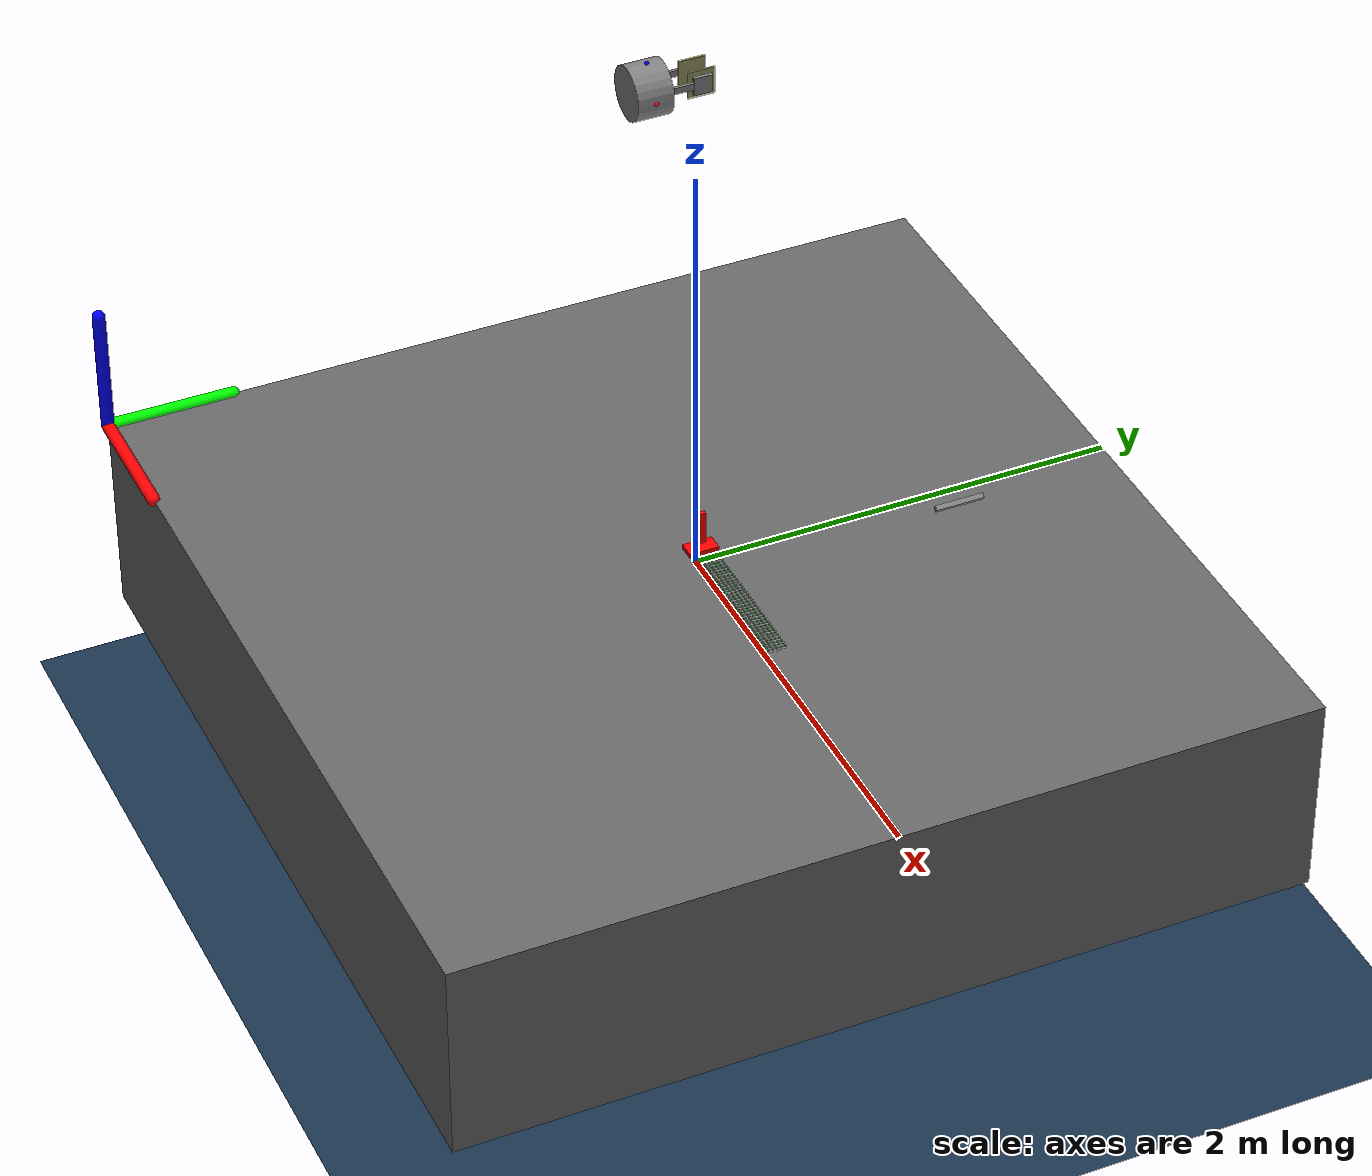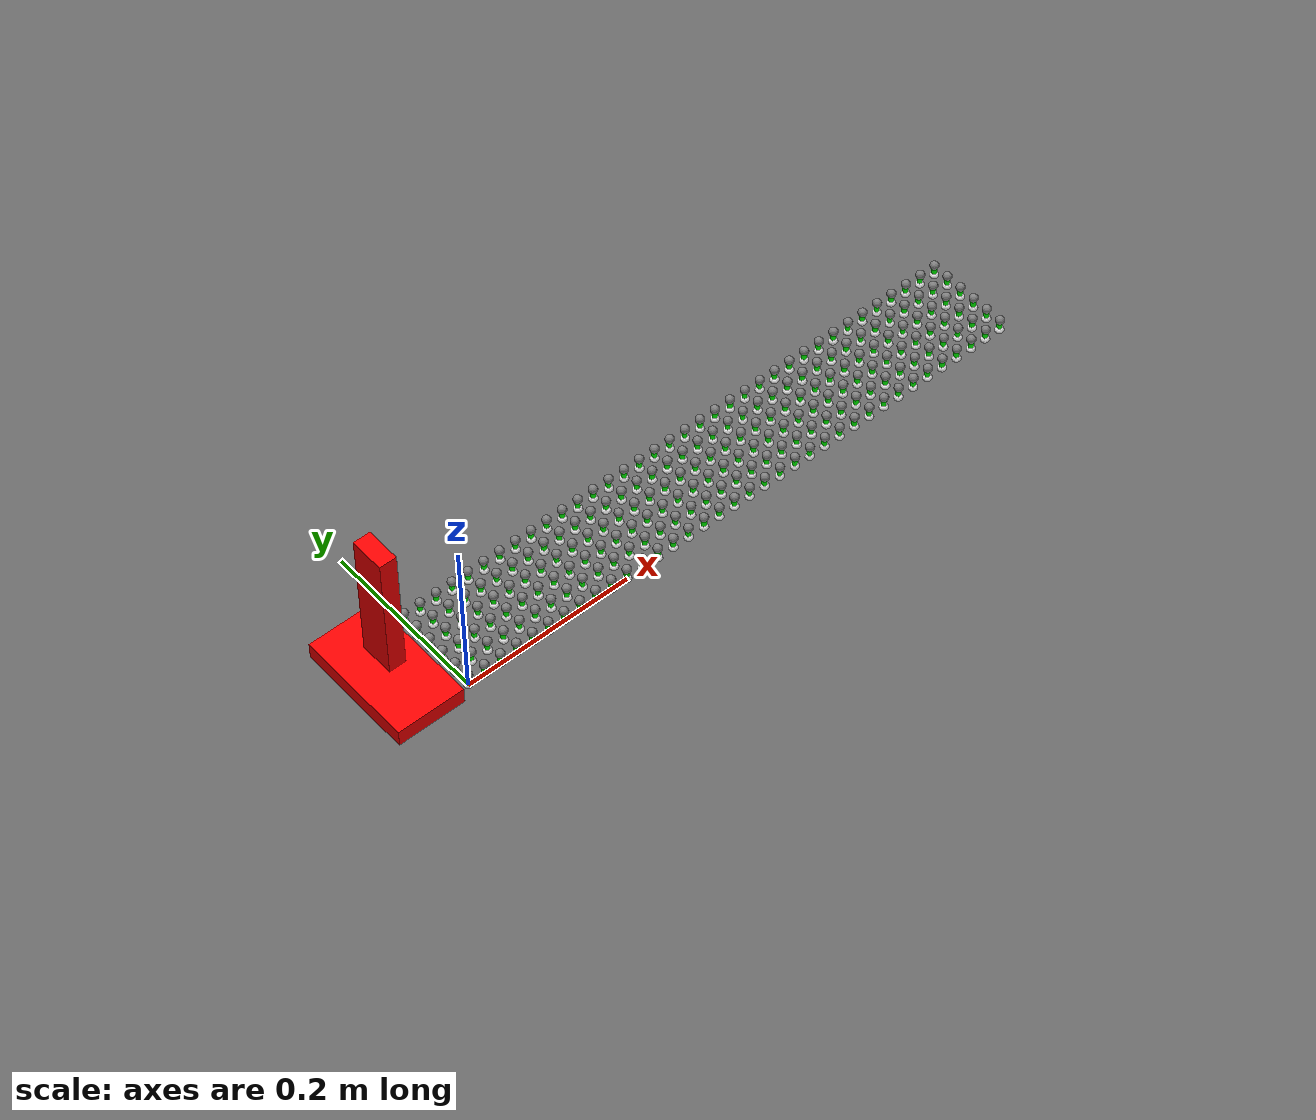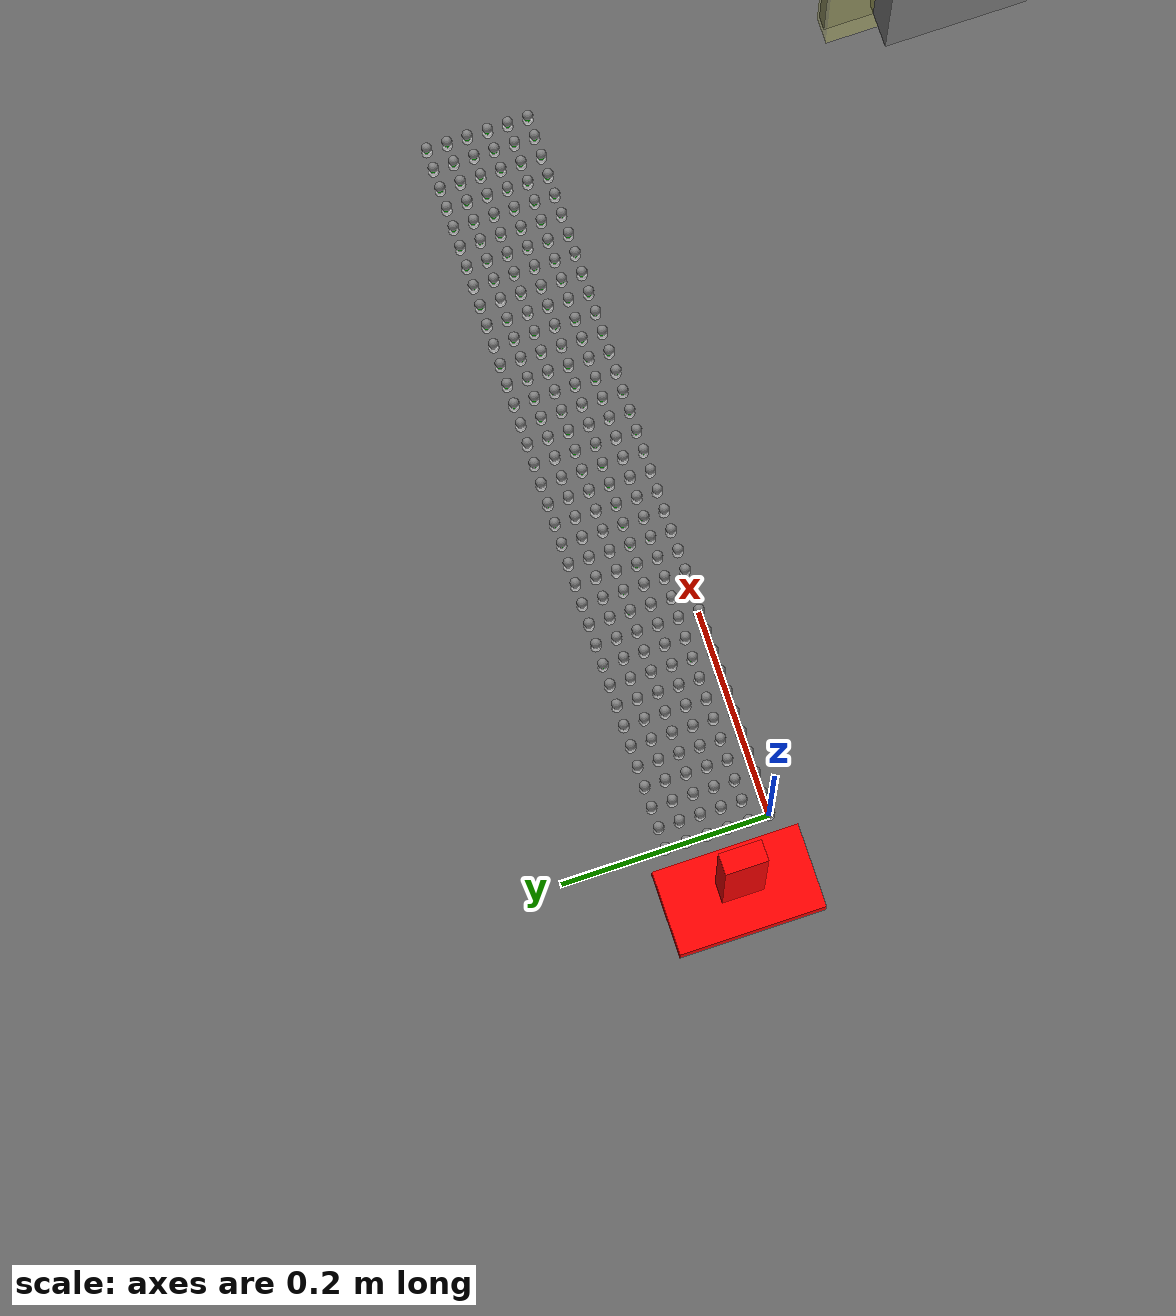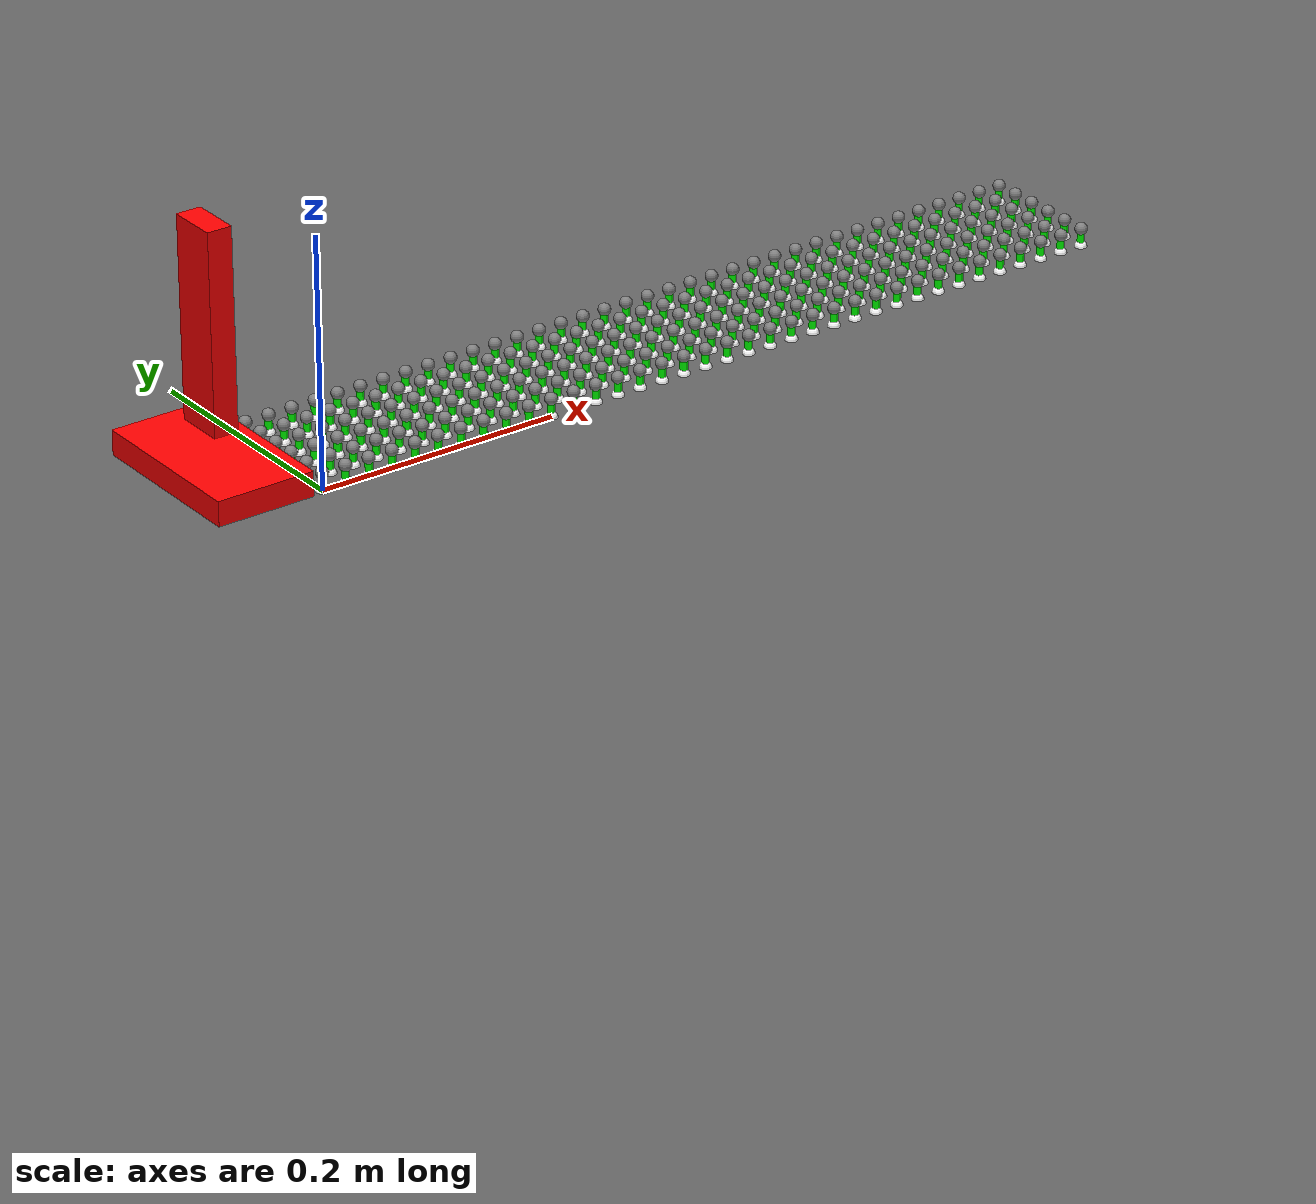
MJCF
<mujoco>
	<compiler angle="radian"
			inertiafromgeom="auto"
			texturedir="textures/"
			meshdir="mesh/visual/"/>
	<option timestep="1e-4"
			iterations="35"
			tolerance="1e-10"
			impratio="20"
			cone="elliptic" />
	<size njmax="10000" nconmax="5000" nstack="15000000"/>

	<default>
		<geom contype='1' conaffinity='1' condim='6' solref="2e-4 1" solimp=".995 .995 .01" friction="1.3 0.01 0.0005" />
		<joint armature="0.01" damping=".1"/>
		<default class="gripperTrans">
			<joint damping='30' />
		</default>
		<default class="gripperRot">
			<joint damping='65'/>
		</default>
		<default class="GRIPPER">
			<joint damping='15'/>
		</default>
	</default>

	<visual>
		<map fogstart="3" fogend="5" znear="0.05"/>
		<quality shadowsize="2048"/>
		<scale  framelength="2.5"
		framewidth="0.06"
		contactwidth="1.1"
		contactheight="0.01"
		forcewidth="0.01"
		/>
	</visual>

	<!--Assets-->
	<asset>
		<!--Textures-->
		<texture name="ur5_tex"     type="2d"       builtin="flat" height="32" width="32" rgb1="0.45 0.45 0.45" />
		<texture name="gripper_tex" type="2d"       builtin="flat" height="32" width="32" rgb1="0.45 0.45 0.45" rgb2="0 0 0"/>
		<texture name="bench_tex"   type="2d"       builtin="flat" height="32" width="32" rgb1="0.7 0.7 0.7" />
		<texture name="sky_tex"     type="skybox"   builtin="gradient" width="100" height="100" rgb1="1 1 1" rgb2="0.3 0.3 0.8" />
		<texture name="texgeom"     type="cube"     builtin="flat" mark="cross" width="127" height="1278" rgb1="0.8 0.6 0.4" rgb2="0.8 0.6 0.4" markrgb="1 1 1" random="0.01" />
		<texture name="floor_tex"   type="2d"        builtin="checker" rgb1=".2 .3 .4" rgb2=".1 .2 .3" width="100" height="100" />
		<texture name="wood"        type="cube"     file="wood2.png"/>
		<texture name="metal"        type="cube"     file="metal2.png"/>
		<!--Materials-->
		<material name="ur5_mat"        texture="ur5_tex"   shininess="0.9" specular="0.75" reflectance="0.3"/>
		<material name="gripper_mat"    texture="gripper_tex"   shininess="0.9" specular="0.75" reflectance="0.4"/>
		<material name='floor_mat'      texture="floor_tex"  shininess="0.8" texrepeat="10 10" specular="0.7"  reflectance="0.5" />
		<material name='geom'           texture="texgeom"   texuniform="true" />
		<material name="bench_mat"      texture="metal"   shininess="0.1" specular="0.5" reflectance="0.2"/>
		<material name="tablecube"      texture="wood" rgba=".8 .8 .8 1"/>
	</asset>

	<worldbody>
		<!--Lighting parameters-->
		<light name="light3" mode="targetbody" target="gripperLink_0" directional="true" pos="1 1 5" />

		<geom type='capsule' size='0.03 0.3' pos='-1.7 -2 0' rgba='1 0 0 1' quat='0.7071068  0 0.7071068 0' />
		<geom type='capsule' size='0.03 0.3' pos='-2 -1.7 0' rgba='0 1 0 1' quat='0.7071068  0.7071068 0 0' />
		<geom type='capsule' size='0.03 0.3' pos='-2 -2 0.3' rgba='0 0 1 1' />

		<!--Floor Property-->
		<geom name='floor' pos='0 0 -1.5' size='5 5 0.1'  type='plane' rgba='0.1 0.2 0.3 1' />

		<body name='camera' pos='2.4 0 2' euler="0 0.6 0" >
		<geom pos='0 0 0' type='box' size='0.01 0.1 0.01' density='10'  />
		<camera name='c1' fovy="55" pos="0 .01 .01">
		</camera>
		</body>

		<!-- Insert table here! -->
    <body name="table" pos="0 0 0" >
        <body name="handle" pos="-0.06 0.05 0.02" euler="0 0 0" >
            <joint name="handle_x" type="slide" pos="0 0 0" axis="1 0 0" damping="10" />
            <joint name="handle_y" type="slide" pos="0 0 0" axis="0 1 0" damping="10" />
            <joint name="handle_z" type="slide" pos="0 0 0" axis="0 0 1" damping="10" />
            <joint name="handle_rot_x" type="hinge" pos="0 0 0" axis="1 0 0" damping="10" />
            <joint name="handle_rot_y" type="hinge" pos="0 0 0" axis="0 1 0" damping="10" />
            <joint name="handle_rot_z" type="hinge" pos="0 0 0" axis="0 0 1" damping="10" />
            <geom name="handle" material="bench_mat" type="box" size="0.04 0.07 0.01" rgba="1 0 0 1" density="50" />
            <site name='handle_0' type='sphere' size='0.01' pos='0 -0.05 0' rgba='0 1 0 1' />
            <site name='handle_1' type='sphere' size='0.01' pos='0 -0.03 0' rgba='0 1 0 1' />
            <site name='handle_2' type='sphere' size='0.01' pos='0 -0.01 0' rgba='0 1 0 1' />
            <site name='handle_3' type='sphere' size='0.01' pos='0 0.01 0' rgba='0 1 0 1' />
            <site name='handle_4' type='sphere' size='0.01' pos='0 0.03 0' rgba='0 1 0 1' />
            <site name='handle_5' type='sphere' size='0.01' pos='0 0.05 0' rgba='0 1 0 1' />
            <body name="handle2" pos="0 0 0.06" euler="-0.0 0.0 -0.0" >
                <geom name="handle2" material="bench_mat" pos="0 0 0.05" type="box" size="0.01 0.02 0.08" density="50" rgba="1 0 0 1"/>
            </body>
        </body>
        <body name="tabletop" pos="0.0 0.0 -0.49" euler="0 0 0" >
            <geom name="tabletop" size="2 2 0.49" type="box" rgba="0.4 0.4 0.4 1" />
        </body>
        <site name="table_0_0" type="sphere" size="0.005" pos="0.0 0.0 0.0" rgba="1 1 1 1" />
        <site name="table_0_1" type="sphere" size="0.005" pos="0.0 0.02 0.0" rgba="1 1 1 1" />
        <site name="table_0_2" type="sphere" size="0.005" pos="0.0 0.04 0.0" rgba="1 1 1 1" />
        <site name="table_0_3" type="sphere" size="0.005" pos="0.0 0.06 0.0" rgba="1 1 1 1" />
        <site name="table_0_4" type="sphere" size="0.005" pos="0.0 0.08 0.0" rgba="1 1 1 1" />
        <site name="table_0_5" type="sphere" size="0.005" pos="0.0 0.1 0.0" rgba="1 1 1 1" />
        <site name="table_1_0" type="sphere" size="0.005" pos="0.02 0.0 0.0" rgba="1 1 1 1" />
        <site name="table_1_1" type="sphere" size="0.005" pos="0.02 0.02 0.0" rgba="1 1 1 1" />
        <site name="table_1_2" type="sphere" size="0.005" pos="0.02 0.04 0.0" rgba="1 1 1 1" />
        <site name="table_1_3" type="sphere" size="0.005" pos="0.02 0.06 0.0" rgba="1 1 1 1" />
        <site name="table_1_4" type="sphere" size="0.005" pos="0.02 0.08 0.0" rgba="1 1 1 1" />
        <site name="table_1_5" type="sphere" size="0.005" pos="0.02 0.1 0.0" rgba="1 1 1 1" />
        <site name="table_2_0" type="sphere" size="0.005" pos="0.04 0.0 0.0" rgba="1 1 1 1" />
        <site name="table_2_1" type="sphere" size="0.005" pos="0.04 0.02 0.0" rgba="1 1 1 1" />
        <site name="table_2_2" type="sphere" size="0.005" pos="0.04 0.04 0.0" rgba="1 1 1 1" />
        <site name="table_2_3" type="sphere" size="0.005" pos="0.04 0.06 0.0" rgba="1 1 1 1" />
        <site name="table_2_4" type="sphere" size="0.005" pos="0.04 0.08 0.0" rgba="1 1 1 1" />
        <site name="table_2_5" type="sphere" size="0.005" pos="0.04 0.1 0.0" rgba="1 1 1 1" />
        <site name="table_3_0" type="sphere" size="0.005" pos="0.06 0.0 0.0" rgba="1 1 1 1" />
        <site name="table_3_1" type="sphere" size="0.005" pos="0.06 0.02 0.0" rgba="1 1 1 1" />
        <site name="table_3_2" type="sphere" size="0.005" pos="0.06 0.04 0.0" rgba="1 1 1 1" />
        <site name="table_3_3" type="sphere" size="0.005" pos="0.06 0.06 0.0" rgba="1 1 1 1" />
        <site name="table_3_4" type="sphere" size="0.005" pos="0.06 0.08 0.0" rgba="1 1 1 1" />
        <site name="table_3_5" type="sphere" size="0.005" pos="0.06 0.1 0.0" rgba="1 1 1 1" />
        <site name="table_4_0" type="sphere" size="0.005" pos="0.08 0.0 0.0" rgba="1 1 1 1" />
        <site name="table_4_1" type="sphere" size="0.005" pos="0.08 0.02 0.0" rgba="1 1 1 1" />
        <site name="table_4_2" type="sphere" size="0.005" pos="0.08 0.04 0.0" rgba="1 1 1 1" />
        <site name="table_4_3" type="sphere" size="0.005" pos="0.08 0.06 0.0" rgba="1 1 1 1" />
        <site name="table_4_4" type="sphere" size="0.005" pos="0.08 0.08 0.0" rgba="1 1 1 1" />
        <site name="table_4_5" type="sphere" size="0.005" pos="0.08 0.1 0.0" rgba="1 1 1 1" />
        <site name="table_5_0" type="sphere" size="0.005" pos="0.1 0.0 0.0" rgba="1 1 1 1" />
        <site name="table_5_1" type="sphere" size="0.005" pos="0.1 0.02 0.0" rgba="1 1 1 1" />
        <site name="table_5_2" type="sphere" size="0.005" pos="0.1 0.04 0.0" rgba="1 1 1 1" />
        <site name="table_5_3" type="sphere" size="0.005" pos="0.1 0.06 0.0" rgba="1 1 1 1" />
        <site name="table_5_4" type="sphere" size="0.005" pos="0.1 0.08 0.0" rgba="1 1 1 1" />
        <site name="table_5_5" type="sphere" size="0.005" pos="0.1 0.1 0.0" rgba="1 1 1 1" />
        <site name="table_6_0" type="sphere" size="0.005" pos="0.12 0.0 0.0" rgba="1 1 1 1" />
        <site name="table_6_1" type="sphere" size="0.005" pos="0.12 0.02 0.0" rgba="1 1 1 1" />
        <site name="table_6_2" type="sphere" size="0.005" pos="0.12 0.04 0.0" rgba="1 1 1 1" />
        <site name="table_6_3" type="sphere" size="0.005" pos="0.12 0.06 0.0" rgba="1 1 1 1" />
        <site name="table_6_4" type="sphere" size="0.005" pos="0.12 0.08 0.0" rgba="1 1 1 1" />
        <site name="table_6_5" type="sphere" size="0.005" pos="0.12 0.1 0.0" rgba="1 1 1 1" />
        <site name="table_7_0" type="sphere" size="0.005" pos="0.14 0.0 0.0" rgba="1 1 1 1" />
        <site name="table_7_1" type="sphere" size="0.005" pos="0.14 0.02 0.0" rgba="1 1 1 1" />
        <site name="table_7_2" type="sphere" size="0.005" pos="0.14 0.04 0.0" rgba="1 1 1 1" />
        <site name="table_7_3" type="sphere" size="0.005" pos="0.14 0.06 0.0" rgba="1 1 1 1" />
        <site name="table_7_4" type="sphere" size="0.005" pos="0.14 0.08 0.0" rgba="1 1 1 1" />
        <site name="table_7_5" type="sphere" size="0.005" pos="0.14 0.1 0.0" rgba="1 1 1 1" />
        <site name="table_8_0" type="sphere" size="0.005" pos="0.16 0.0 0.0" rgba="1 1 1 1" />
        <site name="table_8_1" type="sphere" size="0.005" pos="0.16 0.02 0.0" rgba="1 1 1 1" />
        <site name="table_8_2" type="sphere" size="0.005" pos="0.16 0.04 0.0" rgba="1 1 1 1" />
        <site name="table_8_3" type="sphere" size="0.005" pos="0.16 0.06 0.0" rgba="1 1 1 1" />
        <site name="table_8_4" type="sphere" size="0.005" pos="0.16 0.08 0.0" rgba="1 1 1 1" />
        <site name="table_8_5" type="sphere" size="0.005" pos="0.16 0.1 0.0" rgba="1 1 1 1" />
        <site name="table_9_0" type="sphere" size="0.005" pos="0.18 0.0 0.0" rgba="1 1 1 1" />
        <site name="table_9_1" type="sphere" size="0.005" pos="0.18 0.02 0.0" rgba="1 1 1 1" />
        <site name="table_9_2" type="sphere" size="0.005" pos="0.18 0.04 0.0" rgba="1 1 1 1" />
        <site name="table_9_3" type="sphere" size="0.005" pos="0.18 0.06 0.0" rgba="1 1 1 1" />
        <site name="table_9_4" type="sphere" size="0.005" pos="0.18 0.08 0.0" rgba="1 1 1 1" />
        <site name="table_9_5" type="sphere" size="0.005" pos="0.18 0.1 0.0" rgba="1 1 1 1" />
        <site name="table_10_0" type="sphere" size="0.005" pos="0.2 0.0 0.0" rgba="1 1 1 1" />
        <site name="table_10_1" type="sphere" size="0.005" pos="0.2 0.02 0.0" rgba="1 1 1 1" />
        <site name="table_10_2" type="sphere" size="0.005" pos="0.2 0.04 0.0" rgba="1 1 1 1" />
        <site name="table_10_3" type="sphere" size="0.005" pos="0.2 0.06 0.0" rgba="1 1 1 1" />
        <site name="table_10_4" type="sphere" size="0.005" pos="0.2 0.08 0.0" rgba="1 1 1 1" />
        <site name="table_10_5" type="sphere" size="0.005" pos="0.2 0.1 0.0" rgba="1 1 1 1" />
        <site name="table_11_0" type="sphere" size="0.005" pos="0.22 0.0 0.0" rgba="1 1 1 1" />
        <site name="table_11_1" type="sphere" size="0.005" pos="0.22 0.02 0.0" rgba="1 1 1 1" />
        <site name="table_11_2" type="sphere" size="0.005" pos="0.22 0.04 0.0" rgba="1 1 1 1" />
        <site name="table_11_3" type="sphere" size="0.005" pos="0.22 0.06 0.0" rgba="1 1 1 1" />
        <site name="table_11_4" type="sphere" size="0.005" pos="0.22 0.08 0.0" rgba="1 1 1 1" />
        <site name="table_11_5" type="sphere" size="0.005" pos="0.22 0.1 0.0" rgba="1 1 1 1" />
        <site name="table_12_0" type="sphere" size="0.005" pos="0.24 0.0 0.0" rgba="1 1 1 1" />
        <site name="table_12_1" type="sphere" size="0.005" pos="0.24 0.02 0.0" rgba="1 1 1 1" />
        <site name="table_12_2" type="sphere" size="0.005" pos="0.24 0.04 0.0" rgba="1 1 1 1" />
        <site name="table_12_3" type="sphere" size="0.005" pos="0.24 0.06 0.0" rgba="1 1 1 1" />
        <site name="table_12_4" type="sphere" size="0.005" pos="0.24 0.08 0.0" rgba="1 1 1 1" />
        <site name="table_12_5" type="sphere" size="0.005" pos="0.24 0.1 0.0" rgba="1 1 1 1" />
        <site name="table_13_0" type="sphere" size="0.005" pos="0.26 0.0 0.0" rgba="1 1 1 1" />
        <site name="table_13_1" type="sphere" size="0.005" pos="0.26 0.02 0.0" rgba="1 1 1 1" />
        <site name="table_13_2" type="sphere" size="0.005" pos="0.26 0.04 0.0" rgba="1 1 1 1" />
        <site name="table_13_3" type="sphere" size="0.005" pos="0.26 0.06 0.0" rgba="1 1 1 1" />
        <site name="table_13_4" type="sphere" size="0.005" pos="0.26 0.08 0.0" rgba="1 1 1 1" />
        <site name="table_13_5" type="sphere" size="0.005" pos="0.26 0.1 0.0" rgba="1 1 1 1" />
        <site name="table_14_0" type="sphere" size="0.005" pos="0.28 0.0 0.0" rgba="1 1 1 1" />
        <site name="table_14_1" type="sphere" size="0.005" pos="0.28 0.02 0.0" rgba="1 1 1 1" />
        <site name="table_14_2" type="sphere" size="0.005" pos="0.28 0.04 0.0" rgba="1 1 1 1" />
        <site name="table_14_3" type="sphere" size="0.005" pos="0.28 0.06 0.0" rgba="1 1 1 1" />
        <site name="table_14_4" type="sphere" size="0.005" pos="0.28 0.08 0.0" rgba="1 1 1 1" />
        <site name="table_14_5" type="sphere" size="0.005" pos="0.28 0.1 0.0" rgba="1 1 1 1" />
        <site name="table_15_0" type="sphere" size="0.005" pos="0.3 0.0 0.0" rgba="1 1 1 1" />
        <site name="table_15_1" type="sphere" size="0.005" pos="0.3 0.02 0.0" rgba="1 1 1 1" />
        <site name="table_15_2" type="sphere" size="0.005" pos="0.3 0.04 0.0" rgba="1 1 1 1" />
        <site name="table_15_3" type="sphere" size="0.005" pos="0.3 0.06 0.0" rgba="1 1 1 1" />
        <site name="table_15_4" type="sphere" size="0.005" pos="0.3 0.08 0.0" rgba="1 1 1 1" />
        <site name="table_15_5" type="sphere" size="0.005" pos="0.3 0.1 0.0" rgba="1 1 1 1" />
        <site name="table_16_0" type="sphere" size="0.005" pos="0.32 0.0 0.0" rgba="1 1 1 1" />
        <site name="table_16_1" type="sphere" size="0.005" pos="0.32 0.02 0.0" rgba="1 1 1 1" />
        <site name="table_16_2" type="sphere" size="0.005" pos="0.32 0.04 0.0" rgba="1 1 1 1" />
        <site name="table_16_3" type="sphere" size="0.005" pos="0.32 0.06 0.0" rgba="1 1 1 1" />
        <site name="table_16_4" type="sphere" size="0.005" pos="0.32 0.08 0.0" rgba="1 1 1 1" />
        <site name="table_16_5" type="sphere" size="0.005" pos="0.32 0.1 0.0" rgba="1 1 1 1" />
        <site name="table_17_0" type="sphere" size="0.005" pos="0.34 0.0 0.0" rgba="1 1 1 1" />
        <site name="table_17_1" type="sphere" size="0.005" pos="0.34 0.02 0.0" rgba="1 1 1 1" />
        <site name="table_17_2" type="sphere" size="0.005" pos="0.34 0.04 0.0" rgba="1 1 1 1" />
        <site name="table_17_3" type="sphere" size="0.005" pos="0.34 0.06 0.0" rgba="1 1 1 1" />
        <site name="table_17_4" type="sphere" size="0.005" pos="0.34 0.08 0.0" rgba="1 1 1 1" />
        <site name="table_17_5" type="sphere" size="0.005" pos="0.34 0.1 0.0" rgba="1 1 1 1" />
        <site name="table_18_0" type="sphere" size="0.005" pos="0.36 0.0 0.0" rgba="1 1 1 1" />
        <site name="table_18_1" type="sphere" size="0.005" pos="0.36 0.02 0.0" rgba="1 1 1 1" />
        <site name="table_18_2" type="sphere" size="0.005" pos="0.36 0.04 0.0" rgba="1 1 1 1" />
        <site name="table_18_3" type="sphere" size="0.005" pos="0.36 0.06 0.0" rgba="1 1 1 1" />
        <site name="table_18_4" type="sphere" size="0.005" pos="0.36 0.08 0.0" rgba="1 1 1 1" />
        <site name="table_18_5" type="sphere" size="0.005" pos="0.36 0.1 0.0" rgba="1 1 1 1" />
        <site name="table_19_0" type="sphere" size="0.005" pos="0.38 0.0 0.0" rgba="1 1 1 1" />
        <site name="table_19_1" type="sphere" size="0.005" pos="0.38 0.02 0.0" rgba="1 1 1 1" />
        <site name="table_19_2" type="sphere" size="0.005" pos="0.38 0.04 0.0" rgba="1 1 1 1" />
        <site name="table_19_3" type="sphere" size="0.005" pos="0.38 0.06 0.0" rgba="1 1 1 1" />
        <site name="table_19_4" type="sphere" size="0.005" pos="0.38 0.08 0.0" rgba="1 1 1 1" />
        <site name="table_19_5" type="sphere" size="0.005" pos="0.38 0.1 0.0" rgba="1 1 1 1" />
        <site name="table_20_0" type="sphere" size="0.005" pos="0.4 0.0 0.0" rgba="1 1 1 1" />
        <site name="table_20_1" type="sphere" size="0.005" pos="0.4 0.02 0.0" rgba="1 1 1 1" />
        <site name="table_20_2" type="sphere" size="0.005" pos="0.4 0.04 0.0" rgba="1 1 1 1" />
        <site name="table_20_3" type="sphere" size="0.005" pos="0.4 0.06 0.0" rgba="1 1 1 1" />
        <site name="table_20_4" type="sphere" size="0.005" pos="0.4 0.08 0.0" rgba="1 1 1 1" />
        <site name="table_20_5" type="sphere" size="0.005" pos="0.4 0.1 0.0" rgba="1 1 1 1" />
        <site name="table_21_0" type="sphere" size="0.005" pos="0.42 0.0 0.0" rgba="1 1 1 1" />
        <site name="table_21_1" type="sphere" size="0.005" pos="0.42 0.02 0.0" rgba="1 1 1 1" />
        <site name="table_21_2" type="sphere" size="0.005" pos="0.42 0.04 0.0" rgba="1 1 1 1" />
        <site name="table_21_3" type="sphere" size="0.005" pos="0.42 0.06 0.0" rgba="1 1 1 1" />
        <site name="table_21_4" type="sphere" size="0.005" pos="0.42 0.08 0.0" rgba="1 1 1 1" />
        <site name="table_21_5" type="sphere" size="0.005" pos="0.42 0.1 0.0" rgba="1 1 1 1" />
        <site name="table_22_0" type="sphere" size="0.005" pos="0.44 0.0 0.0" rgba="1 1 1 1" />
        <site name="table_22_1" type="sphere" size="0.005" pos="0.44 0.02 0.0" rgba="1 1 1 1" />
        <site name="table_22_2" type="sphere" size="0.005" pos="0.44 0.04 0.0" rgba="1 1 1 1" />
        <site name="table_22_3" type="sphere" size="0.005" pos="0.44 0.06 0.0" rgba="1 1 1 1" />
        <site name="table_22_4" type="sphere" size="0.005" pos="0.44 0.08 0.0" rgba="1 1 1 1" />
        <site name="table_22_5" type="sphere" size="0.005" pos="0.44 0.1 0.0" rgba="1 1 1 1" />
        <site name="table_23_0" type="sphere" size="0.005" pos="0.46 0.0 0.0" rgba="1 1 1 1" />
        <site name="table_23_1" type="sphere" size="0.005" pos="0.46 0.02 0.0" rgba="1 1 1 1" />
        <site name="table_23_2" type="sphere" size="0.005" pos="0.46 0.04 0.0" rgba="1 1 1 1" />
        <site name="table_23_3" type="sphere" size="0.005" pos="0.46 0.06 0.0" rgba="1 1 1 1" />
        <site name="table_23_4" type="sphere" size="0.005" pos="0.46 0.08 0.0" rgba="1 1 1 1" />
        <site name="table_23_5" type="sphere" size="0.005" pos="0.46 0.1 0.0" rgba="1 1 1 1" />
        <site name="table_24_0" type="sphere" size="0.005" pos="0.48 0.0 0.0" rgba="1 1 1 1" />
        <site name="table_24_1" type="sphere" size="0.005" pos="0.48 0.02 0.0" rgba="1 1 1 1" />
        <site name="table_24_2" type="sphere" size="0.005" pos="0.48 0.04 0.0" rgba="1 1 1 1" />
        <site name="table_24_3" type="sphere" size="0.005" pos="0.48 0.06 0.0" rgba="1 1 1 1" />
        <site name="table_24_4" type="sphere" size="0.005" pos="0.48 0.08 0.0" rgba="1 1 1 1" />
        <site name="table_24_5" type="sphere" size="0.005" pos="0.48 0.1 0.0" rgba="1 1 1 1" />
        <site name="table_25_0" type="sphere" size="0.005" pos="0.5 0.0 0.0" rgba="1 1 1 1" />
        <site name="table_25_1" type="sphere" size="0.005" pos="0.5 0.02 0.0" rgba="1 1 1 1" />
        <site name="table_25_2" type="sphere" size="0.005" pos="0.5 0.04 0.0" rgba="1 1 1 1" />
        <site name="table_25_3" type="sphere" size="0.005" pos="0.5 0.06 0.0" rgba="1 1 1 1" />
        <site name="table_25_4" type="sphere" size="0.005" pos="0.5 0.08 0.0" rgba="1 1 1 1" />
        <site name="table_25_5" type="sphere" size="0.005" pos="0.5 0.1 0.0" rgba="1 1 1 1" />
        <site name="table_26_0" type="sphere" size="0.005" pos="0.52 0.0 0.0" rgba="1 1 1 1" />
        <site name="table_26_1" type="sphere" size="0.005" pos="0.52 0.02 0.0" rgba="1 1 1 1" />
        <site name="table_26_2" type="sphere" size="0.005" pos="0.52 0.04 0.0" rgba="1 1 1 1" />
        <site name="table_26_3" type="sphere" size="0.005" pos="0.52 0.06 0.0" rgba="1 1 1 1" />
        <site name="table_26_4" type="sphere" size="0.005" pos="0.52 0.08 0.0" rgba="1 1 1 1" />
        <site name="table_26_5" type="sphere" size="0.005" pos="0.52 0.1 0.0" rgba="1 1 1 1" />
        <site name="table_27_0" type="sphere" size="0.005" pos="0.54 0.0 0.0" rgba="1 1 1 1" />
        <site name="table_27_1" type="sphere" size="0.005" pos="0.54 0.02 0.0" rgba="1 1 1 1" />
        <site name="table_27_2" type="sphere" size="0.005" pos="0.54 0.04 0.0" rgba="1 1 1 1" />
        <site name="table_27_3" type="sphere" size="0.005" pos="0.54 0.06 0.0" rgba="1 1 1 1" />
        <site name="table_27_4" type="sphere" size="0.005" pos="0.54 0.08 0.0" rgba="1 1 1 1" />
        <site name="table_27_5" type="sphere" size="0.005" pos="0.54 0.1 0.0" rgba="1 1 1 1" />
        <site name="table_28_0" type="sphere" size="0.005" pos="0.56 0.0 0.0" rgba="1 1 1 1" />
        <site name="table_28_1" type="sphere" size="0.005" pos="0.56 0.02 0.0" rgba="1 1 1 1" />
        <site name="table_28_2" type="sphere" size="0.005" pos="0.56 0.04 0.0" rgba="1 1 1 1" />
        <site name="table_28_3" type="sphere" size="0.005" pos="0.56 0.06 0.0" rgba="1 1 1 1" />
        <site name="table_28_4" type="sphere" size="0.005" pos="0.56 0.08 0.0" rgba="1 1 1 1" />
        <site name="table_28_5" type="sphere" size="0.005" pos="0.56 0.1 0.0" rgba="1 1 1 1" />
        <site name="table_29_0" type="sphere" size="0.005" pos="0.58 0.0 0.0" rgba="1 1 1 1" />
        <site name="table_29_1" type="sphere" size="0.005" pos="0.58 0.02 0.0" rgba="1 1 1 1" />
        <site name="table_29_2" type="sphere" size="0.005" pos="0.58 0.04 0.0" rgba="1 1 1 1" />
        <site name="table_29_3" type="sphere" size="0.005" pos="0.58 0.06 0.0" rgba="1 1 1 1" />
        <site name="table_29_4" type="sphere" size="0.005" pos="0.58 0.08 0.0" rgba="1 1 1 1" />
        <site name="table_29_5" type="sphere" size="0.005" pos="0.58 0.1 0.0" rgba="1 1 1 1" />
        <site name="table_30_0" type="sphere" size="0.005" pos="0.6 0.0 0.0" rgba="1 1 1 1" />
        <site name="table_30_1" type="sphere" size="0.005" pos="0.6 0.02 0.0" rgba="1 1 1 1" />
        <site name="table_30_2" type="sphere" size="0.005" pos="0.6 0.04 0.0" rgba="1 1 1 1" />
        <site name="table_30_3" type="sphere" size="0.005" pos="0.6 0.06 0.0" rgba="1 1 1 1" />
        <site name="table_30_4" type="sphere" size="0.005" pos="0.6 0.08 0.0" rgba="1 1 1 1" />
        <site name="table_30_5" type="sphere" size="0.005" pos="0.6 0.1 0.0" rgba="1 1 1 1" />
        <site name="table_31_0" type="sphere" size="0.005" pos="0.62 0.0 0.0" rgba="1 1 1 1" />
        <site name="table_31_1" type="sphere" size="0.005" pos="0.62 0.02 0.0" rgba="1 1 1 1" />
        <site name="table_31_2" type="sphere" size="0.005" pos="0.62 0.04 0.0" rgba="1 1 1 1" />
        <site name="table_31_3" type="sphere" size="0.005" pos="0.62 0.06 0.0" rgba="1 1 1 1" />
        <site name="table_31_4" type="sphere" size="0.005" pos="0.62 0.08 0.0" rgba="1 1 1 1" />
        <site name="table_31_5" type="sphere" size="0.005" pos="0.62 0.1 0.0" rgba="1 1 1 1" />
        <site name="table_32_0" type="sphere" size="0.005" pos="0.64 0.0 0.0" rgba="1 1 1 1" />
        <site name="table_32_1" type="sphere" size="0.005" pos="0.64 0.02 0.0" rgba="1 1 1 1" />
        <site name="table_32_2" type="sphere" size="0.005" pos="0.64 0.04 0.0" rgba="1 1 1 1" />
        <site name="table_32_3" type="sphere" size="0.005" pos="0.64 0.06 0.0" rgba="1 1 1 1" />
        <site name="table_32_4" type="sphere" size="0.005" pos="0.64 0.08 0.0" rgba="1 1 1 1" />
        <site name="table_32_5" type="sphere" size="0.005" pos="0.64 0.1 0.0" rgba="1 1 1 1" />
        <site name="table_33_0" type="sphere" size="0.005" pos="0.66 0.0 0.0" rgba="1 1 1 1" />
        <site name="table_33_1" type="sphere" size="0.005" pos="0.66 0.02 0.0" rgba="1 1 1 1" />
        <site name="table_33_2" type="sphere" size="0.005" pos="0.66 0.04 0.0" rgba="1 1 1 1" />
        <site name="table_33_3" type="sphere" size="0.005" pos="0.66 0.06 0.0" rgba="1 1 1 1" />
        <site name="table_33_4" type="sphere" size="0.005" pos="0.66 0.08 0.0" rgba="1 1 1 1" />
        <site name="table_33_5" type="sphere" size="0.005" pos="0.66 0.1 0.0" rgba="1 1 1 1" />
        <site name="table_34_0" type="sphere" size="0.005" pos="0.68 0.0 0.0" rgba="1 1 1 1" />
        <site name="table_34_1" type="sphere" size="0.005" pos="0.68 0.02 0.0" rgba="1 1 1 1" />
        <site name="table_34_2" type="sphere" size="0.005" pos="0.68 0.04 0.0" rgba="1 1 1 1" />
        <site name="table_34_3" type="sphere" size="0.005" pos="0.68 0.06 0.0" rgba="1 1 1 1" />
        <site name="table_34_4" type="sphere" size="0.005" pos="0.68 0.08 0.0" rgba="1 1 1 1" />
        <site name="table_34_5" type="sphere" size="0.005" pos="0.68 0.1 0.0" rgba="1 1 1 1" />
        <site name="table_35_0" type="sphere" size="0.005" pos="0.7000000000000001 0.0 0.0" rgba="1 1 1 1" />
        <site name="table_35_1" type="sphere" size="0.005" pos="0.7000000000000001 0.02 0.0" rgba="1 1 1 1" />
        <site name="table_35_2" type="sphere" size="0.005" pos="0.7000000000000001 0.04 0.0" rgba="1 1 1 1" />
        <site name="table_35_3" type="sphere" size="0.005" pos="0.7000000000000001 0.06 0.0" rgba="1 1 1 1" />
        <site name="table_35_4" type="sphere" size="0.005" pos="0.7000000000000001 0.08 0.0" rgba="1 1 1 1" />
        <site name="table_35_5" type="sphere" size="0.005" pos="0.7000000000000001 0.1 0.0" rgba="1 1 1 1" />
    </body>

		<!-- GRIPPER -->
		<body name="gripperLink_0" pos="0 0 2.5" >
			<joint name="trans_x" type="slide" class="gripperTrans" pos="0 0 0" axis="1 0 0" />
			<joint name="trans_y" type="slide" class="gripperTrans" pos="0 0 0" axis="0 1 0" />
			<joint name="trans_z" type="slide" class="gripperTrans" pos="0 0 0" axis="0 0 1" />
			<joint name="rot_x" class="gripperRot" pos="0 0 0" axis="1 0 0" />
			<joint name="rot_y" class="gripperRot" pos="0 0 0" axis="0 1 0" />
			<joint name="rot_z" class="gripperRot" pos="0 0 0" axis="0 0 1" />

			<geom pos='0 -0.23 0' type='cylinder' size='0.12 0.08' quat='0.7071068 0.7071068 0 0' condim='3' density='10' />
			<geom pos='0.12 -0.23 0' type='sphere' size='0.01' rgba='1 0 0 1' density='1' />
			<geom pos='0 -0.22 0.12' type='sphere' size='0.01' rgba='0 0 1 1' density='1' />

			<body name='left_finger' pos='-0.06 -0.14 0' quat='1 0 0 0'>
				<joint name='l_f' type='slide' pos='0 0 0' axis='1 0 0' range='0 0.05' damping='10' limited='true' solreflimit='1e-3 1' solimplimit=".99 .99 .01" />
				<geom pos='0 0.05 0' type='box' size='0.007 0.05 0.015' condim='6' friction='1 0.02 0.0005' density='10'  />
				<!-- Fingertip -->
				<body name='left_fingertip' pos='0 0.14 0' quat='0.7071068 0 0.7071068 0'>
					<geom pos='0 0 0' type='box' size='0.04 0.04 0.01' condim='6'  friction='1 0.04 0.001' solref='1e-4 1' density='2000'  />
					<!-- Four anchor points for cross tendons, in order to implement shear force sensor -->
					<site name="left_cross_bottom_1" pos="0.04  0 0.01" type='sphere' size='0.003' />
					<site name="left_cross_bottom_2" pos="-0.04 0 0.01" type='sphere' size='0.003' />
					<site name="left_cross_bottom_3" pos="0  0.04 0.01" type='sphere' size='0.003' />
					<site name="left_cross_bottom_4" pos="0 -0.04 0.01" type='sphere' size='0.003' />
					<body name='left_finger_skin' pos='0 0 0.015' >
						<geom pos='0 0 0' name='left_tip' type='box' size='0.06 0.06 0.003'  solref='1e-4 1'  />
						<site pos='0 0 -0.003' type='box' size='0.061 0.061 0.006' name='leftFingerMainTouch' rgba='1 1 0 0.2' />
					</body>
				</body>
			</body>

			<body name='right_finger' pos='0.06 -0.14 0' quat='1 0 0 0'>
				<joint name='r_f' type='slide' pos='0 0 0' axis='-1 0 0' range='0 0.05' damping='10' limited='true'  solreflimit='1e-3 1' solimplimit=".99 .99 .01" />
				<geom pos='0 0.05 0' type='box' size='0.007 0.05 0.015' condim='6' friction='1 0.02 0.0005' density='10'  />
				<!-- Fingertip -->
				<body name='right_fingertip' pos='0 0.14 0' quat='-0.7071068 0 0.7071068 0'>
					<geom pos='0 0 0' type='box' size='0.04 0.04 0.01' condim='6'  friction='1 0.04 0.001' solref='1e-4 1' density='2000'  />
					<!-- Four anchor points for cross tendons, in order to implement shear force sensor -->
					<site name="right_cross_bottom_1" pos="0.04  0 0.01" type='sphere' size='0.003' />
					<site name="right_cross_bottom_2" pos="-0.04 0 0.01" type='sphere' size='0.003' />
					<site name="right_cross_bottom_3" pos="0  0.04 0.01" type='sphere' size='0.003' />
					<site name="right_cross_bottom_4" pos="0 -0.04 0.01" type='sphere' size='0.003' />
					<body name='right_finger_skin' pos='0 0 0.015' >
						<geom pos='0 0 0' name='right_tip' type='box' size='0.06 0.06 0.003'  solref='1e-4 1' />
						<site pos='0 0 -0.003' type='box' size='0.061 0.061 0.006' name='rightFingerMainTouch' rgba='1 1 0 0.2' />
					</body>
				</body>
			</body>
		</body>

	<!-- Insert velcro here! -->
        <body name="comp_0_0" pos="0.0 0.0 0.015" >
            <joint type="free" name="comp_0_0" />
            <geom type="sphere" size="0.001" density="50" rgba="1 1 1 1" />
            <site name="comp_0_0_0" type="sphere" size="0.005" />
        </body>
        <body name="comp_0_1" pos="0.0 0.02 0.015" >
            <joint type="free" name="comp_0_1" />
            <geom type="sphere" size="0.001" density="50" rgba="1 1 1 1" />
            <site name="comp_0_1_0" type="sphere" size="0.005" />
        </body>
        <body name="comp_0_2" pos="0.0 0.04 0.015" >
            <joint type="free" name="comp_0_2" />
            <geom type="sphere" size="0.001" density="50" rgba="1 1 1 1" />
            <site name="comp_0_2_0" type="sphere" size="0.005" />
        </body>
        <body name="comp_0_3" pos="0.0 0.06 0.015" >
            <joint type="free" name="comp_0_3" />
            <geom type="sphere" size="0.001" density="50" rgba="1 1 1 1" />
            <site name="comp_0_3_0" type="sphere" size="0.005" />
        </body>
        <body name="comp_0_4" pos="0.0 0.08 0.015" >
            <joint type="free" name="comp_0_4" />
            <geom type="sphere" size="0.001" density="50" rgba="1 1 1 1" />
            <site name="comp_0_4_0" type="sphere" size="0.005" />
        </body>
        <body name="comp_0_5" pos="0.0 0.1 0.015" >
            <joint type="free" name="comp_0_5" />
            <geom type="sphere" size="0.001" density="50" rgba="1 1 1 1" />
            <site name="comp_0_5_0" type="sphere" size="0.005" />
        </body>
        <body name="comp_1_0" pos="0.02 0.0 0.015" >
            <joint type="free" name="comp_1_0" />
            <geom type="sphere" size="0.001" density="50" rgba="1 1 1 1" />
            <site name="comp_1_0_0" type="sphere" size="0.005" />
        </body>
        <body name="comp_1_1" pos="0.02 0.02 0.015" >
            <joint type="free" name="comp_1_1" />
            <geom type="sphere" size="0.001" density="50" rgba="1 1 1 1" />
            <site name="comp_1_1_0" type="sphere" size="0.005" />
        </body>
        <body name="comp_1_2" pos="0.02 0.04 0.015" >
            <joint type="free" name="comp_1_2" />
            <geom type="sphere" size="0.001" density="50" rgba="1 1 1 1" />
            <site name="comp_1_2_0" type="sphere" size="0.005" />
        </body>
        <body name="comp_1_3" pos="0.02 0.06 0.015" >
            <joint type="free" name="comp_1_3" />
            <geom type="sphere" size="0.001" density="50" rgba="1 1 1 1" />
            <site name="comp_1_3_0" type="sphere" size="0.005" />
        </body>
        <body name="comp_1_4" pos="0.02 0.08 0.015" >
            <joint type="free" name="comp_1_4" />
            <geom type="sphere" size="0.001" density="50" rgba="1 1 1 1" />
            <site name="comp_1_4_0" type="sphere" size="0.005" />
        </body>
        <body name="comp_1_5" pos="0.02 0.1 0.015" >
            <joint type="free" name="comp_1_5" />
            <geom type="sphere" size="0.001" density="50" rgba="1 1 1 1" />
            <site name="comp_1_5_0" type="sphere" size="0.005" />
        </body>
        <body name="comp_2_0" pos="0.04 0.0 0.015" >
            <joint type="free" name="comp_2_0" />
            <geom type="sphere" size="0.001" density="50" rgba="1 1 1 1" />
            <site name="comp_2_0_0" type="sphere" size="0.005" />
        </body>
        <body name="comp_2_1" pos="0.04 0.02 0.015" >
            <joint type="free" name="comp_2_1" />
            <geom type="sphere" size="0.001" density="50" rgba="1 1 1 1" />
            <site name="comp_2_1_0" type="sphere" size="0.005" />
        </body>
        <body name="comp_2_2" pos="0.04 0.04 0.015" >
            <joint type="free" name="comp_2_2" />
            <geom type="sphere" size="0.001" density="50" rgba="1 1 1 1" />
            <site name="comp_2_2_0" type="sphere" size="0.005" />
        </body>
        <body name="comp_2_3" pos="0.04 0.06 0.015" >
            <joint type="free" name="comp_2_3" />
            <geom type="sphere" size="0.001" density="50" rgba="1 1 1 1" />
            <site name="comp_2_3_0" type="sphere" size="0.005" />
        </body>
        <body name="comp_2_4" pos="0.04 0.08 0.015" >
            <joint type="free" name="comp_2_4" />
            <geom type="sphere" size="0.001" density="50" rgba="1 1 1 1" />
            <site name="comp_2_4_0" type="sphere" size="0.005" />
        </body>
        <body name="comp_2_5" pos="0.04 0.1 0.015" >
            <joint type="free" name="comp_2_5" />
            <geom type="sphere" size="0.001" density="50" rgba="1 1 1 1" />
            <site name="comp_2_5_0" type="sphere" size="0.005" />
        </body>
        <body name="comp_3_0" pos="0.06 0.0 0.015" >
            <joint type="free" name="comp_3_0" />
            <geom type="sphere" size="0.001" density="50" rgba="1 1 1 1" />
            <site name="comp_3_0_0" type="sphere" size="0.005" />
        </body>
        <body name="comp_3_1" pos="0.06 0.02 0.015" >
            <joint type="free" name="comp_3_1" />
            <geom type="sphere" size="0.001" density="50" rgba="1 1 1 1" />
            <site name="comp_3_1_0" type="sphere" size="0.005" />
        </body>
        <body name="comp_3_2" pos="0.06 0.04 0.015" >
            <joint type="free" name="comp_3_2" />
            <geom type="sphere" size="0.001" density="50" rgba="1 1 1 1" />
            <site name="comp_3_2_0" type="sphere" size="0.005" />
        </body>
        <body name="comp_3_3" pos="0.06 0.06 0.015" >
            <joint type="free" name="comp_3_3" />
            <geom type="sphere" size="0.001" density="50" rgba="1 1 1 1" />
            <site name="comp_3_3_0" type="sphere" size="0.005" />
        </body>
        <body name="comp_3_4" pos="0.06 0.08 0.015" >
            <joint type="free" name="comp_3_4" />
            <geom type="sphere" size="0.001" density="50" rgba="1 1 1 1" />
            <site name="comp_3_4_0" type="sphere" size="0.005" />
        </body>
        <body name="comp_3_5" pos="0.06 0.1 0.015" >
            <joint type="free" name="comp_3_5" />
            <geom type="sphere" size="0.001" density="50" rgba="1 1 1 1" />
            <site name="comp_3_5_0" type="sphere" size="0.005" />
        </body>
        <body name="comp_4_0" pos="0.08 0.0 0.015" >
            <joint type="free" name="comp_4_0" />
            <geom type="sphere" size="0.001" density="50" rgba="1 1 1 1" />
            <site name="comp_4_0_0" type="sphere" size="0.005" />
        </body>
        <body name="comp_4_1" pos="0.08 0.02 0.015" >
            <joint type="free" name="comp_4_1" />
            <geom type="sphere" size="0.001" density="50" rgba="1 1 1 1" />
            <site name="comp_4_1_0" type="sphere" size="0.005" />
        </body>
        <body name="comp_4_2" pos="0.08 0.04 0.015" >
            <joint type="free" name="comp_4_2" />
            <geom type="sphere" size="0.001" density="50" rgba="1 1 1 1" />
            <site name="comp_4_2_0" type="sphere" size="0.005" />
        </body>
        <body name="comp_4_3" pos="0.08 0.06 0.015" >
            <joint type="free" name="comp_4_3" />
            <geom type="sphere" size="0.001" density="50" rgba="1 1 1 1" />
            <site name="comp_4_3_0" type="sphere" size="0.005" />
        </body>
        <body name="comp_4_4" pos="0.08 0.08 0.015" >
            <joint type="free" name="comp_4_4" />
            <geom type="sphere" size="0.001" density="50" rgba="1 1 1 1" />
            <site name="comp_4_4_0" type="sphere" size="0.005" />
        </body>
        <body name="comp_4_5" pos="0.08 0.1 0.015" >
            <joint type="free" name="comp_4_5" />
            <geom type="sphere" size="0.001" density="50" rgba="1 1 1 1" />
            <site name="comp_4_5_0" type="sphere" size="0.005" />
        </body>
        <body name="comp_5_0" pos="0.1 0.0 0.015" >
            <joint type="free" name="comp_5_0" />
            <geom type="sphere" size="0.001" density="50" rgba="1 1 1 1" />
            <site name="comp_5_0_0" type="sphere" size="0.005" />
        </body>
        <body name="comp_5_1" pos="0.1 0.02 0.015" >
            <joint type="free" name="comp_5_1" />
            <geom type="sphere" size="0.001" density="50" rgba="1 1 1 1" />
            <site name="comp_5_1_0" type="sphere" size="0.005" />
        </body>
        <body name="comp_5_2" pos="0.1 0.04 0.015" >
            <joint type="free" name="comp_5_2" />
            <geom type="sphere" size="0.001" density="50" rgba="1 1 1 1" />
            <site name="comp_5_2_0" type="sphere" size="0.005" />
        </body>
        <body name="comp_5_3" pos="0.1 0.06 0.015" >
            <joint type="free" name="comp_5_3" />
            <geom type="sphere" size="0.001" density="50" rgba="1 1 1 1" />
            <site name="comp_5_3_0" type="sphere" size="0.005" />
        </body>
        <body name="comp_5_4" pos="0.1 0.08 0.015" >
            <joint type="free" name="comp_5_4" />
            <geom type="sphere" size="0.001" density="50" rgba="1 1 1 1" />
            <site name="comp_5_4_0" type="sphere" size="0.005" />
        </body>
        <body name="comp_5_5" pos="0.1 0.1 0.015" >
            <joint type="free" name="comp_5_5" />
            <geom type="sphere" size="0.001" density="50" rgba="1 1 1 1" />
            <site name="comp_5_5_0" type="sphere" size="0.005" />
        </body>
        <body name="comp_6_0" pos="0.12 0.0 0.015" >
            <joint type="free" name="comp_6_0" />
            <geom type="sphere" size="0.001" density="50" rgba="1 1 1 1" />
            <site name="comp_6_0_0" type="sphere" size="0.005" />
        </body>
        <body name="comp_6_1" pos="0.12 0.02 0.015" >
            <joint type="free" name="comp_6_1" />
            <geom type="sphere" size="0.001" density="50" rgba="1 1 1 1" />
            <site name="comp_6_1_0" type="sphere" size="0.005" />
        </body>
        <body name="comp_6_2" pos="0.12 0.04 0.015" >
            <joint type="free" name="comp_6_2" />
            <geom type="sphere" size="0.001" density="50" rgba="1 1 1 1" />
            <site name="comp_6_2_0" type="sphere" size="0.005" />
        </body>
        <body name="comp_6_3" pos="0.12 0.06 0.015" >
            <joint type="free" name="comp_6_3" />
            <geom type="sphere" size="0.001" density="50" rgba="1 1 1 1" />
            <site name="comp_6_3_0" type="sphere" size="0.005" />
        </body>
        <body name="comp_6_4" pos="0.12 0.08 0.015" >
            <joint type="free" name="comp_6_4" />
            <geom type="sphere" size="0.001" density="50" rgba="1 1 1 1" />
            <site name="comp_6_4_0" type="sphere" size="0.005" />
        </body>
        <body name="comp_6_5" pos="0.12 0.1 0.015" >
            <joint type="free" name="comp_6_5" />
            <geom type="sphere" size="0.001" density="50" rgba="1 1 1 1" />
            <site name="comp_6_5_0" type="sphere" size="0.005" />
        </body>
        <body name="comp_7_0" pos="0.14 0.0 0.015" >
            <joint type="free" name="comp_7_0" />
            <geom type="sphere" size="0.001" density="50" rgba="1 1 1 1" />
            <site name="comp_7_0_0" type="sphere" size="0.005" />
        </body>
        <body name="comp_7_1" pos="0.14 0.02 0.015" >
            <joint type="free" name="comp_7_1" />
            <geom type="sphere" size="0.001" density="50" rgba="1 1 1 1" />
            <site name="comp_7_1_0" type="sphere" size="0.005" />
        </body>
        <body name="comp_7_2" pos="0.14 0.04 0.015" >
            <joint type="free" name="comp_7_2" />
            <geom type="sphere" size="0.001" density="50" rgba="1 1 1 1" />
            <site name="comp_7_2_0" type="sphere" size="0.005" />
        </body>
        <body name="comp_7_3" pos="0.14 0.06 0.015" >
            <joint type="free" name="comp_7_3" />
            <geom type="sphere" size="0.001" density="50" rgba="1 1 1 1" />
            <site name="comp_7_3_0" type="sphere" size="0.005" />
        </body>
        <body name="comp_7_4" pos="0.14 0.08 0.015" >
            <joint type="free" name="comp_7_4" />
            <geom type="sphere" size="0.001" density="50" rgba="1 1 1 1" />
            <site name="comp_7_4_0" type="sphere" size="0.005" />
        </body>
        <body name="comp_7_5" pos="0.14 0.1 0.015" >
            <joint type="free" name="comp_7_5" />
            <geom type="sphere" size="0.001" density="50" rgba="1 1 1 1" />
            <site name="comp_7_5_0" type="sphere" size="0.005" />
        </body>
        <body name="comp_8_0" pos="0.16 0.0 0.015" >
            <joint type="free" name="comp_8_0" />
            <geom type="sphere" size="0.001" density="50" rgba="1 1 1 1" />
            <site name="comp_8_0_0" type="sphere" size="0.005" />
        </body>
        <body name="comp_8_1" pos="0.16 0.02 0.015" >
            <joint type="free" name="comp_8_1" />
            <geom type="sphere" size="0.001" density="50" rgba="1 1 1 1" />
            <site name="comp_8_1_0" type="sphere" size="0.005" />
        </body>
        <body name="comp_8_2" pos="0.16 0.04 0.015" >
            <joint type="free" name="comp_8_2" />
            <geom type="sphere" size="0.001" density="50" rgba="1 1 1 1" />
            <site name="comp_8_2_0" type="sphere" size="0.005" />
        </body>
        <body name="comp_8_3" pos="0.16 0.06 0.015" >
            <joint type="free" name="comp_8_3" />
            <geom type="sphere" size="0.001" density="50" rgba="1 1 1 1" />
            <site name="comp_8_3_0" type="sphere" size="0.005" />
        </body>
        <body name="comp_8_4" pos="0.16 0.08 0.015" >
            <joint type="free" name="comp_8_4" />
            <geom type="sphere" size="0.001" density="50" rgba="1 1 1 1" />
            <site name="comp_8_4_0" type="sphere" size="0.005" />
        </body>
        <body name="comp_8_5" pos="0.16 0.1 0.015" >
            <joint type="free" name="comp_8_5" />
            <geom type="sphere" size="0.001" density="50" rgba="1 1 1 1" />
            <site name="comp_8_5_0" type="sphere" size="0.005" />
        </body>
        <body name="comp_9_0" pos="0.18 0.0 0.015" >
            <joint type="free" name="comp_9_0" />
            <geom type="sphere" size="0.001" density="50" rgba="1 1 1 1" />
            <site name="comp_9_0_0" type="sphere" size="0.005" />
        </body>
        <body name="comp_9_1" pos="0.18 0.02 0.015" >
            <joint type="free" name="comp_9_1" />
            <geom type="sphere" size="0.001" density="50" rgba="1 1 1 1" />
            <site name="comp_9_1_0" type="sphere" size="0.005" />
        </body>
        <body name="comp_9_2" pos="0.18 0.04 0.015" >
            <joint type="free" name="comp_9_2" />
            <geom type="sphere" size="0.001" density="50" rgba="1 1 1 1" />
            <site name="comp_9_2_0" type="sphere" size="0.005" />
        </body>
        <body name="comp_9_3" pos="0.18 0.06 0.015" >
            <joint type="free" name="comp_9_3" />
            <geom type="sphere" size="0.001" density="50" rgba="1 1 1 1" />
            <site name="comp_9_3_0" type="sphere" size="0.005" />
        </body>
        <body name="comp_9_4" pos="0.18 0.08 0.015" >
            <joint type="free" name="comp_9_4" />
            <geom type="sphere" size="0.001" density="50" rgba="1 1 1 1" />
            <site name="comp_9_4_0" type="sphere" size="0.005" />
        </body>
        <body name="comp_9_5" pos="0.18 0.1 0.015" >
            <joint type="free" name="comp_9_5" />
            <geom type="sphere" size="0.001" density="50" rgba="1 1 1 1" />
            <site name="comp_9_5_0" type="sphere" size="0.005" />
        </body>
        <body name="comp_10_0" pos="0.2 0.0 0.015" >
            <joint type="free" name="comp_10_0" />
            <geom type="sphere" size="0.001" density="50" rgba="1 1 1 1" />
            <site name="comp_10_0_0" type="sphere" size="0.005" />
        </body>
        <body name="comp_10_1" pos="0.2 0.02 0.015" >
            <joint type="free" name="comp_10_1" />
            <geom type="sphere" size="0.001" density="50" rgba="1 1 1 1" />
            <site name="comp_10_1_0" type="sphere" size="0.005" />
        </body>
        <body name="comp_10_2" pos="0.2 0.04 0.015" >
            <joint type="free" name="comp_10_2" />
            <geom type="sphere" size="0.001" density="50" rgba="1 1 1 1" />
            <site name="comp_10_2_0" type="sphere" size="0.005" />
        </body>
        <body name="comp_10_3" pos="0.2 0.06 0.015" >
            <joint type="free" name="comp_10_3" />
            <geom type="sphere" size="0.001" density="50" rgba="1 1 1 1" />
            <site name="comp_10_3_0" type="sphere" size="0.005" />
        </body>
        <body name="comp_10_4" pos="0.2 0.08 0.015" >
            <joint type="free" name="comp_10_4" />
            <geom type="sphere" size="0.001" density="50" rgba="1 1 1 1" />
            <site name="comp_10_4_0" type="sphere" size="0.005" />
        </body>
        <body name="comp_10_5" pos="0.2 0.1 0.015" >
            <joint type="free" name="comp_10_5" />
            <geom type="sphere" size="0.001" density="50" rgba="1 1 1 1" />
            <site name="comp_10_5_0" type="sphere" size="0.005" />
        </body>
        <body name="comp_11_0" pos="0.22 0.0 0.015" >
            <joint type="free" name="comp_11_0" />
            <geom type="sphere" size="0.001" density="50" rgba="1 1 1 1" />
            <site name="comp_11_0_0" type="sphere" size="0.005" />
        </body>
        <body name="comp_11_1" pos="0.22 0.02 0.015" >
            <joint type="free" name="comp_11_1" />
            <geom type="sphere" size="0.001" density="50" rgba="1 1 1 1" />
            <site name="comp_11_1_0" type="sphere" size="0.005" />
        </body>
        <body name="comp_11_2" pos="0.22 0.04 0.015" >
            <joint type="free" name="comp_11_2" />
            <geom type="sphere" size="0.001" density="50" rgba="1 1 1 1" />
            <site name="comp_11_2_0" type="sphere" size="0.005" />
        </body>
        <body name="comp_11_3" pos="0.22 0.06 0.015" >
            <joint type="free" name="comp_11_3" />
            <geom type="sphere" size="0.001" density="50" rgba="1 1 1 1" />
            <site name="comp_11_3_0" type="sphere" size="0.005" />
        </body>
        <body name="comp_11_4" pos="0.22 0.08 0.015" >
            <joint type="free" name="comp_11_4" />
            <geom type="sphere" size="0.001" density="50" rgba="1 1 1 1" />
            <site name="comp_11_4_0" type="sphere" size="0.005" />
        </body>
        <body name="comp_11_5" pos="0.22 0.1 0.015" >
            <joint type="free" name="comp_11_5" />
            <geom type="sphere" size="0.001" density="50" rgba="1 1 1 1" />
            <site name="comp_11_5_0" type="sphere" size="0.005" />
        </body>
        <body name="comp_12_0" pos="0.24 0.0 0.015" >
            <joint type="free" name="comp_12_0" />
            <geom type="sphere" size="0.001" density="50" rgba="1 1 1 1" />
            <site name="comp_12_0_0" type="sphere" size="0.005" />
        </body>
        <body name="comp_12_1" pos="0.24 0.02 0.015" >
            <joint type="free" name="comp_12_1" />
            <geom type="sphere" size="0.001" density="50" rgba="1 1 1 1" />
            <site name="comp_12_1_0" type="sphere" size="0.005" />
        </body>
        <body name="comp_12_2" pos="0.24 0.04 0.015" >
            <joint type="free" name="comp_12_2" />
            <geom type="sphere" size="0.001" density="50" rgba="1 1 1 1" />
            <site name="comp_12_2_0" type="sphere" size="0.005" />
        </body>
        <body name="comp_12_3" pos="0.24 0.06 0.015" >
            <joint type="free" name="comp_12_3" />
            <geom type="sphere" size="0.001" density="50" rgba="1 1 1 1" />
            <site name="comp_12_3_0" type="sphere" size="0.005" />
        </body>
        <body name="comp_12_4" pos="0.24 0.08 0.015" >
            <joint type="free" name="comp_12_4" />
            <geom type="sphere" size="0.001" density="50" rgba="1 1 1 1" />
            <site name="comp_12_4_0" type="sphere" size="0.005" />
        </body>
        <body name="comp_12_5" pos="0.24 0.1 0.015" >
            <joint type="free" name="comp_12_5" />
            <geom type="sphere" size="0.001" density="50" rgba="1 1 1 1" />
            <site name="comp_12_5_0" type="sphere" size="0.005" />
        </body>
        <body name="comp_13_0" pos="0.26 0.0 0.015" >
            <joint type="free" name="comp_13_0" />
            <geom type="sphere" size="0.001" density="50" rgba="1 1 1 1" />
            <site name="comp_13_0_0" type="sphere" size="0.005" />
        </body>
        <body name="comp_13_1" pos="0.26 0.02 0.015" >
            <joint type="free" name="comp_13_1" />
            <geom type="sphere" size="0.001" density="50" rgba="1 1 1 1" />
            <site name="comp_13_1_0" type="sphere" size="0.005" />
        </body>
        <body name="comp_13_2" pos="0.26 0.04 0.015" >
            <joint type="free" name="comp_13_2" />
            <geom type="sphere" size="0.001" density="50" rgba="1 1 1 1" />
            <site name="comp_13_2_0" type="sphere" size="0.005" />
        </body>
        <body name="comp_13_3" pos="0.26 0.06 0.015" >
            <joint type="free" name="comp_13_3" />
            <geom type="sphere" size="0.001" density="50" rgba="1 1 1 1" />
            <site name="comp_13_3_0" type="sphere" size="0.005" />
        </body>
        <body name="comp_13_4" pos="0.26 0.08 0.015" >
            <joint type="free" name="comp_13_4" />
            <geom type="sphere" size="0.001" density="50" rgba="1 1 1 1" />
            <site name="comp_13_4_0" type="sphere" size="0.005" />
        </body>
        <body name="comp_13_5" pos="0.26 0.1 0.015" >
            <joint type="free" name="comp_13_5" />
            <geom type="sphere" size="0.001" density="50" rgba="1 1 1 1" />
            <site name="comp_13_5_0" type="sphere" size="0.005" />
        </body>
        <body name="comp_14_0" pos="0.28 0.0 0.015" >
            <joint type="free" name="comp_14_0" />
            <geom type="sphere" size="0.001" density="50" rgba="1 1 1 1" />
            <site name="comp_14_0_0" type="sphere" size="0.005" />
        </body>
        <body name="comp_14_1" pos="0.28 0.02 0.015" >
            <joint type="free" name="comp_14_1" />
            <geom type="sphere" size="0.001" density="50" rgba="1 1 1 1" />
            <site name="comp_14_1_0" type="sphere" size="0.005" />
        </body>
        <body name="comp_14_2" pos="0.28 0.04 0.015" >
            <joint type="free" name="comp_14_2" />
            <geom type="sphere" size="0.001" density="50" rgba="1 1 1 1" />
            <site name="comp_14_2_0" type="sphere" size="0.005" />
        </body>
        <body name="comp_14_3" pos="0.28 0.06 0.015" >
            <joint type="free" name="comp_14_3" />
            <geom type="sphere" size="0.001" density="50" rgba="1 1 1 1" />
            <site name="comp_14_3_0" type="sphere" size="0.005" />
        </body>
        <body name="comp_14_4" pos="0.28 0.08 0.015" >
            <joint type="free" name="comp_14_4" />
            <geom type="sphere" size="0.001" density="50" rgba="1 1 1 1" />
            <site name="comp_14_4_0" type="sphere" size="0.005" />
        </body>
        <body name="comp_14_5" pos="0.28 0.1 0.015" >
            <joint type="free" name="comp_14_5" />
            <geom type="sphere" size="0.001" density="50" rgba="1 1 1 1" />
            <site name="comp_14_5_0" type="sphere" size="0.005" />
        </body>
        <body name="comp_15_0" pos="0.3 0.0 0.015" >
            <joint type="free" name="comp_15_0" />
            <geom type="sphere" size="0.001" density="50" rgba="1 1 1 1" />
            <site name="comp_15_0_0" type="sphere" size="0.005" />
        </body>
        <body name="comp_15_1" pos="0.3 0.02 0.015" >
            <joint type="free" name="comp_15_1" />
            <geom type="sphere" size="0.001" density="50" rgba="1 1 1 1" />
            <site name="comp_15_1_0" type="sphere" size="0.005" />
        </body>
        <body name="comp_15_2" pos="0.3 0.04 0.015" >
            <joint type="free" name="comp_15_2" />
            <geom type="sphere" size="0.001" density="50" rgba="1 1 1 1" />
            <site name="comp_15_2_0" type="sphere" size="0.005" />
        </body>
        <body name="comp_15_3" pos="0.3 0.06 0.015" >
            <joint type="free" name="comp_15_3" />
            <geom type="sphere" size="0.001" density="50" rgba="1 1 1 1" />
            <site name="comp_15_3_0" type="sphere" size="0.005" />
        </body>
        <body name="comp_15_4" pos="0.3 0.08 0.015" >
            <joint type="free" name="comp_15_4" />
            <geom type="sphere" size="0.001" density="50" rgba="1 1 1 1" />
            <site name="comp_15_4_0" type="sphere" size="0.005" />
        </body>
        <body name="comp_15_5" pos="0.3 0.1 0.015" >
            <joint type="free" name="comp_15_5" />
            <geom type="sphere" size="0.001" density="50" rgba="1 1 1 1" />
            <site name="comp_15_5_0" type="sphere" size="0.005" />
        </body>
        <body name="comp_16_0" pos="0.32 0.0 0.015" >
            <joint type="free" name="comp_16_0" />
            <geom type="sphere" size="0.001" density="50" rgba="1 1 1 1" />
            <site name="comp_16_0_0" type="sphere" size="0.005" />
        </body>
        <body name="comp_16_1" pos="0.32 0.02 0.015" >
            <joint type="free" name="comp_16_1" />
            <geom type="sphere" size="0.001" density="50" rgba="1 1 1 1" />
            <site name="comp_16_1_0" type="sphere" size="0.005" />
        </body>
        <body name="comp_16_2" pos="0.32 0.04 0.015" >
            <joint type="free" name="comp_16_2" />
            <geom type="sphere" size="0.001" density="50" rgba="1 1 1 1" />
            <site name="comp_16_2_0" type="sphere" size="0.005" />
        </body>
        <body name="comp_16_3" pos="0.32 0.06 0.015" >
            <joint type="free" name="comp_16_3" />
            <geom type="sphere" size="0.001" density="50" rgba="1 1 1 1" />
            <site name="comp_16_3_0" type="sphere" size="0.005" />
        </body>
        <body name="comp_16_4" pos="0.32 0.08 0.015" >
            <joint type="free" name="comp_16_4" />
            <geom type="sphere" size="0.001" density="50" rgba="1 1 1 1" />
            <site name="comp_16_4_0" type="sphere" size="0.005" />
        </body>
        <body name="comp_16_5" pos="0.32 0.1 0.015" >
            <joint type="free" name="comp_16_5" />
            <geom type="sphere" size="0.001" density="50" rgba="1 1 1 1" />
            <site name="comp_16_5_0" type="sphere" size="0.005" />
        </body>
        <body name="comp_17_0" pos="0.34 0.0 0.015" >
            <joint type="free" name="comp_17_0" />
            <geom type="sphere" size="0.001" density="50" rgba="1 1 1 1" />
            <site name="comp_17_0_0" type="sphere" size="0.005" />
        </body>
        <body name="comp_17_1" pos="0.34 0.02 0.015" >
            <joint type="free" name="comp_17_1" />
            <geom type="sphere" size="0.001" density="50" rgba="1 1 1 1" />
            <site name="comp_17_1_0" type="sphere" size="0.005" />
        </body>
        <body name="comp_17_2" pos="0.34 0.04 0.015" >
            <joint type="free" name="comp_17_2" />
            <geom type="sphere" size="0.001" density="50" rgba="1 1 1 1" />
            <site name="comp_17_2_0" type="sphere" size="0.005" />
        </body>
        <body name="comp_17_3" pos="0.34 0.06 0.015" >
            <joint type="free" name="comp_17_3" />
            <geom type="sphere" size="0.001" density="50" rgba="1 1 1 1" />
            <site name="comp_17_3_0" type="sphere" size="0.005" />
        </body>
        <body name="comp_17_4" pos="0.34 0.08 0.015" >
            <joint type="free" name="comp_17_4" />
            <geom type="sphere" size="0.001" density="50" rgba="1 1 1 1" />
            <site name="comp_17_4_0" type="sphere" size="0.005" />
        </body>
        <body name="comp_17_5" pos="0.34 0.1 0.015" >
            <joint type="free" name="comp_17_5" />
            <geom type="sphere" size="0.001" density="50" rgba="1 1 1 1" />
            <site name="comp_17_5_0" type="sphere" size="0.005" />
        </body>
        <body name="comp_18_0" pos="0.36 0.0 0.015" >
            <joint type="free" name="comp_18_0" />
            <geom type="sphere" size="0.001" density="50" rgba="1 1 1 1" />
            <site name="comp_18_0_0" type="sphere" size="0.005" />
        </body>
        <body name="comp_18_1" pos="0.36 0.02 0.015" >
            <joint type="free" name="comp_18_1" />
            <geom type="sphere" size="0.001" density="50" rgba="1 1 1 1" />
            <site name="comp_18_1_0" type="sphere" size="0.005" />
        </body>
        <body name="comp_18_2" pos="0.36 0.04 0.015" >
            <joint type="free" name="comp_18_2" />
            <geom type="sphere" size="0.001" density="50" rgba="1 1 1 1" />
            <site name="comp_18_2_0" type="sphere" size="0.005" />
        </body>
        <body name="comp_18_3" pos="0.36 0.06 0.015" >
            <joint type="free" name="comp_18_3" />
            <geom type="sphere" size="0.001" density="50" rgba="1 1 1 1" />
            <site name="comp_18_3_0" type="sphere" size="0.005" />
        </body>
        <body name="comp_18_4" pos="0.36 0.08 0.015" >
            <joint type="free" name="comp_18_4" />
            <geom type="sphere" size="0.001" density="50" rgba="1 1 1 1" />
            <site name="comp_18_4_0" type="sphere" size="0.005" />
        </body>
        <body name="comp_18_5" pos="0.36 0.1 0.015" >
            <joint type="free" name="comp_18_5" />
            <geom type="sphere" size="0.001" density="50" rgba="1 1 1 1" />
            <site name="comp_18_5_0" type="sphere" size="0.005" />
        </body>
        <body name="comp_19_0" pos="0.38 0.0 0.015" >
            <joint type="free" name="comp_19_0" />
            <geom type="sphere" size="0.001" density="50" rgba="1 1 1 1" />
            <site name="comp_19_0_0" type="sphere" size="0.005" />
        </body>
        <body name="comp_19_1" pos="0.38 0.02 0.015" >
            <joint type="free" name="comp_19_1" />
            <geom type="sphere" size="0.001" density="50" rgba="1 1 1 1" />
            <site name="comp_19_1_0" type="sphere" size="0.005" />
        </body>
        <body name="comp_19_2" pos="0.38 0.04 0.015" >
            <joint type="free" name="comp_19_2" />
            <geom type="sphere" size="0.001" density="50" rgba="1 1 1 1" />
            <site name="comp_19_2_0" type="sphere" size="0.005" />
        </body>
        <body name="comp_19_3" pos="0.38 0.06 0.015" >
            <joint type="free" name="comp_19_3" />
            <geom type="sphere" size="0.001" density="50" rgba="1 1 1 1" />
            <site name="comp_19_3_0" type="sphere" size="0.005" />
        </body>
        <body name="comp_19_4" pos="0.38 0.08 0.015" >
            <joint type="free" name="comp_19_4" />
            <geom type="sphere" size="0.001" density="50" rgba="1 1 1 1" />
            <site name="comp_19_4_0" type="sphere" size="0.005" />
        </body>
        <body name="comp_19_5" pos="0.38 0.1 0.015" >
            <joint type="free" name="comp_19_5" />
            <geom type="sphere" size="0.001" density="50" rgba="1 1 1 1" />
            <site name="comp_19_5_0" type="sphere" size="0.005" />
        </body>
        <body name="comp_20_0" pos="0.4 0.0 0.015" >
            <joint type="free" name="comp_20_0" />
            <geom type="sphere" size="0.001" density="50" rgba="1 1 1 1" />
            <site name="comp_20_0_0" type="sphere" size="0.005" />
        </body>
        <body name="comp_20_1" pos="0.4 0.02 0.015" >
            <joint type="free" name="comp_20_1" />
            <geom type="sphere" size="0.001" density="50" rgba="1 1 1 1" />
            <site name="comp_20_1_0" type="sphere" size="0.005" />
        </body>
        <body name="comp_20_2" pos="0.4 0.04 0.015" >
            <joint type="free" name="comp_20_2" />
            <geom type="sphere" size="0.001" density="50" rgba="1 1 1 1" />
            <site name="comp_20_2_0" type="sphere" size="0.005" />
        </body>
        <body name="comp_20_3" pos="0.4 0.06 0.015" >
            <joint type="free" name="comp_20_3" />
            <geom type="sphere" size="0.001" density="50" rgba="1 1 1 1" />
            <site name="comp_20_3_0" type="sphere" size="0.005" />
        </body>
        <body name="comp_20_4" pos="0.4 0.08 0.015" >
            <joint type="free" name="comp_20_4" />
            <geom type="sphere" size="0.001" density="50" rgba="1 1 1 1" />
            <site name="comp_20_4_0" type="sphere" size="0.005" />
        </body>
        <body name="comp_20_5" pos="0.4 0.1 0.015" >
            <joint type="free" name="comp_20_5" />
            <geom type="sphere" size="0.001" density="50" rgba="1 1 1 1" />
            <site name="comp_20_5_0" type="sphere" size="0.005" />
        </body>
        <body name="comp_21_0" pos="0.42 0.0 0.015" >
            <joint type="free" name="comp_21_0" />
            <geom type="sphere" size="0.001" density="50" rgba="1 1 1 1" />
            <site name="comp_21_0_0" type="sphere" size="0.005" />
        </body>
        <body name="comp_21_1" pos="0.42 0.02 0.015" >
            <joint type="free" name="comp_21_1" />
            <geom type="sphere" size="0.001" density="50" rgba="1 1 1 1" />
            <site name="comp_21_1_0" type="sphere" size="0.005" />
        </body>
        <body name="comp_21_2" pos="0.42 0.04 0.015" >
            <joint type="free" name="comp_21_2" />
            <geom type="sphere" size="0.001" density="50" rgba="1 1 1 1" />
            <site name="comp_21_2_0" type="sphere" size="0.005" />
        </body>
        <body name="comp_21_3" pos="0.42 0.06 0.015" >
            <joint type="free" name="comp_21_3" />
            <geom type="sphere" size="0.001" density="50" rgba="1 1 1 1" />
            <site name="comp_21_3_0" type="sphere" size="0.005" />
        </body>
        <body name="comp_21_4" pos="0.42 0.08 0.015" >
            <joint type="free" name="comp_21_4" />
            <geom type="sphere" size="0.001" density="50" rgba="1 1 1 1" />
            <site name="comp_21_4_0" type="sphere" size="0.005" />
        </body>
        <body name="comp_21_5" pos="0.42 0.1 0.015" >
            <joint type="free" name="comp_21_5" />
            <geom type="sphere" size="0.001" density="50" rgba="1 1 1 1" />
            <site name="comp_21_5_0" type="sphere" size="0.005" />
        </body>
        <body name="comp_22_0" pos="0.44 0.0 0.015" >
            <joint type="free" name="comp_22_0" />
            <geom type="sphere" size="0.001" density="50" rgba="1 1 1 1" />
            <site name="comp_22_0_0" type="sphere" size="0.005" />
        </body>
        <body name="comp_22_1" pos="0.44 0.02 0.015" >
            <joint type="free" name="comp_22_1" />
            <geom type="sphere" size="0.001" density="50" rgba="1 1 1 1" />
            <site name="comp_22_1_0" type="sphere" size="0.005" />
        </body>
        <body name="comp_22_2" pos="0.44 0.04 0.015" >
            <joint type="free" name="comp_22_2" />
            <geom type="sphere" size="0.001" density="50" rgba="1 1 1 1" />
            <site name="comp_22_2_0" type="sphere" size="0.005" />
        </body>
        <body name="comp_22_3" pos="0.44 0.06 0.015" >
            <joint type="free" name="comp_22_3" />
            <geom type="sphere" size="0.001" density="50" rgba="1 1 1 1" />
            <site name="comp_22_3_0" type="sphere" size="0.005" />
        </body>
        <body name="comp_22_4" pos="0.44 0.08 0.015" >
            <joint type="free" name="comp_22_4" />
            <geom type="sphere" size="0.001" density="50" rgba="1 1 1 1" />
            <site name="comp_22_4_0" type="sphere" size="0.005" />
        </body>
        <body name="comp_22_5" pos="0.44 0.1 0.015" >
            <joint type="free" name="comp_22_5" />
            <geom type="sphere" size="0.001" density="50" rgba="1 1 1 1" />
            <site name="comp_22_5_0" type="sphere" size="0.005" />
        </body>
        <body name="comp_23_0" pos="0.46 0.0 0.015" >
            <joint type="free" name="comp_23_0" />
            <geom type="sphere" size="0.001" density="50" rgba="1 1 1 1" />
            <site name="comp_23_0_0" type="sphere" size="0.005" />
        </body>
        <body name="comp_23_1" pos="0.46 0.02 0.015" >
            <joint type="free" name="comp_23_1" />
            <geom type="sphere" size="0.001" density="50" rgba="1 1 1 1" />
            <site name="comp_23_1_0" type="sphere" size="0.005" />
        </body>
        <body name="comp_23_2" pos="0.46 0.04 0.015" >
            <joint type="free" name="comp_23_2" />
            <geom type="sphere" size="0.001" density="50" rgba="1 1 1 1" />
            <site name="comp_23_2_0" type="sphere" size="0.005" />
        </body>
        <body name="comp_23_3" pos="0.46 0.06 0.015" >
            <joint type="free" name="comp_23_3" />
            <geom type="sphere" size="0.001" density="50" rgba="1 1 1 1" />
            <site name="comp_23_3_0" type="sphere" size="0.005" />
        </body>
        <body name="comp_23_4" pos="0.46 0.08 0.015" >
            <joint type="free" name="comp_23_4" />
            <geom type="sphere" size="0.001" density="50" rgba="1 1 1 1" />
            <site name="comp_23_4_0" type="sphere" size="0.005" />
        </body>
        <body name="comp_23_5" pos="0.46 0.1 0.015" >
            <joint type="free" name="comp_23_5" />
            <geom type="sphere" size="0.001" density="50" rgba="1 1 1 1" />
            <site name="comp_23_5_0" type="sphere" size="0.005" />
        </body>
        <body name="comp_24_0" pos="0.48 0.0 0.015" >
            <joint type="free" name="comp_24_0" />
            <geom type="sphere" size="0.001" density="50" rgba="1 1 1 1" />
            <site name="comp_24_0_0" type="sphere" size="0.005" />
        </body>
        <body name="comp_24_1" pos="0.48 0.02 0.015" >
            <joint type="free" name="comp_24_1" />
            <geom type="sphere" size="0.001" density="50" rgba="1 1 1 1" />
            <site name="comp_24_1_0" type="sphere" size="0.005" />
        </body>
        <body name="comp_24_2" pos="0.48 0.04 0.015" >
            <joint type="free" name="comp_24_2" />
            <geom type="sphere" size="0.001" density="50" rgba="1 1 1 1" />
            <site name="comp_24_2_0" type="sphere" size="0.005" />
        </body>
        <body name="comp_24_3" pos="0.48 0.06 0.015" >
            <joint type="free" name="comp_24_3" />
            <geom type="sphere" size="0.001" density="50" rgba="1 1 1 1" />
            <site name="comp_24_3_0" type="sphere" size="0.005" />
        </body>
        <body name="comp_24_4" pos="0.48 0.08 0.015" >
            <joint type="free" name="comp_24_4" />
            <geom type="sphere" size="0.001" density="50" rgba="1 1 1 1" />
            <site name="comp_24_4_0" type="sphere" size="0.005" />
        </body>
        <body name="comp_24_5" pos="0.48 0.1 0.015" >
            <joint type="free" name="comp_24_5" />
            <geom type="sphere" size="0.001" density="50" rgba="1 1 1 1" />
            <site name="comp_24_5_0" type="sphere" size="0.005" />
        </body>
        <body name="comp_25_0" pos="0.5 0.0 0.015" >
            <joint type="free" name="comp_25_0" />
            <geom type="sphere" size="0.001" density="50" rgba="1 1 1 1" />
            <site name="comp_25_0_0" type="sphere" size="0.005" />
        </body>
        <body name="comp_25_1" pos="0.5 0.02 0.015" >
            <joint type="free" name="comp_25_1" />
            <geom type="sphere" size="0.001" density="50" rgba="1 1 1 1" />
            <site name="comp_25_1_0" type="sphere" size="0.005" />
        </body>
        <body name="comp_25_2" pos="0.5 0.04 0.015" >
            <joint type="free" name="comp_25_2" />
            <geom type="sphere" size="0.001" density="50" rgba="1 1 1 1" />
            <site name="comp_25_2_0" type="sphere" size="0.005" />
        </body>
        <body name="comp_25_3" pos="0.5 0.06 0.015" >
            <joint type="free" name="comp_25_3" />
            <geom type="sphere" size="0.001" density="50" rgba="1 1 1 1" />
            <site name="comp_25_3_0" type="sphere" size="0.005" />
        </body>
        <body name="comp_25_4" pos="0.5 0.08 0.015" >
            <joint type="free" name="comp_25_4" />
            <geom type="sphere" size="0.001" density="50" rgba="1 1 1 1" />
            <site name="comp_25_4_0" type="sphere" size="0.005" />
        </body>
        <body name="comp_25_5" pos="0.5 0.1 0.015" >
            <joint type="free" name="comp_25_5" />
            <geom type="sphere" size="0.001" density="50" rgba="1 1 1 1" />
            <site name="comp_25_5_0" type="sphere" size="0.005" />
        </body>
        <body name="comp_26_0" pos="0.52 0.0 0.015" >
            <joint type="free" name="comp_26_0" />
            <geom type="sphere" size="0.001" density="50" rgba="1 1 1 1" />
            <site name="comp_26_0_0" type="sphere" size="0.005" />
        </body>
        <body name="comp_26_1" pos="0.52 0.02 0.015" >
            <joint type="free" name="comp_26_1" />
            <geom type="sphere" size="0.001" density="50" rgba="1 1 1 1" />
            <site name="comp_26_1_0" type="sphere" size="0.005" />
        </body>
        <body name="comp_26_2" pos="0.52 0.04 0.015" >
            <joint type="free" name="comp_26_2" />
            <geom type="sphere" size="0.001" density="50" rgba="1 1 1 1" />
            <site name="comp_26_2_0" type="sphere" size="0.005" />
        </body>
        <body name="comp_26_3" pos="0.52 0.06 0.015" >
            <joint type="free" name="comp_26_3" />
            <geom type="sphere" size="0.001" density="50" rgba="1 1 1 1" />
            <site name="comp_26_3_0" type="sphere" size="0.005" />
        </body>
        <body name="comp_26_4" pos="0.52 0.08 0.015" >
            <joint type="free" name="comp_26_4" />
            <geom type="sphere" size="0.001" density="50" rgba="1 1 1 1" />
            <site name="comp_26_4_0" type="sphere" size="0.005" />
        </body>
        <body name="comp_26_5" pos="0.52 0.1 0.015" >
            <joint type="free" name="comp_26_5" />
            <geom type="sphere" size="0.001" density="50" rgba="1 1 1 1" />
            <site name="comp_26_5_0" type="sphere" size="0.005" />
        </body>
        <body name="comp_27_0" pos="0.54 0.0 0.015" >
            <joint type="free" name="comp_27_0" />
            <geom type="sphere" size="0.001" density="50" rgba="1 1 1 1" />
            <site name="comp_27_0_0" type="sphere" size="0.005" />
        </body>
        <body name="comp_27_1" pos="0.54 0.02 0.015" >
            <joint type="free" name="comp_27_1" />
            <geom type="sphere" size="0.001" density="50" rgba="1 1 1 1" />
            <site name="comp_27_1_0" type="sphere" size="0.005" />
        </body>
        <body name="comp_27_2" pos="0.54 0.04 0.015" >
            <joint type="free" name="comp_27_2" />
            <geom type="sphere" size="0.001" density="50" rgba="1 1 1 1" />
            <site name="comp_27_2_0" type="sphere" size="0.005" />
        </body>
        <body name="comp_27_3" pos="0.54 0.06 0.015" >
            <joint type="free" name="comp_27_3" />
            <geom type="sphere" size="0.001" density="50" rgba="1 1 1 1" />
            <site name="comp_27_3_0" type="sphere" size="0.005" />
        </body>
        <body name="comp_27_4" pos="0.54 0.08 0.015" >
            <joint type="free" name="comp_27_4" />
            <geom type="sphere" size="0.001" density="50" rgba="1 1 1 1" />
            <site name="comp_27_4_0" type="sphere" size="0.005" />
        </body>
        <body name="comp_27_5" pos="0.54 0.1 0.015" >
            <joint type="free" name="comp_27_5" />
            <geom type="sphere" size="0.001" density="50" rgba="1 1 1 1" />
            <site name="comp_27_5_0" type="sphere" size="0.005" />
        </body>
        <body name="comp_28_0" pos="0.56 0.0 0.015" >
            <joint type="free" name="comp_28_0" />
            <geom type="sphere" size="0.001" density="50" rgba="1 1 1 1" />
            <site name="comp_28_0_0" type="sphere" size="0.005" />
        </body>
        <body name="comp_28_1" pos="0.56 0.02 0.015" >
            <joint type="free" name="comp_28_1" />
            <geom type="sphere" size="0.001" density="50" rgba="1 1 1 1" />
            <site name="comp_28_1_0" type="sphere" size="0.005" />
        </body>
        <body name="comp_28_2" pos="0.56 0.04 0.015" >
            <joint type="free" name="comp_28_2" />
            <geom type="sphere" size="0.001" density="50" rgba="1 1 1 1" />
            <site name="comp_28_2_0" type="sphere" size="0.005" />
        </body>
        <body name="comp_28_3" pos="0.56 0.06 0.015" >
            <joint type="free" name="comp_28_3" />
            <geom type="sphere" size="0.001" density="50" rgba="1 1 1 1" />
            <site name="comp_28_3_0" type="sphere" size="0.005" />
        </body>
        <body name="comp_28_4" pos="0.56 0.08 0.015" >
            <joint type="free" name="comp_28_4" />
            <geom type="sphere" size="0.001" density="50" rgba="1 1 1 1" />
            <site name="comp_28_4_0" type="sphere" size="0.005" />
        </body>
        <body name="comp_28_5" pos="0.56 0.1 0.015" >
            <joint type="free" name="comp_28_5" />
            <geom type="sphere" size="0.001" density="50" rgba="1 1 1 1" />
            <site name="comp_28_5_0" type="sphere" size="0.005" />
        </body>
        <body name="comp_29_0" pos="0.58 0.0 0.015" >
            <joint type="free" name="comp_29_0" />
            <geom type="sphere" size="0.001" density="50" rgba="1 1 1 1" />
            <site name="comp_29_0_0" type="sphere" size="0.005" />
        </body>
        <body name="comp_29_1" pos="0.58 0.02 0.015" >
            <joint type="free" name="comp_29_1" />
            <geom type="sphere" size="0.001" density="50" rgba="1 1 1 1" />
            <site name="comp_29_1_0" type="sphere" size="0.005" />
        </body>
        <body name="comp_29_2" pos="0.58 0.04 0.015" >
            <joint type="free" name="comp_29_2" />
            <geom type="sphere" size="0.001" density="50" rgba="1 1 1 1" />
            <site name="comp_29_2_0" type="sphere" size="0.005" />
        </body>
        <body name="comp_29_3" pos="0.58 0.06 0.015" >
            <joint type="free" name="comp_29_3" />
            <geom type="sphere" size="0.001" density="50" rgba="1 1 1 1" />
            <site name="comp_29_3_0" type="sphere" size="0.005" />
        </body>
        <body name="comp_29_4" pos="0.58 0.08 0.015" >
            <joint type="free" name="comp_29_4" />
            <geom type="sphere" size="0.001" density="50" rgba="1 1 1 1" />
            <site name="comp_29_4_0" type="sphere" size="0.005" />
        </body>
        <body name="comp_29_5" pos="0.58 0.1 0.015" >
            <joint type="free" name="comp_29_5" />
            <geom type="sphere" size="0.001" density="50" rgba="1 1 1 1" />
            <site name="comp_29_5_0" type="sphere" size="0.005" />
        </body>
        <body name="comp_30_0" pos="0.6 0.0 0.015" >
            <joint type="free" name="comp_30_0" />
            <geom type="sphere" size="0.001" density="50" rgba="1 1 1 1" />
            <site name="comp_30_0_0" type="sphere" size="0.005" />
        </body>
        <body name="comp_30_1" pos="0.6 0.02 0.015" >
            <joint type="free" name="comp_30_1" />
            <geom type="sphere" size="0.001" density="50" rgba="1 1 1 1" />
            <site name="comp_30_1_0" type="sphere" size="0.005" />
        </body>
        <body name="comp_30_2" pos="0.6 0.04 0.015" >
            <joint type="free" name="comp_30_2" />
            <geom type="sphere" size="0.001" density="50" rgba="1 1 1 1" />
            <site name="comp_30_2_0" type="sphere" size="0.005" />
        </body>
        <body name="comp_30_3" pos="0.6 0.06 0.015" >
            <joint type="free" name="comp_30_3" />
            <geom type="sphere" size="0.001" density="50" rgba="1 1 1 1" />
            <site name="comp_30_3_0" type="sphere" size="0.005" />
        </body>
        <body name="comp_30_4" pos="0.6 0.08 0.015" >
            <joint type="free" name="comp_30_4" />
            <geom type="sphere" size="0.001" density="50" rgba="1 1 1 1" />
            <site name="comp_30_4_0" type="sphere" size="0.005" />
        </body>
        <body name="comp_30_5" pos="0.6 0.1 0.015" >
            <joint type="free" name="comp_30_5" />
            <geom type="sphere" size="0.001" density="50" rgba="1 1 1 1" />
            <site name="comp_30_5_0" type="sphere" size="0.005" />
        </body>
        <body name="comp_31_0" pos="0.62 0.0 0.015" >
            <joint type="free" name="comp_31_0" />
            <geom type="sphere" size="0.001" density="50" rgba="1 1 1 1" />
            <site name="comp_31_0_0" type="sphere" size="0.005" />
        </body>
        <body name="comp_31_1" pos="0.62 0.02 0.015" >
            <joint type="free" name="comp_31_1" />
            <geom type="sphere" size="0.001" density="50" rgba="1 1 1 1" />
            <site name="comp_31_1_0" type="sphere" size="0.005" />
        </body>
        <body name="comp_31_2" pos="0.62 0.04 0.015" >
            <joint type="free" name="comp_31_2" />
            <geom type="sphere" size="0.001" density="50" rgba="1 1 1 1" />
            <site name="comp_31_2_0" type="sphere" size="0.005" />
        </body>
        <body name="comp_31_3" pos="0.62 0.06 0.015" >
            <joint type="free" name="comp_31_3" />
            <geom type="sphere" size="0.001" density="50" rgba="1 1 1 1" />
            <site name="comp_31_3_0" type="sphere" size="0.005" />
        </body>
        <body name="comp_31_4" pos="0.62 0.08 0.015" >
            <joint type="free" name="comp_31_4" />
            <geom type="sphere" size="0.001" density="50" rgba="1 1 1 1" />
            <site name="comp_31_4_0" type="sphere" size="0.005" />
        </body>
        <body name="comp_31_5" pos="0.62 0.1 0.015" >
            <joint type="free" name="comp_31_5" />
            <geom type="sphere" size="0.001" density="50" rgba="1 1 1 1" />
            <site name="comp_31_5_0" type="sphere" size="0.005" />
        </body>
        <body name="comp_32_0" pos="0.64 0.0 0.015" >
            <joint type="free" name="comp_32_0" />
            <geom type="sphere" size="0.001" density="50" rgba="1 1 1 1" />
            <site name="comp_32_0_0" type="sphere" size="0.005" />
        </body>
        <body name="comp_32_1" pos="0.64 0.02 0.015" >
            <joint type="free" name="comp_32_1" />
            <geom type="sphere" size="0.001" density="50" rgba="1 1 1 1" />
            <site name="comp_32_1_0" type="sphere" size="0.005" />
        </body>
        <body name="comp_32_2" pos="0.64 0.04 0.015" >
            <joint type="free" name="comp_32_2" />
            <geom type="sphere" size="0.001" density="50" rgba="1 1 1 1" />
            <site name="comp_32_2_0" type="sphere" size="0.005" />
        </body>
        <body name="comp_32_3" pos="0.64 0.06 0.015" >
            <joint type="free" name="comp_32_3" />
            <geom type="sphere" size="0.001" density="50" rgba="1 1 1 1" />
            <site name="comp_32_3_0" type="sphere" size="0.005" />
        </body>
        <body name="comp_32_4" pos="0.64 0.08 0.015" >
            <joint type="free" name="comp_32_4" />
            <geom type="sphere" size="0.001" density="50" rgba="1 1 1 1" />
            <site name="comp_32_4_0" type="sphere" size="0.005" />
        </body>
        <body name="comp_32_5" pos="0.64 0.1 0.015" >
            <joint type="free" name="comp_32_5" />
            <geom type="sphere" size="0.001" density="50" rgba="1 1 1 1" />
            <site name="comp_32_5_0" type="sphere" size="0.005" />
        </body>
        <body name="comp_33_0" pos="0.66 0.0 0.015" >
            <joint type="free" name="comp_33_0" />
            <geom type="sphere" size="0.001" density="50" rgba="1 1 1 1" />
            <site name="comp_33_0_0" type="sphere" size="0.005" />
        </body>
        <body name="comp_33_1" pos="0.66 0.02 0.015" >
            <joint type="free" name="comp_33_1" />
            <geom type="sphere" size="0.001" density="50" rgba="1 1 1 1" />
            <site name="comp_33_1_0" type="sphere" size="0.005" />
        </body>
        <body name="comp_33_2" pos="0.66 0.04 0.015" >
            <joint type="free" name="comp_33_2" />
            <geom type="sphere" size="0.001" density="50" rgba="1 1 1 1" />
            <site name="comp_33_2_0" type="sphere" size="0.005" />
        </body>
        <body name="comp_33_3" pos="0.66 0.06 0.015" >
            <joint type="free" name="comp_33_3" />
            <geom type="sphere" size="0.001" density="50" rgba="1 1 1 1" />
            <site name="comp_33_3_0" type="sphere" size="0.005" />
        </body>
        <body name="comp_33_4" pos="0.66 0.08 0.015" >
            <joint type="free" name="comp_33_4" />
            <geom type="sphere" size="0.001" density="50" rgba="1 1 1 1" />
            <site name="comp_33_4_0" type="sphere" size="0.005" />
        </body>
        <body name="comp_33_5" pos="0.66 0.1 0.015" >
            <joint type="free" name="comp_33_5" />
            <geom type="sphere" size="0.001" density="50" rgba="1 1 1 1" />
            <site name="comp_33_5_0" type="sphere" size="0.005" />
        </body>
        <body name="comp_34_0" pos="0.68 0.0 0.015" >
            <joint type="free" name="comp_34_0" />
            <geom type="sphere" size="0.001" density="50" rgba="1 1 1 1" />
            <site name="comp_34_0_0" type="sphere" size="0.005" />
        </body>
        <body name="comp_34_1" pos="0.68 0.02 0.015" >
            <joint type="free" name="comp_34_1" />
            <geom type="sphere" size="0.001" density="50" rgba="1 1 1 1" />
            <site name="comp_34_1_0" type="sphere" size="0.005" />
        </body>
        <body name="comp_34_2" pos="0.68 0.04 0.015" >
            <joint type="free" name="comp_34_2" />
            <geom type="sphere" size="0.001" density="50" rgba="1 1 1 1" />
            <site name="comp_34_2_0" type="sphere" size="0.005" />
        </body>
        <body name="comp_34_3" pos="0.68 0.06 0.015" >
            <joint type="free" name="comp_34_3" />
            <geom type="sphere" size="0.001" density="50" rgba="1 1 1 1" />
            <site name="comp_34_3_0" type="sphere" size="0.005" />
        </body>
        <body name="comp_34_4" pos="0.68 0.08 0.015" >
            <joint type="free" name="comp_34_4" />
            <geom type="sphere" size="0.001" density="50" rgba="1 1 1 1" />
            <site name="comp_34_4_0" type="sphere" size="0.005" />
        </body>
        <body name="comp_34_5" pos="0.68 0.1 0.015" >
            <joint type="free" name="comp_34_5" />
            <geom type="sphere" size="0.001" density="50" rgba="1 1 1 1" />
            <site name="comp_34_5_0" type="sphere" size="0.005" />
        </body>
        <body name="comp_35_0" pos="0.7000000000000001 0.0 0.015" >
            <joint type="free" name="comp_35_0" />
            <geom type="sphere" size="0.001" density="50" rgba="1 1 1 1" />
            <site name="comp_35_0_0" type="sphere" size="0.005" />
        </body>
        <body name="comp_35_1" pos="0.7000000000000001 0.02 0.015" >
            <joint type="free" name="comp_35_1" />
            <geom type="sphere" size="0.001" density="50" rgba="1 1 1 1" />
            <site name="comp_35_1_0" type="sphere" size="0.005" />
        </body>
        <body name="comp_35_2" pos="0.7000000000000001 0.04 0.015" >
            <joint type="free" name="comp_35_2" />
            <geom type="sphere" size="0.001" density="50" rgba="1 1 1 1" />
            <site name="comp_35_2_0" type="sphere" size="0.005" />
        </body>
        <body name="comp_35_3" pos="0.7000000000000001 0.06 0.015" >
            <joint type="free" name="comp_35_3" />
            <geom type="sphere" size="0.001" density="50" rgba="1 1 1 1" />
            <site name="comp_35_3_0" type="sphere" size="0.005" />
        </body>
        <body name="comp_35_4" pos="0.7000000000000001 0.08 0.015" >
            <joint type="free" name="comp_35_4" />
            <geom type="sphere" size="0.001" density="50" rgba="1 1 1 1" />
            <site name="comp_35_4_0" type="sphere" size="0.005" />
        </body>
        <body name="comp_35_5" pos="0.7000000000000001 0.1 0.015" >
            <joint type="free" name="comp_35_5" />
            <geom type="sphere" size="0.001" density="50" rgba="1 1 1 1" />
            <site name="comp_35_5_0" type="sphere" size="0.005" />
        </body>

	</worldbody>

	<tendon>

	<!-- Insert tendons here! -->
        <spatial name="velcroTendon_35_5" limited="true" range="0 20" stiffness="600" width="0.003" damping="0.2"             rgba="0 1 0 1" >
            <site site="comp_35_5_0" />
            <site site="table_35_5" />
        </spatial>
        <spatial name="velcroTendon_35_4" limited="true" range="0 20" stiffness="600" width="0.003" damping="0.2"             rgba="0 1 0 1" >
            <site site="comp_35_4_0" />
            <site site="table_35_4" />
        </spatial>
        <spatial name="planeTendon_35_4__35_5" limited="true" range="0 0.045" stiffness="120000" width="0.003" damping="30"             rgba="0.5 0.5 0.5 0" >
            <site site="comp_35_4_0" />
            <site site="comp_35_5_0" />
        </spatial>
        <spatial name="velcroTendon_35_3" limited="true" range="0 20" stiffness="600" width="0.003" damping="0.2"             rgba="0 1 0 1" >
            <site site="comp_35_3_0" />
            <site site="table_35_3" />
        </spatial>
        <spatial name="planeTendon_35_3__35_4" limited="true" range="0 0.045" stiffness="120000" width="0.003" damping="30"             rgba="0.5 0.5 0.5 0" >
            <site site="comp_35_3_0" />
            <site site="comp_35_4_0" />
        </spatial>
        <spatial name="velcroTendon_35_2" limited="true" range="0 20" stiffness="600" width="0.003" damping="0.2"             rgba="0 1 0 1" >
            <site site="comp_35_2_0" />
            <site site="table_35_2" />
        </spatial>
        <spatial name="planeTendon_35_2__35_3" limited="true" range="0 0.045" stiffness="120000" width="0.003" damping="30"             rgba="0.5 0.5 0.5 0" >
            <site site="comp_35_2_0" />
            <site site="comp_35_3_0" />
        </spatial>
        <spatial name="velcroTendon_35_1" limited="true" range="0 20" stiffness="600" width="0.003" damping="0.2"             rgba="0 1 0 1" >
            <site site="comp_35_1_0" />
            <site site="table_35_1" />
        </spatial>
        <spatial name="planeTendon_35_1__35_2" limited="true" range="0 0.045" stiffness="120000" width="0.003" damping="30"             rgba="0.5 0.5 0.5 0" >
            <site site="comp_35_1_0" />
            <site site="comp_35_2_0" />
        </spatial>
        <spatial name="velcroTendon_35_0" limited="true" range="0 20" stiffness="600" width="0.003" damping="0.2"             rgba="0 1 0 1" >
            <site site="comp_35_0_0" />
            <site site="table_35_0" />
        </spatial>
        <spatial name="planeTendon_35_0__35_1" limited="true" range="0 0.045" stiffness="120000" width="0.003" damping="30"             rgba="0.5 0.5 0.5 0" >
            <site site="comp_35_0_0" />
            <site site="comp_35_1_0" />
        </spatial>
        <spatial name="velcroTendon_34_5" limited="true" range="0 20" stiffness="600" width="0.003" damping="0.2"             rgba="0 1 0 1" >
            <site site="comp_34_5_0" />
            <site site="table_34_5" />
        </spatial>
        <spatial name="planeTendon_34_5__35_5" limited="true" range="0 0.045" stiffness="120000" width="0.003" damping="30"             rgba="0.5 0.5 0.5 0" >
            <site site="comp_34_5_0" />
            <site site="comp_35_5_0" />
        </spatial>
        <spatial name="velcroTendon_34_4" limited="true" range="0 20" stiffness="600" width="0.003" damping="0.2"             rgba="0 1 0 1" >
            <site site="comp_34_4_0" />
            <site site="table_34_4" />
        </spatial>
        <spatial name="planeTendon_34_4__34_5" limited="true" range="0 0.045" stiffness="120000" width="0.003" damping="30"             rgba="0.5 0.5 0.5 0" >
            <site site="comp_34_4_0" />
            <site site="comp_34_5_0" />
        </spatial>
        <spatial name="planeTendon_34_4__35_4" limited="true" range="0 0.045" stiffness="120000" width="0.003" damping="30"             rgba="0.5 0.5 0.5 0" >
            <site site="comp_34_4_0" />
            <site site="comp_35_4_0" />
        </spatial>
        <spatial name="velcroTendon_34_3" limited="true" range="0 20" stiffness="600" width="0.003" damping="0.2"             rgba="0 1 0 1" >
            <site site="comp_34_3_0" />
            <site site="table_34_3" />
        </spatial>
        <spatial name="planeTendon_34_3__34_4" limited="true" range="0 0.045" stiffness="120000" width="0.003" damping="30"             rgba="0.5 0.5 0.5 0" >
            <site site="comp_34_3_0" />
            <site site="comp_34_4_0" />
        </spatial>
        <spatial name="planeTendon_34_3__35_3" limited="true" range="0 0.045" stiffness="120000" width="0.003" damping="30"             rgba="0.5 0.5 0.5 0" >
            <site site="comp_34_3_0" />
            <site site="comp_35_3_0" />
        </spatial>
        <spatial name="velcroTendon_34_2" limited="true" range="0 20" stiffness="600" width="0.003" damping="0.2"             rgba="0 1 0 1" >
            <site site="comp_34_2_0" />
            <site site="table_34_2" />
        </spatial>
        <spatial name="planeTendon_34_2__34_3" limited="true" range="0 0.045" stiffness="120000" width="0.003" damping="30"             rgba="0.5 0.5 0.5 0" >
            <site site="comp_34_2_0" />
            <site site="comp_34_3_0" />
        </spatial>
        <spatial name="planeTendon_34_2__35_2" limited="true" range="0 0.045" stiffness="120000" width="0.003" damping="30"             rgba="0.5 0.5 0.5 0" >
            <site site="comp_34_2_0" />
            <site site="comp_35_2_0" />
        </spatial>
        <spatial name="velcroTendon_34_1" limited="true" range="0 20" stiffness="600" width="0.003" damping="0.2"             rgba="0 1 0 1" >
            <site site="comp_34_1_0" />
            <site site="table_34_1" />
        </spatial>
        <spatial name="planeTendon_34_1__34_2" limited="true" range="0 0.045" stiffness="120000" width="0.003" damping="30"             rgba="0.5 0.5 0.5 0" >
            <site site="comp_34_1_0" />
            <site site="comp_34_2_0" />
        </spatial>
        <spatial name="planeTendon_34_1__35_1" limited="true" range="0 0.045" stiffness="120000" width="0.003" damping="30"             rgba="0.5 0.5 0.5 0" >
            <site site="comp_34_1_0" />
            <site site="comp_35_1_0" />
        </spatial>
        <spatial name="velcroTendon_34_0" limited="true" range="0 20" stiffness="600" width="0.003" damping="0.2"             rgba="0 1 0 1" >
            <site site="comp_34_0_0" />
            <site site="table_34_0" />
        </spatial>
        <spatial name="planeTendon_34_0__34_1" limited="true" range="0 0.045" stiffness="120000" width="0.003" damping="30"             rgba="0.5 0.5 0.5 0" >
            <site site="comp_34_0_0" />
            <site site="comp_34_1_0" />
        </spatial>
        <spatial name="planeTendon_34_0__35_0" limited="true" range="0 0.045" stiffness="120000" width="0.003" damping="30"             rgba="0.5 0.5 0.5 0" >
            <site site="comp_34_0_0" />
            <site site="comp_35_0_0" />
        </spatial>
        <spatial name="velcroTendon_33_5" limited="true" range="0 20" stiffness="600" width="0.003" damping="0.2"             rgba="0 1 0 1" >
            <site site="comp_33_5_0" />
            <site site="table_33_5" />
        </spatial>
        <spatial name="planeTendon_33_5__34_5" limited="true" range="0 0.045" stiffness="120000" width="0.003" damping="30"             rgba="0.5 0.5 0.5 0" >
            <site site="comp_33_5_0" />
            <site site="comp_34_5_0" />
        </spatial>
        <spatial name="velcroTendon_33_4" limited="true" range="0 20" stiffness="600" width="0.003" damping="0.2"             rgba="0 1 0 1" >
            <site site="comp_33_4_0" />
            <site site="table_33_4" />
        </spatial>
        <spatial name="planeTendon_33_4__33_5" limited="true" range="0 0.045" stiffness="120000" width="0.003" damping="30"             rgba="0.5 0.5 0.5 0" >
            <site site="comp_33_4_0" />
            <site site="comp_33_5_0" />
        </spatial>
        <spatial name="planeTendon_33_4__34_4" limited="true" range="0 0.045" stiffness="120000" width="0.003" damping="30"             rgba="0.5 0.5 0.5 0" >
            <site site="comp_33_4_0" />
            <site site="comp_34_4_0" />
        </spatial>
        <spatial name="velcroTendon_33_3" limited="true" range="0 20" stiffness="600" width="0.003" damping="0.2"             rgba="0 1 0 1" >
            <site site="comp_33_3_0" />
            <site site="table_33_3" />
        </spatial>
        <spatial name="planeTendon_33_3__33_4" limited="true" range="0 0.045" stiffness="120000" width="0.003" damping="30"             rgba="0.5 0.5 0.5 0" >
            <site site="comp_33_3_0" />
            <site site="comp_33_4_0" />
        </spatial>
        <spatial name="planeTendon_33_3__34_3" limited="true" range="0 0.045" stiffness="120000" width="0.003" damping="30"             rgba="0.5 0.5 0.5 0" >
            <site site="comp_33_3_0" />
            <site site="comp_34_3_0" />
        </spatial>
        <spatial name="velcroTendon_33_2" limited="true" range="0 20" stiffness="600" width="0.003" damping="0.2"             rgba="0 1 0 1" >
            <site site="comp_33_2_0" />
            <site site="table_33_2" />
        </spatial>
        <spatial name="planeTendon_33_2__33_3" limited="true" range="0 0.045" stiffness="120000" width="0.003" damping="30"             rgba="0.5 0.5 0.5 0" >
            <site site="comp_33_2_0" />
            <site site="comp_33_3_0" />
        </spatial>
        <spatial name="planeTendon_33_2__34_2" limited="true" range="0 0.045" stiffness="120000" width="0.003" damping="30"             rgba="0.5 0.5 0.5 0" >
            <site site="comp_33_2_0" />
            <site site="comp_34_2_0" />
        </spatial>
        <spatial name="velcroTendon_33_1" limited="true" range="0 20" stiffness="600" width="0.003" damping="0.2"             rgba="0 1 0 1" >
            <site site="comp_33_1_0" />
            <site site="table_33_1" />
        </spatial>
        <spatial name="planeTendon_33_1__33_2" limited="true" range="0 0.045" stiffness="120000" width="0.003" damping="30"             rgba="0.5 0.5 0.5 0" >
            <site site="comp_33_1_0" />
            <site site="comp_33_2_0" />
        </spatial>
        <spatial name="planeTendon_33_1__34_1" limited="true" range="0 0.045" stiffness="120000" width="0.003" damping="30"             rgba="0.5 0.5 0.5 0" >
            <site site="comp_33_1_0" />
            <site site="comp_34_1_0" />
        </spatial>
        <spatial name="velcroTendon_33_0" limited="true" range="0 20" stiffness="600" width="0.003" damping="0.2"             rgba="0 1 0 1" >
            <site site="comp_33_0_0" />
            <site site="table_33_0" />
        </spatial>
        <spatial name="planeTendon_33_0__33_1" limited="true" range="0 0.045" stiffness="120000" width="0.003" damping="30"             rgba="0.5 0.5 0.5 0" >
            <site site="comp_33_0_0" />
            <site site="comp_33_1_0" />
        </spatial>
        <spatial name="planeTendon_33_0__34_0" limited="true" range="0 0.045" stiffness="120000" width="0.003" damping="30"             rgba="0.5 0.5 0.5 0" >
            <site site="comp_33_0_0" />
            <site site="comp_34_0_0" />
        </spatial>
        <spatial name="velcroTendon_32_5" limited="true" range="0 20" stiffness="600" width="0.003" damping="0.2"             rgba="0 1 0 1" >
            <site site="comp_32_5_0" />
            <site site="table_32_5" />
        </spatial>
        <spatial name="planeTendon_32_5__33_5" limited="true" range="0 0.045" stiffness="120000" width="0.003" damping="30"             rgba="0.5 0.5 0.5 0" >
            <site site="comp_32_5_0" />
            <site site="comp_33_5_0" />
        </spatial>
        <spatial name="velcroTendon_32_4" limited="true" range="0 20" stiffness="600" width="0.003" damping="0.2"             rgba="0 1 0 1" >
            <site site="comp_32_4_0" />
            <site site="table_32_4" />
        </spatial>
        <spatial name="planeTendon_32_4__32_5" limited="true" range="0 0.045" stiffness="120000" width="0.003" damping="30"             rgba="0.5 0.5 0.5 0" >
            <site site="comp_32_4_0" />
            <site site="comp_32_5_0" />
        </spatial>
        <spatial name="planeTendon_32_4__33_4" limited="true" range="0 0.045" stiffness="120000" width="0.003" damping="30"             rgba="0.5 0.5 0.5 0" >
            <site site="comp_32_4_0" />
            <site site="comp_33_4_0" />
        </spatial>
        <spatial name="velcroTendon_32_3" limited="true" range="0 20" stiffness="600" width="0.003" damping="0.2"             rgba="0 1 0 1" >
            <site site="comp_32_3_0" />
            <site site="table_32_3" />
        </spatial>
        <spatial name="planeTendon_32_3__32_4" limited="true" range="0 0.045" stiffness="120000" width="0.003" damping="30"             rgba="0.5 0.5 0.5 0" >
            <site site="comp_32_3_0" />
            <site site="comp_32_4_0" />
        </spatial>
        <spatial name="planeTendon_32_3__33_3" limited="true" range="0 0.045" stiffness="120000" width="0.003" damping="30"             rgba="0.5 0.5 0.5 0" >
            <site site="comp_32_3_0" />
            <site site="comp_33_3_0" />
        </spatial>
        <spatial name="velcroTendon_32_2" limited="true" range="0 20" stiffness="600" width="0.003" damping="0.2"             rgba="0 1 0 1" >
            <site site="comp_32_2_0" />
            <site site="table_32_2" />
        </spatial>
        <spatial name="planeTendon_32_2__32_3" limited="true" range="0 0.045" stiffness="120000" width="0.003" damping="30"             rgba="0.5 0.5 0.5 0" >
            <site site="comp_32_2_0" />
            <site site="comp_32_3_0" />
        </spatial>
        <spatial name="planeTendon_32_2__33_2" limited="true" range="0 0.045" stiffness="120000" width="0.003" damping="30"             rgba="0.5 0.5 0.5 0" >
            <site site="comp_32_2_0" />
            <site site="comp_33_2_0" />
        </spatial>
        <spatial name="velcroTendon_32_1" limited="true" range="0 20" stiffness="600" width="0.003" damping="0.2"             rgba="0 1 0 1" >
            <site site="comp_32_1_0" />
            <site site="table_32_1" />
        </spatial>
        <spatial name="planeTendon_32_1__32_2" limited="true" range="0 0.045" stiffness="120000" width="0.003" damping="30"             rgba="0.5 0.5 0.5 0" >
            <site site="comp_32_1_0" />
            <site site="comp_32_2_0" />
        </spatial>
        <spatial name="planeTendon_32_1__33_1" limited="true" range="0 0.045" stiffness="120000" width="0.003" damping="30"             rgba="0.5 0.5 0.5 0" >
            <site site="comp_32_1_0" />
            <site site="comp_33_1_0" />
        </spatial>
        <spatial name="velcroTendon_32_0" limited="true" range="0 20" stiffness="600" width="0.003" damping="0.2"             rgba="0 1 0 1" >
            <site site="comp_32_0_0" />
            <site site="table_32_0" />
        </spatial>
        <spatial name="planeTendon_32_0__32_1" limited="true" range="0 0.045" stiffness="120000" width="0.003" damping="30"             rgba="0.5 0.5 0.5 0" >
            <site site="comp_32_0_0" />
            <site site="comp_32_1_0" />
        </spatial>
        <spatial name="planeTendon_32_0__33_0" limited="true" range="0 0.045" stiffness="120000" width="0.003" damping="30"             rgba="0.5 0.5 0.5 0" >
            <site site="comp_32_0_0" />
            <site site="comp_33_0_0" />
        </spatial>
        <spatial name="velcroTendon_31_5" limited="true" range="0 20" stiffness="600" width="0.003" damping="0.2"             rgba="0 1 0 1" >
            <site site="comp_31_5_0" />
            <site site="table_31_5" />
        </spatial>
        <spatial name="planeTendon_31_5__32_5" limited="true" range="0 0.045" stiffness="120000" width="0.003" damping="30"             rgba="0.5 0.5 0.5 0" >
            <site site="comp_31_5_0" />
            <site site="comp_32_5_0" />
        </spatial>
        <spatial name="velcroTendon_31_4" limited="true" range="0 20" stiffness="600" width="0.003" damping="0.2"             rgba="0 1 0 1" >
            <site site="comp_31_4_0" />
            <site site="table_31_4" />
        </spatial>
        <spatial name="planeTendon_31_4__31_5" limited="true" range="0 0.045" stiffness="120000" width="0.003" damping="30"             rgba="0.5 0.5 0.5 0" >
            <site site="comp_31_4_0" />
            <site site="comp_31_5_0" />
        </spatial>
        <spatial name="planeTendon_31_4__32_4" limited="true" range="0 0.045" stiffness="120000" width="0.003" damping="30"             rgba="0.5 0.5 0.5 0" >
            <site site="comp_31_4_0" />
            <site site="comp_32_4_0" />
        </spatial>
        <spatial name="velcroTendon_31_3" limited="true" range="0 20" stiffness="600" width="0.003" damping="0.2"             rgba="0 1 0 1" >
            <site site="comp_31_3_0" />
            <site site="table_31_3" />
        </spatial>
        <spatial name="planeTendon_31_3__31_4" limited="true" range="0 0.045" stiffness="120000" width="0.003" damping="30"             rgba="0.5 0.5 0.5 0" >
            <site site="comp_31_3_0" />
            <site site="comp_31_4_0" />
        </spatial>
        <spatial name="planeTendon_31_3__32_3" limited="true" range="0 0.045" stiffness="120000" width="0.003" damping="30"             rgba="0.5 0.5 0.5 0" >
            <site site="comp_31_3_0" />
            <site site="comp_32_3_0" />
        </spatial>
        <spatial name="velcroTendon_31_2" limited="true" range="0 20" stiffness="600" width="0.003" damping="0.2"             rgba="0 1 0 1" >
            <site site="comp_31_2_0" />
            <site site="table_31_2" />
        </spatial>
        <spatial name="planeTendon_31_2__31_3" limited="true" range="0 0.045" stiffness="120000" width="0.003" damping="30"             rgba="0.5 0.5 0.5 0" >
            <site site="comp_31_2_0" />
            <site site="comp_31_3_0" />
        </spatial>
        <spatial name="planeTendon_31_2__32_2" limited="true" range="0 0.045" stiffness="120000" width="0.003" damping="30"             rgba="0.5 0.5 0.5 0" >
            <site site="comp_31_2_0" />
            <site site="comp_32_2_0" />
        </spatial>
        <spatial name="velcroTendon_31_1" limited="true" range="0 20" stiffness="600" width="0.003" damping="0.2"             rgba="0 1 0 1" >
            <site site="comp_31_1_0" />
            <site site="table_31_1" />
        </spatial>
        <spatial name="planeTendon_31_1__31_2" limited="true" range="0 0.045" stiffness="120000" width="0.003" damping="30"             rgba="0.5 0.5 0.5 0" >
            <site site="comp_31_1_0" />
            <site site="comp_31_2_0" />
        </spatial>
        <spatial name="planeTendon_31_1__32_1" limited="true" range="0 0.045" stiffness="120000" width="0.003" damping="30"             rgba="0.5 0.5 0.5 0" >
            <site site="comp_31_1_0" />
            <site site="comp_32_1_0" />
        </spatial>
        <spatial name="velcroTendon_31_0" limited="true" range="0 20" stiffness="600" width="0.003" damping="0.2"             rgba="0 1 0 1" >
            <site site="comp_31_0_0" />
            <site site="table_31_0" />
        </spatial>
        <spatial name="planeTendon_31_0__31_1" limited="true" range="0 0.045" stiffness="120000" width="0.003" damping="30"             rgba="0.5 0.5 0.5 0" >
            <site site="comp_31_0_0" />
            <site site="comp_31_1_0" />
        </spatial>
        <spatial name="planeTendon_31_0__32_0" limited="true" range="0 0.045" stiffness="120000" width="0.003" damping="30"             rgba="0.5 0.5 0.5 0" >
            <site site="comp_31_0_0" />
            <site site="comp_32_0_0" />
        </spatial>
        <spatial name="velcroTendon_30_5" limited="true" range="0 20" stiffness="600" width="0.003" damping="0.2"             rgba="0 1 0 1" >
            <site site="comp_30_5_0" />
            <site site="table_30_5" />
        </spatial>
        <spatial name="planeTendon_30_5__31_5" limited="true" range="0 0.045" stiffness="120000" width="0.003" damping="30"             rgba="0.5 0.5 0.5 0" >
            <site site="comp_30_5_0" />
            <site site="comp_31_5_0" />
        </spatial>
        <spatial name="velcroTendon_30_4" limited="true" range="0 20" stiffness="600" width="0.003" damping="0.2"             rgba="0 1 0 1" >
            <site site="comp_30_4_0" />
            <site site="table_30_4" />
        </spatial>
        <spatial name="planeTendon_30_4__30_5" limited="true" range="0 0.045" stiffness="120000" width="0.003" damping="30"             rgba="0.5 0.5 0.5 0" >
            <site site="comp_30_4_0" />
            <site site="comp_30_5_0" />
        </spatial>
        <spatial name="planeTendon_30_4__31_4" limited="true" range="0 0.045" stiffness="120000" width="0.003" damping="30"             rgba="0.5 0.5 0.5 0" >
            <site site="comp_30_4_0" />
            <site site="comp_31_4_0" />
        </spatial>
        <spatial name="velcroTendon_30_3" limited="true" range="0 20" stiffness="600" width="0.003" damping="0.2"             rgba="0 1 0 1" >
            <site site="comp_30_3_0" />
            <site site="table_30_3" />
        </spatial>
        <spatial name="planeTendon_30_3__30_4" limited="true" range="0 0.045" stiffness="120000" width="0.003" damping="30"             rgba="0.5 0.5 0.5 0" >
            <site site="comp_30_3_0" />
            <site site="comp_30_4_0" />
        </spatial>
        <spatial name="planeTendon_30_3__31_3" limited="true" range="0 0.045" stiffness="120000" width="0.003" damping="30"             rgba="0.5 0.5 0.5 0" >
            <site site="comp_30_3_0" />
            <site site="comp_31_3_0" />
        </spatial>
        <spatial name="velcroTendon_30_2" limited="true" range="0 20" stiffness="600" width="0.003" damping="0.2"             rgba="0 1 0 1" >
            <site site="comp_30_2_0" />
            <site site="table_30_2" />
        </spatial>
        <spatial name="planeTendon_30_2__30_3" limited="true" range="0 0.045" stiffness="120000" width="0.003" damping="30"             rgba="0.5 0.5 0.5 0" >
            <site site="comp_30_2_0" />
            <site site="comp_30_3_0" />
        </spatial>
        <spatial name="planeTendon_30_2__31_2" limited="true" range="0 0.045" stiffness="120000" width="0.003" damping="30"             rgba="0.5 0.5 0.5 0" >
            <site site="comp_30_2_0" />
            <site site="comp_31_2_0" />
        </spatial>
        <spatial name="velcroTendon_30_1" limited="true" range="0 20" stiffness="600" width="0.003" damping="0.2"             rgba="0 1 0 1" >
            <site site="comp_30_1_0" />
            <site site="table_30_1" />
        </spatial>
        <spatial name="planeTendon_30_1__30_2" limited="true" range="0 0.045" stiffness="120000" width="0.003" damping="30"             rgba="0.5 0.5 0.5 0" >
            <site site="comp_30_1_0" />
            <site site="comp_30_2_0" />
        </spatial>
        <spatial name="planeTendon_30_1__31_1" limited="true" range="0 0.045" stiffness="120000" width="0.003" damping="30"             rgba="0.5 0.5 0.5 0" >
            <site site="comp_30_1_0" />
            <site site="comp_31_1_0" />
        </spatial>
        <spatial name="velcroTendon_30_0" limited="true" range="0 20" stiffness="600" width="0.003" damping="0.2"             rgba="0 1 0 1" >
            <site site="comp_30_0_0" />
            <site site="table_30_0" />
        </spatial>
        <spatial name="planeTendon_30_0__30_1" limited="true" range="0 0.045" stiffness="120000" width="0.003" damping="30"             rgba="0.5 0.5 0.5 0" >
            <site site="comp_30_0_0" />
            <site site="comp_30_1_0" />
        </spatial>
        <spatial name="planeTendon_30_0__31_0" limited="true" range="0 0.045" stiffness="120000" width="0.003" damping="30"             rgba="0.5 0.5 0.5 0" >
            <site site="comp_30_0_0" />
            <site site="comp_31_0_0" />
        </spatial>
        <spatial name="velcroTendon_29_5" limited="true" range="0 20" stiffness="600" width="0.003" damping="0.2"             rgba="0 1 0 1" >
            <site site="comp_29_5_0" />
            <site site="table_29_5" />
        </spatial>
        <spatial name="planeTendon_29_5__30_5" limited="true" range="0 0.045" stiffness="120000" width="0.003" damping="30"             rgba="0.5 0.5 0.5 0" >
            <site site="comp_29_5_0" />
            <site site="comp_30_5_0" />
        </spatial>
        <spatial name="velcroTendon_29_4" limited="true" range="0 20" stiffness="600" width="0.003" damping="0.2"             rgba="0 1 0 1" >
            <site site="comp_29_4_0" />
            <site site="table_29_4" />
        </spatial>
        <spatial name="planeTendon_29_4__29_5" limited="true" range="0 0.045" stiffness="120000" width="0.003" damping="30"             rgba="0.5 0.5 0.5 0" >
            <site site="comp_29_4_0" />
            <site site="comp_29_5_0" />
        </spatial>
        <spatial name="planeTendon_29_4__30_4" limited="true" range="0 0.045" stiffness="120000" width="0.003" damping="30"             rgba="0.5 0.5 0.5 0" >
            <site site="comp_29_4_0" />
            <site site="comp_30_4_0" />
        </spatial>
        <spatial name="velcroTendon_29_3" limited="true" range="0 20" stiffness="600" width="0.003" damping="0.2"             rgba="0 1 0 1" >
            <site site="comp_29_3_0" />
            <site site="table_29_3" />
        </spatial>
        <spatial name="planeTendon_29_3__29_4" limited="true" range="0 0.045" stiffness="120000" width="0.003" damping="30"             rgba="0.5 0.5 0.5 0" >
            <site site="comp_29_3_0" />
            <site site="comp_29_4_0" />
        </spatial>
        <spatial name="planeTendon_29_3__30_3" limited="true" range="0 0.045" stiffness="120000" width="0.003" damping="30"             rgba="0.5 0.5 0.5 0" >
            <site site="comp_29_3_0" />
            <site site="comp_30_3_0" />
        </spatial>
        <spatial name="velcroTendon_29_2" limited="true" range="0 20" stiffness="600" width="0.003" damping="0.2"             rgba="0 1 0 1" >
            <site site="comp_29_2_0" />
            <site site="table_29_2" />
        </spatial>
        <spatial name="planeTendon_29_2__29_3" limited="true" range="0 0.045" stiffness="120000" width="0.003" damping="30"             rgba="0.5 0.5 0.5 0" >
            <site site="comp_29_2_0" />
            <site site="comp_29_3_0" />
        </spatial>
        <spatial name="planeTendon_29_2__30_2" limited="true" range="0 0.045" stiffness="120000" width="0.003" damping="30"             rgba="0.5 0.5 0.5 0" >
            <site site="comp_29_2_0" />
            <site site="comp_30_2_0" />
        </spatial>
        <spatial name="velcroTendon_29_1" limited="true" range="0 20" stiffness="600" width="0.003" damping="0.2"             rgba="0 1 0 1" >
            <site site="comp_29_1_0" />
            <site site="table_29_1" />
        </spatial>
        <spatial name="planeTendon_29_1__29_2" limited="true" range="0 0.045" stiffness="120000" width="0.003" damping="30"             rgba="0.5 0.5 0.5 0" >
            <site site="comp_29_1_0" />
            <site site="comp_29_2_0" />
        </spatial>
        <spatial name="planeTendon_29_1__30_1" limited="true" range="0 0.045" stiffness="120000" width="0.003" damping="30"             rgba="0.5 0.5 0.5 0" >
            <site site="comp_29_1_0" />
            <site site="comp_30_1_0" />
        </spatial>
        <spatial name="velcroTendon_29_0" limited="true" range="0 20" stiffness="600" width="0.003" damping="0.2"             rgba="0 1 0 1" >
            <site site="comp_29_0_0" />
            <site site="table_29_0" />
        </spatial>
        <spatial name="planeTendon_29_0__29_1" limited="true" range="0 0.045" stiffness="120000" width="0.003" damping="30"             rgba="0.5 0.5 0.5 0" >
            <site site="comp_29_0_0" />
            <site site="comp_29_1_0" />
        </spatial>
        <spatial name="planeTendon_29_0__30_0" limited="true" range="0 0.045" stiffness="120000" width="0.003" damping="30"             rgba="0.5 0.5 0.5 0" >
            <site site="comp_29_0_0" />
            <site site="comp_30_0_0" />
        </spatial>
        <spatial name="velcroTendon_28_5" limited="true" range="0 20" stiffness="600" width="0.003" damping="0.2"             rgba="0 1 0 1" >
            <site site="comp_28_5_0" />
            <site site="table_28_5" />
        </spatial>
        <spatial name="planeTendon_28_5__29_5" limited="true" range="0 0.045" stiffness="120000" width="0.003" damping="30"             rgba="0.5 0.5 0.5 0" >
            <site site="comp_28_5_0" />
            <site site="comp_29_5_0" />
        </spatial>
        <spatial name="velcroTendon_28_4" limited="true" range="0 20" stiffness="600" width="0.003" damping="0.2"             rgba="0 1 0 1" >
            <site site="comp_28_4_0" />
            <site site="table_28_4" />
        </spatial>
        <spatial name="planeTendon_28_4__28_5" limited="true" range="0 0.045" stiffness="120000" width="0.003" damping="30"             rgba="0.5 0.5 0.5 0" >
            <site site="comp_28_4_0" />
            <site site="comp_28_5_0" />
        </spatial>
        <spatial name="planeTendon_28_4__29_4" limited="true" range="0 0.045" stiffness="120000" width="0.003" damping="30"             rgba="0.5 0.5 0.5 0" >
            <site site="comp_28_4_0" />
            <site site="comp_29_4_0" />
        </spatial>
        <spatial name="velcroTendon_28_3" limited="true" range="0 20" stiffness="600" width="0.003" damping="0.2"             rgba="0 1 0 1" >
            <site site="comp_28_3_0" />
            <site site="table_28_3" />
        </spatial>
        <spatial name="planeTendon_28_3__28_4" limited="true" range="0 0.045" stiffness="120000" width="0.003" damping="30"             rgba="0.5 0.5 0.5 0" >
            <site site="comp_28_3_0" />
            <site site="comp_28_4_0" />
        </spatial>
        <spatial name="planeTendon_28_3__29_3" limited="true" range="0 0.045" stiffness="120000" width="0.003" damping="30"             rgba="0.5 0.5 0.5 0" >
            <site site="comp_28_3_0" />
            <site site="comp_29_3_0" />
        </spatial>
        <spatial name="velcroTendon_28_2" limited="true" range="0 20" stiffness="600" width="0.003" damping="0.2"             rgba="0 1 0 1" >
            <site site="comp_28_2_0" />
            <site site="table_28_2" />
        </spatial>
        <spatial name="planeTendon_28_2__28_3" limited="true" range="0 0.045" stiffness="120000" width="0.003" damping="30"             rgba="0.5 0.5 0.5 0" >
            <site site="comp_28_2_0" />
            <site site="comp_28_3_0" />
        </spatial>
        <spatial name="planeTendon_28_2__29_2" limited="true" range="0 0.045" stiffness="120000" width="0.003" damping="30"             rgba="0.5 0.5 0.5 0" >
            <site site="comp_28_2_0" />
            <site site="comp_29_2_0" />
        </spatial>
        <spatial name="velcroTendon_28_1" limited="true" range="0 20" stiffness="600" width="0.003" damping="0.2"             rgba="0 1 0 1" >
            <site site="comp_28_1_0" />
            <site site="table_28_1" />
        </spatial>
        <spatial name="planeTendon_28_1__28_2" limited="true" range="0 0.045" stiffness="120000" width="0.003" damping="30"             rgba="0.5 0.5 0.5 0" >
            <site site="comp_28_1_0" />
            <site site="comp_28_2_0" />
        </spatial>
        <spatial name="planeTendon_28_1__29_1" limited="true" range="0 0.045" stiffness="120000" width="0.003" damping="30"             rgba="0.5 0.5 0.5 0" >
            <site site="comp_28_1_0" />
            <site site="comp_29_1_0" />
        </spatial>
        <spatial name="velcroTendon_28_0" limited="true" range="0 20" stiffness="600" width="0.003" damping="0.2"             rgba="0 1 0 1" >
            <site site="comp_28_0_0" />
            <site site="table_28_0" />
        </spatial>
        <spatial name="planeTendon_28_0__28_1" limited="true" range="0 0.045" stiffness="120000" width="0.003" damping="30"             rgba="0.5 0.5 0.5 0" >
            <site site="comp_28_0_0" />
            <site site="comp_28_1_0" />
        </spatial>
        <spatial name="planeTendon_28_0__29_0" limited="true" range="0 0.045" stiffness="120000" width="0.003" damping="30"             rgba="0.5 0.5 0.5 0" >
            <site site="comp_28_0_0" />
            <site site="comp_29_0_0" />
        </spatial>
        <spatial name="velcroTendon_27_5" limited="true" range="0 20" stiffness="600" width="0.003" damping="0.2"             rgba="0 1 0 1" >
            <site site="comp_27_5_0" />
            <site site="table_27_5" />
        </spatial>
        <spatial name="planeTendon_27_5__28_5" limited="true" range="0 0.045" stiffness="120000" width="0.003" damping="30"             rgba="0.5 0.5 0.5 0" >
            <site site="comp_27_5_0" />
            <site site="comp_28_5_0" />
        </spatial>
        <spatial name="velcroTendon_27_4" limited="true" range="0 20" stiffness="600" width="0.003" damping="0.2"             rgba="0 1 0 1" >
            <site site="comp_27_4_0" />
            <site site="table_27_4" />
        </spatial>
        <spatial name="planeTendon_27_4__27_5" limited="true" range="0 0.045" stiffness="120000" width="0.003" damping="30"             rgba="0.5 0.5 0.5 0" >
            <site site="comp_27_4_0" />
            <site site="comp_27_5_0" />
        </spatial>
        <spatial name="planeTendon_27_4__28_4" limited="true" range="0 0.045" stiffness="120000" width="0.003" damping="30"             rgba="0.5 0.5 0.5 0" >
            <site site="comp_27_4_0" />
            <site site="comp_28_4_0" />
        </spatial>
        <spatial name="velcroTendon_27_3" limited="true" range="0 20" stiffness="600" width="0.003" damping="0.2"             rgba="0 1 0 1" >
            <site site="comp_27_3_0" />
            <site site="table_27_3" />
        </spatial>
        <spatial name="planeTendon_27_3__27_4" limited="true" range="0 0.045" stiffness="120000" width="0.003" damping="30"             rgba="0.5 0.5 0.5 0" >
            <site site="comp_27_3_0" />
            <site site="comp_27_4_0" />
        </spatial>
        <spatial name="planeTendon_27_3__28_3" limited="true" range="0 0.045" stiffness="120000" width="0.003" damping="30"             rgba="0.5 0.5 0.5 0" >
            <site site="comp_27_3_0" />
            <site site="comp_28_3_0" />
        </spatial>
        <spatial name="velcroTendon_27_2" limited="true" range="0 20" stiffness="600" width="0.003" damping="0.2"             rgba="0 1 0 1" >
            <site site="comp_27_2_0" />
            <site site="table_27_2" />
        </spatial>
        <spatial name="planeTendon_27_2__27_3" limited="true" range="0 0.045" stiffness="120000" width="0.003" damping="30"             rgba="0.5 0.5 0.5 0" >
            <site site="comp_27_2_0" />
            <site site="comp_27_3_0" />
        </spatial>
        <spatial name="planeTendon_27_2__28_2" limited="true" range="0 0.045" stiffness="120000" width="0.003" damping="30"             rgba="0.5 0.5 0.5 0" >
            <site site="comp_27_2_0" />
            <site site="comp_28_2_0" />
        </spatial>
        <spatial name="velcroTendon_27_1" limited="true" range="0 20" stiffness="600" width="0.003" damping="0.2"             rgba="0 1 0 1" >
            <site site="comp_27_1_0" />
            <site site="table_27_1" />
        </spatial>
        <spatial name="planeTendon_27_1__27_2" limited="true" range="0 0.045" stiffness="120000" width="0.003" damping="30"             rgba="0.5 0.5 0.5 0" >
            <site site="comp_27_1_0" />
            <site site="comp_27_2_0" />
        </spatial>
        <spatial name="planeTendon_27_1__28_1" limited="true" range="0 0.045" stiffness="120000" width="0.003" damping="30"             rgba="0.5 0.5 0.5 0" >
            <site site="comp_27_1_0" />
            <site site="comp_28_1_0" />
        </spatial>
        <spatial name="velcroTendon_27_0" limited="true" range="0 20" stiffness="600" width="0.003" damping="0.2"             rgba="0 1 0 1" >
            <site site="comp_27_0_0" />
            <site site="table_27_0" />
        </spatial>
        <spatial name="planeTendon_27_0__27_1" limited="true" range="0 0.045" stiffness="120000" width="0.003" damping="30"             rgba="0.5 0.5 0.5 0" >
            <site site="comp_27_0_0" />
            <site site="comp_27_1_0" />
        </spatial>
        <spatial name="planeTendon_27_0__28_0" limited="true" range="0 0.045" stiffness="120000" width="0.003" damping="30"             rgba="0.5 0.5 0.5 0" >
            <site site="comp_27_0_0" />
            <site site="comp_28_0_0" />
        </spatial>
        <spatial name="velcroTendon_26_5" limited="true" range="0 20" stiffness="600" width="0.003" damping="0.2"             rgba="0 1 0 1" >
            <site site="comp_26_5_0" />
            <site site="table_26_5" />
        </spatial>
        <spatial name="planeTendon_26_5__27_5" limited="true" range="0 0.045" stiffness="120000" width="0.003" damping="30"             rgba="0.5 0.5 0.5 0" >
            <site site="comp_26_5_0" />
            <site site="comp_27_5_0" />
        </spatial>
        <spatial name="velcroTendon_26_4" limited="true" range="0 20" stiffness="600" width="0.003" damping="0.2"             rgba="0 1 0 1" >
            <site site="comp_26_4_0" />
            <site site="table_26_4" />
        </spatial>
        <spatial name="planeTendon_26_4__26_5" limited="true" range="0 0.045" stiffness="120000" width="0.003" damping="30"             rgba="0.5 0.5 0.5 0" >
            <site site="comp_26_4_0" />
            <site site="comp_26_5_0" />
        </spatial>
        <spatial name="planeTendon_26_4__27_4" limited="true" range="0 0.045" stiffness="120000" width="0.003" damping="30"             rgba="0.5 0.5 0.5 0" >
            <site site="comp_26_4_0" />
            <site site="comp_27_4_0" />
        </spatial>
        <spatial name="velcroTendon_26_3" limited="true" range="0 20" stiffness="600" width="0.003" damping="0.2"             rgba="0 1 0 1" >
            <site site="comp_26_3_0" />
            <site site="table_26_3" />
        </spatial>
        <spatial name="planeTendon_26_3__26_4" limited="true" range="0 0.045" stiffness="120000" width="0.003" damping="30"             rgba="0.5 0.5 0.5 0" >
            <site site="comp_26_3_0" />
            <site site="comp_26_4_0" />
        </spatial>
        <spatial name="planeTendon_26_3__27_3" limited="true" range="0 0.045" stiffness="120000" width="0.003" damping="30"             rgba="0.5 0.5 0.5 0" >
            <site site="comp_26_3_0" />
            <site site="comp_27_3_0" />
        </spatial>
        <spatial name="velcroTendon_26_2" limited="true" range="0 20" stiffness="600" width="0.003" damping="0.2"             rgba="0 1 0 1" >
            <site site="comp_26_2_0" />
            <site site="table_26_2" />
        </spatial>
        <spatial name="planeTendon_26_2__26_3" limited="true" range="0 0.045" stiffness="120000" width="0.003" damping="30"             rgba="0.5 0.5 0.5 0" >
            <site site="comp_26_2_0" />
            <site site="comp_26_3_0" />
        </spatial>
        <spatial name="planeTendon_26_2__27_2" limited="true" range="0 0.045" stiffness="120000" width="0.003" damping="30"             rgba="0.5 0.5 0.5 0" >
            <site site="comp_26_2_0" />
            <site site="comp_27_2_0" />
        </spatial>
        <spatial name="velcroTendon_26_1" limited="true" range="0 20" stiffness="600" width="0.003" damping="0.2"             rgba="0 1 0 1" >
            <site site="comp_26_1_0" />
            <site site="table_26_1" />
        </spatial>
        <spatial name="planeTendon_26_1__26_2" limited="true" range="0 0.045" stiffness="120000" width="0.003" damping="30"             rgba="0.5 0.5 0.5 0" >
            <site site="comp_26_1_0" />
            <site site="comp_26_2_0" />
        </spatial>
        <spatial name="planeTendon_26_1__27_1" limited="true" range="0 0.045" stiffness="120000" width="0.003" damping="30"             rgba="0.5 0.5 0.5 0" >
            <site site="comp_26_1_0" />
            <site site="comp_27_1_0" />
        </spatial>
        <spatial name="velcroTendon_26_0" limited="true" range="0 20" stiffness="600" width="0.003" damping="0.2"             rgba="0 1 0 1" >
            <site site="comp_26_0_0" />
            <site site="table_26_0" />
        </spatial>
        <spatial name="planeTendon_26_0__26_1" limited="true" range="0 0.045" stiffness="120000" width="0.003" damping="30"             rgba="0.5 0.5 0.5 0" >
            <site site="comp_26_0_0" />
            <site site="comp_26_1_0" />
        </spatial>
        <spatial name="planeTendon_26_0__27_0" limited="true" range="0 0.045" stiffness="120000" width="0.003" damping="30"             rgba="0.5 0.5 0.5 0" >
            <site site="comp_26_0_0" />
            <site site="comp_27_0_0" />
        </spatial>
        <spatial name="velcroTendon_25_5" limited="true" range="0 20" stiffness="600" width="0.003" damping="0.2"             rgba="0 1 0 1" >
            <site site="comp_25_5_0" />
            <site site="table_25_5" />
        </spatial>
        <spatial name="planeTendon_25_5__26_5" limited="true" range="0 0.045" stiffness="120000" width="0.003" damping="30"             rgba="0.5 0.5 0.5 0" >
            <site site="comp_25_5_0" />
            <site site="comp_26_5_0" />
        </spatial>
        <spatial name="velcroTendon_25_4" limited="true" range="0 20" stiffness="600" width="0.003" damping="0.2"             rgba="0 1 0 1" >
            <site site="comp_25_4_0" />
            <site site="table_25_4" />
        </spatial>
        <spatial name="planeTendon_25_4__25_5" limited="true" range="0 0.045" stiffness="120000" width="0.003" damping="30"             rgba="0.5 0.5 0.5 0" >
            <site site="comp_25_4_0" />
            <site site="comp_25_5_0" />
        </spatial>
        <spatial name="planeTendon_25_4__26_4" limited="true" range="0 0.045" stiffness="120000" width="0.003" damping="30"             rgba="0.5 0.5 0.5 0" >
            <site site="comp_25_4_0" />
            <site site="comp_26_4_0" />
        </spatial>
        <spatial name="velcroTendon_25_3" limited="true" range="0 20" stiffness="600" width="0.003" damping="0.2"             rgba="0 1 0 1" >
            <site site="comp_25_3_0" />
            <site site="table_25_3" />
        </spatial>
        <spatial name="planeTendon_25_3__25_4" limited="true" range="0 0.045" stiffness="120000" width="0.003" damping="30"             rgba="0.5 0.5 0.5 0" >
            <site site="comp_25_3_0" />
            <site site="comp_25_4_0" />
        </spatial>
        <spatial name="planeTendon_25_3__26_3" limited="true" range="0 0.045" stiffness="120000" width="0.003" damping="30"             rgba="0.5 0.5 0.5 0" >
            <site site="comp_25_3_0" />
            <site site="comp_26_3_0" />
        </spatial>
        <spatial name="velcroTendon_25_2" limited="true" range="0 20" stiffness="600" width="0.003" damping="0.2"             rgba="0 1 0 1" >
            <site site="comp_25_2_0" />
            <site site="table_25_2" />
        </spatial>
        <spatial name="planeTendon_25_2__25_3" limited="true" range="0 0.045" stiffness="120000" width="0.003" damping="30"             rgba="0.5 0.5 0.5 0" >
            <site site="comp_25_2_0" />
            <site site="comp_25_3_0" />
        </spatial>
        <spatial name="planeTendon_25_2__26_2" limited="true" range="0 0.045" stiffness="120000" width="0.003" damping="30"             rgba="0.5 0.5 0.5 0" >
            <site site="comp_25_2_0" />
            <site site="comp_26_2_0" />
        </spatial>
        <spatial name="velcroTendon_25_1" limited="true" range="0 20" stiffness="600" width="0.003" damping="0.2"             rgba="0 1 0 1" >
            <site site="comp_25_1_0" />
            <site site="table_25_1" />
        </spatial>
        <spatial name="planeTendon_25_1__25_2" limited="true" range="0 0.045" stiffness="120000" width="0.003" damping="30"             rgba="0.5 0.5 0.5 0" >
            <site site="comp_25_1_0" />
            <site site="comp_25_2_0" />
        </spatial>
        <spatial name="planeTendon_25_1__26_1" limited="true" range="0 0.045" stiffness="120000" width="0.003" damping="30"             rgba="0.5 0.5 0.5 0" >
            <site site="comp_25_1_0" />
            <site site="comp_26_1_0" />
        </spatial>
        <spatial name="velcroTendon_25_0" limited="true" range="0 20" stiffness="600" width="0.003" damping="0.2"             rgba="0 1 0 1" >
            <site site="comp_25_0_0" />
            <site site="table_25_0" />
        </spatial>
        <spatial name="planeTendon_25_0__25_1" limited="true" range="0 0.045" stiffness="120000" width="0.003" damping="30"             rgba="0.5 0.5 0.5 0" >
            <site site="comp_25_0_0" />
            <site site="comp_25_1_0" />
        </spatial>
        <spatial name="planeTendon_25_0__26_0" limited="true" range="0 0.045" stiffness="120000" width="0.003" damping="30"             rgba="0.5 0.5 0.5 0" >
            <site site="comp_25_0_0" />
            <site site="comp_26_0_0" />
        </spatial>
        <spatial name="velcroTendon_24_5" limited="true" range="0 20" stiffness="600" width="0.003" damping="0.2"             rgba="0 1 0 1" >
            <site site="comp_24_5_0" />
            <site site="table_24_5" />
        </spatial>
        <spatial name="planeTendon_24_5__25_5" limited="true" range="0 0.045" stiffness="120000" width="0.003" damping="30"             rgba="0.5 0.5 0.5 0" >
            <site site="comp_24_5_0" />
            <site site="comp_25_5_0" />
        </spatial>
        <spatial name="velcroTendon_24_4" limited="true" range="0 20" stiffness="600" width="0.003" damping="0.2"             rgba="0 1 0 1" >
            <site site="comp_24_4_0" />
            <site site="table_24_4" />
        </spatial>
        <spatial name="planeTendon_24_4__24_5" limited="true" range="0 0.045" stiffness="120000" width="0.003" damping="30"             rgba="0.5 0.5 0.5 0" >
            <site site="comp_24_4_0" />
            <site site="comp_24_5_0" />
        </spatial>
        <spatial name="planeTendon_24_4__25_4" limited="true" range="0 0.045" stiffness="120000" width="0.003" damping="30"             rgba="0.5 0.5 0.5 0" >
            <site site="comp_24_4_0" />
            <site site="comp_25_4_0" />
        </spatial>
        <spatial name="velcroTendon_24_3" limited="true" range="0 20" stiffness="600" width="0.003" damping="0.2"             rgba="0 1 0 1" >
            <site site="comp_24_3_0" />
            <site site="table_24_3" />
        </spatial>
        <spatial name="planeTendon_24_3__24_4" limited="true" range="0 0.045" stiffness="120000" width="0.003" damping="30"             rgba="0.5 0.5 0.5 0" >
            <site site="comp_24_3_0" />
            <site site="comp_24_4_0" />
        </spatial>
        <spatial name="planeTendon_24_3__25_3" limited="true" range="0 0.045" stiffness="120000" width="0.003" damping="30"             rgba="0.5 0.5 0.5 0" >
            <site site="comp_24_3_0" />
            <site site="comp_25_3_0" />
        </spatial>
        <spatial name="velcroTendon_24_2" limited="true" range="0 20" stiffness="600" width="0.003" damping="0.2"             rgba="0 1 0 1" >
            <site site="comp_24_2_0" />
            <site site="table_24_2" />
        </spatial>
        <spatial name="planeTendon_24_2__24_3" limited="true" range="0 0.045" stiffness="120000" width="0.003" damping="30"             rgba="0.5 0.5 0.5 0" >
            <site site="comp_24_2_0" />
            <site site="comp_24_3_0" />
        </spatial>
        <spatial name="planeTendon_24_2__25_2" limited="true" range="0 0.045" stiffness="120000" width="0.003" damping="30"             rgba="0.5 0.5 0.5 0" >
            <site site="comp_24_2_0" />
            <site site="comp_25_2_0" />
        </spatial>
        <spatial name="velcroTendon_24_1" limited="true" range="0 20" stiffness="600" width="0.003" damping="0.2"             rgba="0 1 0 1" >
            <site site="comp_24_1_0" />
            <site site="table_24_1" />
        </spatial>
        <spatial name="planeTendon_24_1__24_2" limited="true" range="0 0.045" stiffness="120000" width="0.003" damping="30"             rgba="0.5 0.5 0.5 0" >
            <site site="comp_24_1_0" />
            <site site="comp_24_2_0" />
        </spatial>
        <spatial name="planeTendon_24_1__25_1" limited="true" range="0 0.045" stiffness="120000" width="0.003" damping="30"             rgba="0.5 0.5 0.5 0" >
            <site site="comp_24_1_0" />
            <site site="comp_25_1_0" />
        </spatial>
        <spatial name="velcroTendon_24_0" limited="true" range="0 20" stiffness="600" width="0.003" damping="0.2"             rgba="0 1 0 1" >
            <site site="comp_24_0_0" />
            <site site="table_24_0" />
        </spatial>
        <spatial name="planeTendon_24_0__24_1" limited="true" range="0 0.045" stiffness="120000" width="0.003" damping="30"             rgba="0.5 0.5 0.5 0" >
            <site site="comp_24_0_0" />
            <site site="comp_24_1_0" />
        </spatial>
        <spatial name="planeTendon_24_0__25_0" limited="true" range="0 0.045" stiffness="120000" width="0.003" damping="30"             rgba="0.5 0.5 0.5 0" >
            <site site="comp_24_0_0" />
            <site site="comp_25_0_0" />
        </spatial>
        <spatial name="velcroTendon_23_5" limited="true" range="0 20" stiffness="600" width="0.003" damping="0.2"             rgba="0 1 0 1" >
            <site site="comp_23_5_0" />
            <site site="table_23_5" />
        </spatial>
        <spatial name="planeTendon_23_5__24_5" limited="true" range="0 0.045" stiffness="120000" width="0.003" damping="30"             rgba="0.5 0.5 0.5 0" >
            <site site="comp_23_5_0" />
            <site site="comp_24_5_0" />
        </spatial>
        <spatial name="velcroTendon_23_4" limited="true" range="0 20" stiffness="600" width="0.003" damping="0.2"             rgba="0 1 0 1" >
            <site site="comp_23_4_0" />
            <site site="table_23_4" />
        </spatial>
        <spatial name="planeTendon_23_4__23_5" limited="true" range="0 0.045" stiffness="120000" width="0.003" damping="30"             rgba="0.5 0.5 0.5 0" >
            <site site="comp_23_4_0" />
            <site site="comp_23_5_0" />
        </spatial>
        <spatial name="planeTendon_23_4__24_4" limited="true" range="0 0.045" stiffness="120000" width="0.003" damping="30"             rgba="0.5 0.5 0.5 0" >
            <site site="comp_23_4_0" />
            <site site="comp_24_4_0" />
        </spatial>
        <spatial name="velcroTendon_23_3" limited="true" range="0 20" stiffness="600" width="0.003" damping="0.2"             rgba="0 1 0 1" >
            <site site="comp_23_3_0" />
            <site site="table_23_3" />
        </spatial>
        <spatial name="planeTendon_23_3__23_4" limited="true" range="0 0.045" stiffness="120000" width="0.003" damping="30"             rgba="0.5 0.5 0.5 0" >
            <site site="comp_23_3_0" />
            <site site="comp_23_4_0" />
        </spatial>
        <spatial name="planeTendon_23_3__24_3" limited="true" range="0 0.045" stiffness="120000" width="0.003" damping="30"             rgba="0.5 0.5 0.5 0" >
            <site site="comp_23_3_0" />
            <site site="comp_24_3_0" />
        </spatial>
        <spatial name="velcroTendon_23_2" limited="true" range="0 20" stiffness="600" width="0.003" damping="0.2"             rgba="0 1 0 1" >
            <site site="comp_23_2_0" />
            <site site="table_23_2" />
        </spatial>
        <spatial name="planeTendon_23_2__23_3" limited="true" range="0 0.045" stiffness="120000" width="0.003" damping="30"             rgba="0.5 0.5 0.5 0" >
            <site site="comp_23_2_0" />
            <site site="comp_23_3_0" />
        </spatial>
        <spatial name="planeTendon_23_2__24_2" limited="true" range="0 0.045" stiffness="120000" width="0.003" damping="30"             rgba="0.5 0.5 0.5 0" >
            <site site="comp_23_2_0" />
            <site site="comp_24_2_0" />
        </spatial>
        <spatial name="velcroTendon_23_1" limited="true" range="0 20" stiffness="600" width="0.003" damping="0.2"             rgba="0 1 0 1" >
            <site site="comp_23_1_0" />
            <site site="table_23_1" />
        </spatial>
        <spatial name="planeTendon_23_1__23_2" limited="true" range="0 0.045" stiffness="120000" width="0.003" damping="30"             rgba="0.5 0.5 0.5 0" >
            <site site="comp_23_1_0" />
            <site site="comp_23_2_0" />
        </spatial>
        <spatial name="planeTendon_23_1__24_1" limited="true" range="0 0.045" stiffness="120000" width="0.003" damping="30"             rgba="0.5 0.5 0.5 0" >
            <site site="comp_23_1_0" />
            <site site="comp_24_1_0" />
        </spatial>
        <spatial name="velcroTendon_23_0" limited="true" range="0 20" stiffness="600" width="0.003" damping="0.2"             rgba="0 1 0 1" >
            <site site="comp_23_0_0" />
            <site site="table_23_0" />
        </spatial>
        <spatial name="planeTendon_23_0__23_1" limited="true" range="0 0.045" stiffness="120000" width="0.003" damping="30"             rgba="0.5 0.5 0.5 0" >
            <site site="comp_23_0_0" />
            <site site="comp_23_1_0" />
        </spatial>
        <spatial name="planeTendon_23_0__24_0" limited="true" range="0 0.045" stiffness="120000" width="0.003" damping="30"             rgba="0.5 0.5 0.5 0" >
            <site site="comp_23_0_0" />
            <site site="comp_24_0_0" />
        </spatial>
        <spatial name="velcroTendon_22_5" limited="true" range="0 20" stiffness="600" width="0.003" damping="0.2"             rgba="0 1 0 1" >
            <site site="comp_22_5_0" />
            <site site="table_22_5" />
        </spatial>
        <spatial name="planeTendon_22_5__23_5" limited="true" range="0 0.045" stiffness="120000" width="0.003" damping="30"             rgba="0.5 0.5 0.5 0" >
            <site site="comp_22_5_0" />
            <site site="comp_23_5_0" />
        </spatial>
        <spatial name="velcroTendon_22_4" limited="true" range="0 20" stiffness="600" width="0.003" damping="0.2"             rgba="0 1 0 1" >
            <site site="comp_22_4_0" />
            <site site="table_22_4" />
        </spatial>
        <spatial name="planeTendon_22_4__22_5" limited="true" range="0 0.045" stiffness="120000" width="0.003" damping="30"             rgba="0.5 0.5 0.5 0" >
            <site site="comp_22_4_0" />
            <site site="comp_22_5_0" />
        </spatial>
        <spatial name="planeTendon_22_4__23_4" limited="true" range="0 0.045" stiffness="120000" width="0.003" damping="30"             rgba="0.5 0.5 0.5 0" >
            <site site="comp_22_4_0" />
            <site site="comp_23_4_0" />
        </spatial>
        <spatial name="velcroTendon_22_3" limited="true" range="0 20" stiffness="600" width="0.003" damping="0.2"             rgba="0 1 0 1" >
            <site site="comp_22_3_0" />
            <site site="table_22_3" />
        </spatial>
        <spatial name="planeTendon_22_3__22_4" limited="true" range="0 0.045" stiffness="120000" width="0.003" damping="30"             rgba="0.5 0.5 0.5 0" >
            <site site="comp_22_3_0" />
            <site site="comp_22_4_0" />
        </spatial>
        <spatial name="planeTendon_22_3__23_3" limited="true" range="0 0.045" stiffness="120000" width="0.003" damping="30"             rgba="0.5 0.5 0.5 0" >
            <site site="comp_22_3_0" />
            <site site="comp_23_3_0" />
        </spatial>
        <spatial name="velcroTendon_22_2" limited="true" range="0 20" stiffness="600" width="0.003" damping="0.2"             rgba="0 1 0 1" >
            <site site="comp_22_2_0" />
            <site site="table_22_2" />
        </spatial>
        <spatial name="planeTendon_22_2__22_3" limited="true" range="0 0.045" stiffness="120000" width="0.003" damping="30"             rgba="0.5 0.5 0.5 0" >
            <site site="comp_22_2_0" />
            <site site="comp_22_3_0" />
        </spatial>
        <spatial name="planeTendon_22_2__23_2" limited="true" range="0 0.045" stiffness="120000" width="0.003" damping="30"             rgba="0.5 0.5 0.5 0" >
            <site site="comp_22_2_0" />
            <site site="comp_23_2_0" />
        </spatial>
        <spatial name="velcroTendon_22_1" limited="true" range="0 20" stiffness="600" width="0.003" damping="0.2"             rgba="0 1 0 1" >
            <site site="comp_22_1_0" />
            <site site="table_22_1" />
        </spatial>
        <spatial name="planeTendon_22_1__22_2" limited="true" range="0 0.045" stiffness="120000" width="0.003" damping="30"             rgba="0.5 0.5 0.5 0" >
            <site site="comp_22_1_0" />
            <site site="comp_22_2_0" />
        </spatial>
        <spatial name="planeTendon_22_1__23_1" limited="true" range="0 0.045" stiffness="120000" width="0.003" damping="30"             rgba="0.5 0.5 0.5 0" >
            <site site="comp_22_1_0" />
            <site site="comp_23_1_0" />
        </spatial>
        <spatial name="velcroTendon_22_0" limited="true" range="0 20" stiffness="600" width="0.003" damping="0.2"             rgba="0 1 0 1" >
            <site site="comp_22_0_0" />
            <site site="table_22_0" />
        </spatial>
        <spatial name="planeTendon_22_0__22_1" limited="true" range="0 0.045" stiffness="120000" width="0.003" damping="30"             rgba="0.5 0.5 0.5 0" >
            <site site="comp_22_0_0" />
            <site site="comp_22_1_0" />
        </spatial>
        <spatial name="planeTendon_22_0__23_0" limited="true" range="0 0.045" stiffness="120000" width="0.003" damping="30"             rgba="0.5 0.5 0.5 0" >
            <site site="comp_22_0_0" />
            <site site="comp_23_0_0" />
        </spatial>
        <spatial name="velcroTendon_21_5" limited="true" range="0 20" stiffness="600" width="0.003" damping="0.2"             rgba="0 1 0 1" >
            <site site="comp_21_5_0" />
            <site site="table_21_5" />
        </spatial>
        <spatial name="planeTendon_21_5__22_5" limited="true" range="0 0.045" stiffness="120000" width="0.003" damping="30"             rgba="0.5 0.5 0.5 0" >
            <site site="comp_21_5_0" />
            <site site="comp_22_5_0" />
        </spatial>
        <spatial name="velcroTendon_21_4" limited="true" range="0 20" stiffness="600" width="0.003" damping="0.2"             rgba="0 1 0 1" >
            <site site="comp_21_4_0" />
            <site site="table_21_4" />
        </spatial>
        <spatial name="planeTendon_21_4__21_5" limited="true" range="0 0.045" stiffness="120000" width="0.003" damping="30"             rgba="0.5 0.5 0.5 0" >
            <site site="comp_21_4_0" />
            <site site="comp_21_5_0" />
        </spatial>
        <spatial name="planeTendon_21_4__22_4" limited="true" range="0 0.045" stiffness="120000" width="0.003" damping="30"             rgba="0.5 0.5 0.5 0" >
            <site site="comp_21_4_0" />
            <site site="comp_22_4_0" />
        </spatial>
        <spatial name="velcroTendon_21_3" limited="true" range="0 20" stiffness="600" width="0.003" damping="0.2"             rgba="0 1 0 1" >
            <site site="comp_21_3_0" />
            <site site="table_21_3" />
        </spatial>
        <spatial name="planeTendon_21_3__21_4" limited="true" range="0 0.045" stiffness="120000" width="0.003" damping="30"             rgba="0.5 0.5 0.5 0" >
            <site site="comp_21_3_0" />
            <site site="comp_21_4_0" />
        </spatial>
        <spatial name="planeTendon_21_3__22_3" limited="true" range="0 0.045" stiffness="120000" width="0.003" damping="30"             rgba="0.5 0.5 0.5 0" >
            <site site="comp_21_3_0" />
            <site site="comp_22_3_0" />
        </spatial>
        <spatial name="velcroTendon_21_2" limited="true" range="0 20" stiffness="600" width="0.003" damping="0.2"             rgba="0 1 0 1" >
            <site site="comp_21_2_0" />
            <site site="table_21_2" />
        </spatial>
        <spatial name="planeTendon_21_2__21_3" limited="true" range="0 0.045" stiffness="120000" width="0.003" damping="30"             rgba="0.5 0.5 0.5 0" >
            <site site="comp_21_2_0" />
            <site site="comp_21_3_0" />
        </spatial>
        <spatial name="planeTendon_21_2__22_2" limited="true" range="0 0.045" stiffness="120000" width="0.003" damping="30"             rgba="0.5 0.5 0.5 0" >
            <site site="comp_21_2_0" />
            <site site="comp_22_2_0" />
        </spatial>
        <spatial name="velcroTendon_21_1" limited="true" range="0 20" stiffness="600" width="0.003" damping="0.2"             rgba="0 1 0 1" >
            <site site="comp_21_1_0" />
            <site site="table_21_1" />
        </spatial>
        <spatial name="planeTendon_21_1__21_2" limited="true" range="0 0.045" stiffness="120000" width="0.003" damping="30"             rgba="0.5 0.5 0.5 0" >
            <site site="comp_21_1_0" />
            <site site="comp_21_2_0" />
        </spatial>
        <spatial name="planeTendon_21_1__22_1" limited="true" range="0 0.045" stiffness="120000" width="0.003" damping="30"             rgba="0.5 0.5 0.5 0" >
            <site site="comp_21_1_0" />
            <site site="comp_22_1_0" />
        </spatial>
        <spatial name="velcroTendon_21_0" limited="true" range="0 20" stiffness="600" width="0.003" damping="0.2"             rgba="0 1 0 1" >
            <site site="comp_21_0_0" />
            <site site="table_21_0" />
        </spatial>
        <spatial name="planeTendon_21_0__21_1" limited="true" range="0 0.045" stiffness="120000" width="0.003" damping="30"             rgba="0.5 0.5 0.5 0" >
            <site site="comp_21_0_0" />
            <site site="comp_21_1_0" />
        </spatial>
        <spatial name="planeTendon_21_0__22_0" limited="true" range="0 0.045" stiffness="120000" width="0.003" damping="30"             rgba="0.5 0.5 0.5 0" >
            <site site="comp_21_0_0" />
            <site site="comp_22_0_0" />
        </spatial>
        <spatial name="velcroTendon_20_5" limited="true" range="0 20" stiffness="600" width="0.003" damping="0.2"             rgba="0 1 0 1" >
            <site site="comp_20_5_0" />
            <site site="table_20_5" />
        </spatial>
        <spatial name="planeTendon_20_5__21_5" limited="true" range="0 0.045" stiffness="120000" width="0.003" damping="30"             rgba="0.5 0.5 0.5 0" >
            <site site="comp_20_5_0" />
            <site site="comp_21_5_0" />
        </spatial>
        <spatial name="velcroTendon_20_4" limited="true" range="0 20" stiffness="600" width="0.003" damping="0.2"             rgba="0 1 0 1" >
            <site site="comp_20_4_0" />
            <site site="table_20_4" />
        </spatial>
        <spatial name="planeTendon_20_4__20_5" limited="true" range="0 0.045" stiffness="120000" width="0.003" damping="30"             rgba="0.5 0.5 0.5 0" >
            <site site="comp_20_4_0" />
            <site site="comp_20_5_0" />
        </spatial>
        <spatial name="planeTendon_20_4__21_4" limited="true" range="0 0.045" stiffness="120000" width="0.003" damping="30"             rgba="0.5 0.5 0.5 0" >
            <site site="comp_20_4_0" />
            <site site="comp_21_4_0" />
        </spatial>
        <spatial name="velcroTendon_20_3" limited="true" range="0 20" stiffness="600" width="0.003" damping="0.2"             rgba="0 1 0 1" >
            <site site="comp_20_3_0" />
            <site site="table_20_3" />
        </spatial>
        <spatial name="planeTendon_20_3__20_4" limited="true" range="0 0.045" stiffness="120000" width="0.003" damping="30"             rgba="0.5 0.5 0.5 0" >
            <site site="comp_20_3_0" />
            <site site="comp_20_4_0" />
        </spatial>
        <spatial name="planeTendon_20_3__21_3" limited="true" range="0 0.045" stiffness="120000" width="0.003" damping="30"             rgba="0.5 0.5 0.5 0" >
            <site site="comp_20_3_0" />
            <site site="comp_21_3_0" />
        </spatial>
        <spatial name="velcroTendon_20_2" limited="true" range="0 20" stiffness="600" width="0.003" damping="0.2"             rgba="0 1 0 1" >
            <site site="comp_20_2_0" />
            <site site="table_20_2" />
        </spatial>
        <spatial name="planeTendon_20_2__20_3" limited="true" range="0 0.045" stiffness="120000" width="0.003" damping="30"             rgba="0.5 0.5 0.5 0" >
            <site site="comp_20_2_0" />
            <site site="comp_20_3_0" />
        </spatial>
        <spatial name="planeTendon_20_2__21_2" limited="true" range="0 0.045" stiffness="120000" width="0.003" damping="30"             rgba="0.5 0.5 0.5 0" >
            <site site="comp_20_2_0" />
            <site site="comp_21_2_0" />
        </spatial>
        <spatial name="velcroTendon_20_1" limited="true" range="0 20" stiffness="600" width="0.003" damping="0.2"             rgba="0 1 0 1" >
            <site site="comp_20_1_0" />
            <site site="table_20_1" />
        </spatial>
        <spatial name="planeTendon_20_1__20_2" limited="true" range="0 0.045" stiffness="120000" width="0.003" damping="30"             rgba="0.5 0.5 0.5 0" >
            <site site="comp_20_1_0" />
            <site site="comp_20_2_0" />
        </spatial>
        <spatial name="planeTendon_20_1__21_1" limited="true" range="0 0.045" stiffness="120000" width="0.003" damping="30"             rgba="0.5 0.5 0.5 0" >
            <site site="comp_20_1_0" />
            <site site="comp_21_1_0" />
        </spatial>
        <spatial name="velcroTendon_20_0" limited="true" range="0 20" stiffness="600" width="0.003" damping="0.2"             rgba="0 1 0 1" >
            <site site="comp_20_0_0" />
            <site site="table_20_0" />
        </spatial>
        <spatial name="planeTendon_20_0__20_1" limited="true" range="0 0.045" stiffness="120000" width="0.003" damping="30"             rgba="0.5 0.5 0.5 0" >
            <site site="comp_20_0_0" />
            <site site="comp_20_1_0" />
        </spatial>
        <spatial name="planeTendon_20_0__21_0" limited="true" range="0 0.045" stiffness="120000" width="0.003" damping="30"             rgba="0.5 0.5 0.5 0" >
            <site site="comp_20_0_0" />
            <site site="comp_21_0_0" />
        </spatial>
        <spatial name="velcroTendon_19_5" limited="true" range="0 20" stiffness="600" width="0.003" damping="0.2"             rgba="0 1 0 1" >
            <site site="comp_19_5_0" />
            <site site="table_19_5" />
        </spatial>
        <spatial name="planeTendon_19_5__20_5" limited="true" range="0 0.045" stiffness="120000" width="0.003" damping="30"             rgba="0.5 0.5 0.5 0" >
            <site site="comp_19_5_0" />
            <site site="comp_20_5_0" />
        </spatial>
        <spatial name="velcroTendon_19_4" limited="true" range="0 20" stiffness="600" width="0.003" damping="0.2"             rgba="0 1 0 1" >
            <site site="comp_19_4_0" />
            <site site="table_19_4" />
        </spatial>
        <spatial name="planeTendon_19_4__19_5" limited="true" range="0 0.045" stiffness="120000" width="0.003" damping="30"             rgba="0.5 0.5 0.5 0" >
            <site site="comp_19_4_0" />
            <site site="comp_19_5_0" />
        </spatial>
        <spatial name="planeTendon_19_4__20_4" limited="true" range="0 0.045" stiffness="120000" width="0.003" damping="30"             rgba="0.5 0.5 0.5 0" >
            <site site="comp_19_4_0" />
            <site site="comp_20_4_0" />
        </spatial>
        <spatial name="velcroTendon_19_3" limited="true" range="0 20" stiffness="600" width="0.003" damping="0.2"             rgba="0 1 0 1" >
            <site site="comp_19_3_0" />
            <site site="table_19_3" />
        </spatial>
        <spatial name="planeTendon_19_3__19_4" limited="true" range="0 0.045" stiffness="120000" width="0.003" damping="30"             rgba="0.5 0.5 0.5 0" >
            <site site="comp_19_3_0" />
            <site site="comp_19_4_0" />
        </spatial>
        <spatial name="planeTendon_19_3__20_3" limited="true" range="0 0.045" stiffness="120000" width="0.003" damping="30"             rgba="0.5 0.5 0.5 0" >
            <site site="comp_19_3_0" />
            <site site="comp_20_3_0" />
        </spatial>
        <spatial name="velcroTendon_19_2" limited="true" range="0 20" stiffness="600" width="0.003" damping="0.2"             rgba="0 1 0 1" >
            <site site="comp_19_2_0" />
            <site site="table_19_2" />
        </spatial>
        <spatial name="planeTendon_19_2__19_3" limited="true" range="0 0.045" stiffness="120000" width="0.003" damping="30"             rgba="0.5 0.5 0.5 0" >
            <site site="comp_19_2_0" />
            <site site="comp_19_3_0" />
        </spatial>
        <spatial name="planeTendon_19_2__20_2" limited="true" range="0 0.045" stiffness="120000" width="0.003" damping="30"             rgba="0.5 0.5 0.5 0" >
            <site site="comp_19_2_0" />
            <site site="comp_20_2_0" />
        </spatial>
        <spatial name="velcroTendon_19_1" limited="true" range="0 20" stiffness="600" width="0.003" damping="0.2"             rgba="0 1 0 1" >
            <site site="comp_19_1_0" />
            <site site="table_19_1" />
        </spatial>
        <spatial name="planeTendon_19_1__19_2" limited="true" range="0 0.045" stiffness="120000" width="0.003" damping="30"             rgba="0.5 0.5 0.5 0" >
            <site site="comp_19_1_0" />
            <site site="comp_19_2_0" />
        </spatial>
        <spatial name="planeTendon_19_1__20_1" limited="true" range="0 0.045" stiffness="120000" width="0.003" damping="30"             rgba="0.5 0.5 0.5 0" >
            <site site="comp_19_1_0" />
            <site site="comp_20_1_0" />
        </spatial>
        <spatial name="velcroTendon_19_0" limited="true" range="0 20" stiffness="600" width="0.003" damping="0.2"             rgba="0 1 0 1" >
            <site site="comp_19_0_0" />
            <site site="table_19_0" />
        </spatial>
        <spatial name="planeTendon_19_0__19_1" limited="true" range="0 0.045" stiffness="120000" width="0.003" damping="30"             rgba="0.5 0.5 0.5 0" >
            <site site="comp_19_0_0" />
            <site site="comp_19_1_0" />
        </spatial>
        <spatial name="planeTendon_19_0__20_0" limited="true" range="0 0.045" stiffness="120000" width="0.003" damping="30"             rgba="0.5 0.5 0.5 0" >
            <site site="comp_19_0_0" />
            <site site="comp_20_0_0" />
        </spatial>
        <spatial name="velcroTendon_18_5" limited="true" range="0 20" stiffness="600" width="0.003" damping="0.2"             rgba="0 1 0 1" >
            <site site="comp_18_5_0" />
            <site site="table_18_5" />
        </spatial>
        <spatial name="planeTendon_18_5__19_5" limited="true" range="0 0.045" stiffness="120000" width="0.003" damping="30"             rgba="0.5 0.5 0.5 0" >
            <site site="comp_18_5_0" />
            <site site="comp_19_5_0" />
        </spatial>
        <spatial name="velcroTendon_18_4" limited="true" range="0 20" stiffness="600" width="0.003" damping="0.2"             rgba="0 1 0 1" >
            <site site="comp_18_4_0" />
            <site site="table_18_4" />
        </spatial>
        <spatial name="planeTendon_18_4__18_5" limited="true" range="0 0.045" stiffness="120000" width="0.003" damping="30"             rgba="0.5 0.5 0.5 0" >
            <site site="comp_18_4_0" />
            <site site="comp_18_5_0" />
        </spatial>
        <spatial name="planeTendon_18_4__19_4" limited="true" range="0 0.045" stiffness="120000" width="0.003" damping="30"             rgba="0.5 0.5 0.5 0" >
            <site site="comp_18_4_0" />
            <site site="comp_19_4_0" />
        </spatial>
        <spatial name="velcroTendon_18_3" limited="true" range="0 20" stiffness="600" width="0.003" damping="0.2"             rgba="0 1 0 1" >
            <site site="comp_18_3_0" />
            <site site="table_18_3" />
        </spatial>
        <spatial name="planeTendon_18_3__18_4" limited="true" range="0 0.045" stiffness="120000" width="0.003" damping="30"             rgba="0.5 0.5 0.5 0" >
            <site site="comp_18_3_0" />
            <site site="comp_18_4_0" />
        </spatial>
        <spatial name="planeTendon_18_3__19_3" limited="true" range="0 0.045" stiffness="120000" width="0.003" damping="30"             rgba="0.5 0.5 0.5 0" >
            <site site="comp_18_3_0" />
            <site site="comp_19_3_0" />
        </spatial>
        <spatial name="velcroTendon_18_2" limited="true" range="0 20" stiffness="600" width="0.003" damping="0.2"             rgba="0 1 0 1" >
            <site site="comp_18_2_0" />
            <site site="table_18_2" />
        </spatial>
        <spatial name="planeTendon_18_2__18_3" limited="true" range="0 0.045" stiffness="120000" width="0.003" damping="30"             rgba="0.5 0.5 0.5 0" >
            <site site="comp_18_2_0" />
            <site site="comp_18_3_0" />
        </spatial>
        <spatial name="planeTendon_18_2__19_2" limited="true" range="0 0.045" stiffness="120000" width="0.003" damping="30"             rgba="0.5 0.5 0.5 0" >
            <site site="comp_18_2_0" />
            <site site="comp_19_2_0" />
        </spatial>
        <spatial name="velcroTendon_18_1" limited="true" range="0 20" stiffness="600" width="0.003" damping="0.2"             rgba="0 1 0 1" >
            <site site="comp_18_1_0" />
            <site site="table_18_1" />
        </spatial>
        <spatial name="planeTendon_18_1__18_2" limited="true" range="0 0.045" stiffness="120000" width="0.003" damping="30"             rgba="0.5 0.5 0.5 0" >
            <site site="comp_18_1_0" />
            <site site="comp_18_2_0" />
        </spatial>
        <spatial name="planeTendon_18_1__19_1" limited="true" range="0 0.045" stiffness="120000" width="0.003" damping="30"             rgba="0.5 0.5 0.5 0" >
            <site site="comp_18_1_0" />
            <site site="comp_19_1_0" />
        </spatial>
        <spatial name="velcroTendon_18_0" limited="true" range="0 20" stiffness="600" width="0.003" damping="0.2"             rgba="0 1 0 1" >
            <site site="comp_18_0_0" />
            <site site="table_18_0" />
        </spatial>
        <spatial name="planeTendon_18_0__18_1" limited="true" range="0 0.045" stiffness="120000" width="0.003" damping="30"             rgba="0.5 0.5 0.5 0" >
            <site site="comp_18_0_0" />
            <site site="comp_18_1_0" />
        </spatial>
        <spatial name="planeTendon_18_0__19_0" limited="true" range="0 0.045" stiffness="120000" width="0.003" damping="30"             rgba="0.5 0.5 0.5 0" >
            <site site="comp_18_0_0" />
            <site site="comp_19_0_0" />
        </spatial>
        <spatial name="velcroTendon_17_5" limited="true" range="0 20" stiffness="600" width="0.003" damping="0.2"             rgba="0 1 0 1" >
            <site site="comp_17_5_0" />
            <site site="table_17_5" />
        </spatial>
        <spatial name="planeTendon_17_5__18_5" limited="true" range="0 0.045" stiffness="120000" width="0.003" damping="30"             rgba="0.5 0.5 0.5 0" >
            <site site="comp_17_5_0" />
            <site site="comp_18_5_0" />
        </spatial>
        <spatial name="velcroTendon_17_4" limited="true" range="0 20" stiffness="600" width="0.003" damping="0.2"             rgba="0 1 0 1" >
            <site site="comp_17_4_0" />
            <site site="table_17_4" />
        </spatial>
        <spatial name="planeTendon_17_4__17_5" limited="true" range="0 0.045" stiffness="120000" width="0.003" damping="30"             rgba="0.5 0.5 0.5 0" >
            <site site="comp_17_4_0" />
            <site site="comp_17_5_0" />
        </spatial>
        <spatial name="planeTendon_17_4__18_4" limited="true" range="0 0.045" stiffness="120000" width="0.003" damping="30"             rgba="0.5 0.5 0.5 0" >
            <site site="comp_17_4_0" />
            <site site="comp_18_4_0" />
        </spatial>
        <spatial name="velcroTendon_17_3" limited="true" range="0 20" stiffness="600" width="0.003" damping="0.2"             rgba="0 1 0 1" >
            <site site="comp_17_3_0" />
            <site site="table_17_3" />
        </spatial>
        <spatial name="planeTendon_17_3__17_4" limited="true" range="0 0.045" stiffness="120000" width="0.003" damping="30"             rgba="0.5 0.5 0.5 0" >
            <site site="comp_17_3_0" />
            <site site="comp_17_4_0" />
        </spatial>
        <spatial name="planeTendon_17_3__18_3" limited="true" range="0 0.045" stiffness="120000" width="0.003" damping="30"             rgba="0.5 0.5 0.5 0" >
            <site site="comp_17_3_0" />
            <site site="comp_18_3_0" />
        </spatial>
        <spatial name="velcroTendon_17_2" limited="true" range="0 20" stiffness="600" width="0.003" damping="0.2"             rgba="0 1 0 1" >
            <site site="comp_17_2_0" />
            <site site="table_17_2" />
        </spatial>
        <spatial name="planeTendon_17_2__17_3" limited="true" range="0 0.045" stiffness="120000" width="0.003" damping="30"             rgba="0.5 0.5 0.5 0" >
            <site site="comp_17_2_0" />
            <site site="comp_17_3_0" />
        </spatial>
        <spatial name="planeTendon_17_2__18_2" limited="true" range="0 0.045" stiffness="120000" width="0.003" damping="30"             rgba="0.5 0.5 0.5 0" >
            <site site="comp_17_2_0" />
            <site site="comp_18_2_0" />
        </spatial>
        <spatial name="velcroTendon_17_1" limited="true" range="0 20" stiffness="600" width="0.003" damping="0.2"             rgba="0 1 0 1" >
            <site site="comp_17_1_0" />
            <site site="table_17_1" />
        </spatial>
        <spatial name="planeTendon_17_1__17_2" limited="true" range="0 0.045" stiffness="120000" width="0.003" damping="30"             rgba="0.5 0.5 0.5 0" >
            <site site="comp_17_1_0" />
            <site site="comp_17_2_0" />
        </spatial>
        <spatial name="planeTendon_17_1__18_1" limited="true" range="0 0.045" stiffness="120000" width="0.003" damping="30"             rgba="0.5 0.5 0.5 0" >
            <site site="comp_17_1_0" />
            <site site="comp_18_1_0" />
        </spatial>
        <spatial name="velcroTendon_17_0" limited="true" range="0 20" stiffness="600" width="0.003" damping="0.2"             rgba="0 1 0 1" >
            <site site="comp_17_0_0" />
            <site site="table_17_0" />
        </spatial>
        <spatial name="planeTendon_17_0__17_1" limited="true" range="0 0.045" stiffness="120000" width="0.003" damping="30"             rgba="0.5 0.5 0.5 0" >
            <site site="comp_17_0_0" />
            <site site="comp_17_1_0" />
        </spatial>
        <spatial name="planeTendon_17_0__18_0" limited="true" range="0 0.045" stiffness="120000" width="0.003" damping="30"             rgba="0.5 0.5 0.5 0" >
            <site site="comp_17_0_0" />
            <site site="comp_18_0_0" />
        </spatial>
        <spatial name="velcroTendon_16_5" limited="true" range="0 20" stiffness="600" width="0.003" damping="0.2"             rgba="0 1 0 1" >
            <site site="comp_16_5_0" />
            <site site="table_16_5" />
        </spatial>
        <spatial name="planeTendon_16_5__17_5" limited="true" range="0 0.045" stiffness="120000" width="0.003" damping="30"             rgba="0.5 0.5 0.5 0" >
            <site site="comp_16_5_0" />
            <site site="comp_17_5_0" />
        </spatial>
        <spatial name="velcroTendon_16_4" limited="true" range="0 20" stiffness="600" width="0.003" damping="0.2"             rgba="0 1 0 1" >
            <site site="comp_16_4_0" />
            <site site="table_16_4" />
        </spatial>
        <spatial name="planeTendon_16_4__16_5" limited="true" range="0 0.045" stiffness="120000" width="0.003" damping="30"             rgba="0.5 0.5 0.5 0" >
            <site site="comp_16_4_0" />
            <site site="comp_16_5_0" />
        </spatial>
        <spatial name="planeTendon_16_4__17_4" limited="true" range="0 0.045" stiffness="120000" width="0.003" damping="30"             rgba="0.5 0.5 0.5 0" >
            <site site="comp_16_4_0" />
            <site site="comp_17_4_0" />
        </spatial>
        <spatial name="velcroTendon_16_3" limited="true" range="0 20" stiffness="600" width="0.003" damping="0.2"             rgba="0 1 0 1" >
            <site site="comp_16_3_0" />
            <site site="table_16_3" />
        </spatial>
        <spatial name="planeTendon_16_3__16_4" limited="true" range="0 0.045" stiffness="120000" width="0.003" damping="30"             rgba="0.5 0.5 0.5 0" >
            <site site="comp_16_3_0" />
            <site site="comp_16_4_0" />
        </spatial>
        <spatial name="planeTendon_16_3__17_3" limited="true" range="0 0.045" stiffness="120000" width="0.003" damping="30"             rgba="0.5 0.5 0.5 0" >
            <site site="comp_16_3_0" />
            <site site="comp_17_3_0" />
        </spatial>
        <spatial name="velcroTendon_16_2" limited="true" range="0 20" stiffness="600" width="0.003" damping="0.2"             rgba="0 1 0 1" >
            <site site="comp_16_2_0" />
            <site site="table_16_2" />
        </spatial>
        <spatial name="planeTendon_16_2__16_3" limited="true" range="0 0.045" stiffness="120000" width="0.003" damping="30"             rgba="0.5 0.5 0.5 0" >
            <site site="comp_16_2_0" />
            <site site="comp_16_3_0" />
        </spatial>
        <spatial name="planeTendon_16_2__17_2" limited="true" range="0 0.045" stiffness="120000" width="0.003" damping="30"             rgba="0.5 0.5 0.5 0" >
            <site site="comp_16_2_0" />
            <site site="comp_17_2_0" />
        </spatial>
        <spatial name="velcroTendon_16_1" limited="true" range="0 20" stiffness="600" width="0.003" damping="0.2"             rgba="0 1 0 1" >
            <site site="comp_16_1_0" />
            <site site="table_16_1" />
        </spatial>
        <spatial name="planeTendon_16_1__16_2" limited="true" range="0 0.045" stiffness="120000" width="0.003" damping="30"             rgba="0.5 0.5 0.5 0" >
            <site site="comp_16_1_0" />
            <site site="comp_16_2_0" />
        </spatial>
        <spatial name="planeTendon_16_1__17_1" limited="true" range="0 0.045" stiffness="120000" width="0.003" damping="30"             rgba="0.5 0.5 0.5 0" >
            <site site="comp_16_1_0" />
            <site site="comp_17_1_0" />
        </spatial>
        <spatial name="velcroTendon_16_0" limited="true" range="0 20" stiffness="600" width="0.003" damping="0.2"             rgba="0 1 0 1" >
            <site site="comp_16_0_0" />
            <site site="table_16_0" />
        </spatial>
        <spatial name="planeTendon_16_0__16_1" limited="true" range="0 0.045" stiffness="120000" width="0.003" damping="30"             rgba="0.5 0.5 0.5 0" >
            <site site="comp_16_0_0" />
            <site site="comp_16_1_0" />
        </spatial>
        <spatial name="planeTendon_16_0__17_0" limited="true" range="0 0.045" stiffness="120000" width="0.003" damping="30"             rgba="0.5 0.5 0.5 0" >
            <site site="comp_16_0_0" />
            <site site="comp_17_0_0" />
        </spatial>
        <spatial name="velcroTendon_15_5" limited="true" range="0 20" stiffness="600" width="0.003" damping="0.2"             rgba="0 1 0 1" >
            <site site="comp_15_5_0" />
            <site site="table_15_5" />
        </spatial>
        <spatial name="planeTendon_15_5__16_5" limited="true" range="0 0.045" stiffness="120000" width="0.003" damping="30"             rgba="0.5 0.5 0.5 0" >
            <site site="comp_15_5_0" />
            <site site="comp_16_5_0" />
        </spatial>
        <spatial name="velcroTendon_15_4" limited="true" range="0 20" stiffness="600" width="0.003" damping="0.2"             rgba="0 1 0 1" >
            <site site="comp_15_4_0" />
            <site site="table_15_4" />
        </spatial>
        <spatial name="planeTendon_15_4__15_5" limited="true" range="0 0.045" stiffness="120000" width="0.003" damping="30"             rgba="0.5 0.5 0.5 0" >
            <site site="comp_15_4_0" />
            <site site="comp_15_5_0" />
        </spatial>
        <spatial name="planeTendon_15_4__16_4" limited="true" range="0 0.045" stiffness="120000" width="0.003" damping="30"             rgba="0.5 0.5 0.5 0" >
            <site site="comp_15_4_0" />
            <site site="comp_16_4_0" />
        </spatial>
        <spatial name="velcroTendon_15_3" limited="true" range="0 20" stiffness="600" width="0.003" damping="0.2"             rgba="0 1 0 1" >
            <site site="comp_15_3_0" />
            <site site="table_15_3" />
        </spatial>
        <spatial name="planeTendon_15_3__15_4" limited="true" range="0 0.045" stiffness="120000" width="0.003" damping="30"             rgba="0.5 0.5 0.5 0" >
            <site site="comp_15_3_0" />
            <site site="comp_15_4_0" />
        </spatial>
        <spatial name="planeTendon_15_3__16_3" limited="true" range="0 0.045" stiffness="120000" width="0.003" damping="30"             rgba="0.5 0.5 0.5 0" >
            <site site="comp_15_3_0" />
            <site site="comp_16_3_0" />
        </spatial>
        <spatial name="velcroTendon_15_2" limited="true" range="0 20" stiffness="600" width="0.003" damping="0.2"             rgba="0 1 0 1" >
            <site site="comp_15_2_0" />
            <site site="table_15_2" />
        </spatial>
        <spatial name="planeTendon_15_2__15_3" limited="true" range="0 0.045" stiffness="120000" width="0.003" damping="30"             rgba="0.5 0.5 0.5 0" >
            <site site="comp_15_2_0" />
            <site site="comp_15_3_0" />
        </spatial>
        <spatial name="planeTendon_15_2__16_2" limited="true" range="0 0.045" stiffness="120000" width="0.003" damping="30"             rgba="0.5 0.5 0.5 0" >
            <site site="comp_15_2_0" />
            <site site="comp_16_2_0" />
        </spatial>
        <spatial name="velcroTendon_15_1" limited="true" range="0 20" stiffness="600" width="0.003" damping="0.2"             rgba="0 1 0 1" >
            <site site="comp_15_1_0" />
            <site site="table_15_1" />
        </spatial>
        <spatial name="planeTendon_15_1__15_2" limited="true" range="0 0.045" stiffness="120000" width="0.003" damping="30"             rgba="0.5 0.5 0.5 0" >
            <site site="comp_15_1_0" />
            <site site="comp_15_2_0" />
        </spatial>
        <spatial name="planeTendon_15_1__16_1" limited="true" range="0 0.045" stiffness="120000" width="0.003" damping="30"             rgba="0.5 0.5 0.5 0" >
            <site site="comp_15_1_0" />
            <site site="comp_16_1_0" />
        </spatial>
        <spatial name="velcroTendon_15_0" limited="true" range="0 20" stiffness="600" width="0.003" damping="0.2"             rgba="0 1 0 1" >
            <site site="comp_15_0_0" />
            <site site="table_15_0" />
        </spatial>
        <spatial name="planeTendon_15_0__15_1" limited="true" range="0 0.045" stiffness="120000" width="0.003" damping="30"             rgba="0.5 0.5 0.5 0" >
            <site site="comp_15_0_0" />
            <site site="comp_15_1_0" />
        </spatial>
        <spatial name="planeTendon_15_0__16_0" limited="true" range="0 0.045" stiffness="120000" width="0.003" damping="30"             rgba="0.5 0.5 0.5 0" >
            <site site="comp_15_0_0" />
            <site site="comp_16_0_0" />
        </spatial>
        <spatial name="velcroTendon_14_5" limited="true" range="0 20" stiffness="600" width="0.003" damping="0.2"             rgba="0 1 0 1" >
            <site site="comp_14_5_0" />
            <site site="table_14_5" />
        </spatial>
        <spatial name="planeTendon_14_5__15_5" limited="true" range="0 0.045" stiffness="120000" width="0.003" damping="30"             rgba="0.5 0.5 0.5 0" >
            <site site="comp_14_5_0" />
            <site site="comp_15_5_0" />
        </spatial>
        <spatial name="velcroTendon_14_4" limited="true" range="0 20" stiffness="600" width="0.003" damping="0.2"             rgba="0 1 0 1" >
            <site site="comp_14_4_0" />
            <site site="table_14_4" />
        </spatial>
        <spatial name="planeTendon_14_4__14_5" limited="true" range="0 0.045" stiffness="120000" width="0.003" damping="30"             rgba="0.5 0.5 0.5 0" >
            <site site="comp_14_4_0" />
            <site site="comp_14_5_0" />
        </spatial>
        <spatial name="planeTendon_14_4__15_4" limited="true" range="0 0.045" stiffness="120000" width="0.003" damping="30"             rgba="0.5 0.5 0.5 0" >
            <site site="comp_14_4_0" />
            <site site="comp_15_4_0" />
        </spatial>
        <spatial name="velcroTendon_14_3" limited="true" range="0 20" stiffness="600" width="0.003" damping="0.2"             rgba="0 1 0 1" >
            <site site="comp_14_3_0" />
            <site site="table_14_3" />
        </spatial>
        <spatial name="planeTendon_14_3__14_4" limited="true" range="0 0.045" stiffness="120000" width="0.003" damping="30"             rgba="0.5 0.5 0.5 0" >
            <site site="comp_14_3_0" />
            <site site="comp_14_4_0" />
        </spatial>
        <spatial name="planeTendon_14_3__15_3" limited="true" range="0 0.045" stiffness="120000" width="0.003" damping="30"             rgba="0.5 0.5 0.5 0" >
            <site site="comp_14_3_0" />
            <site site="comp_15_3_0" />
        </spatial>
        <spatial name="velcroTendon_14_2" limited="true" range="0 20" stiffness="600" width="0.003" damping="0.2"             rgba="0 1 0 1" >
            <site site="comp_14_2_0" />
            <site site="table_14_2" />
        </spatial>
        <spatial name="planeTendon_14_2__14_3" limited="true" range="0 0.045" stiffness="120000" width="0.003" damping="30"             rgba="0.5 0.5 0.5 0" >
            <site site="comp_14_2_0" />
            <site site="comp_14_3_0" />
        </spatial>
        <spatial name="planeTendon_14_2__15_2" limited="true" range="0 0.045" stiffness="120000" width="0.003" damping="30"             rgba="0.5 0.5 0.5 0" >
            <site site="comp_14_2_0" />
            <site site="comp_15_2_0" />
        </spatial>
        <spatial name="velcroTendon_14_1" limited="true" range="0 20" stiffness="600" width="0.003" damping="0.2"             rgba="0 1 0 1" >
            <site site="comp_14_1_0" />
            <site site="table_14_1" />
        </spatial>
        <spatial name="planeTendon_14_1__14_2" limited="true" range="0 0.045" stiffness="120000" width="0.003" damping="30"             rgba="0.5 0.5 0.5 0" >
            <site site="comp_14_1_0" />
            <site site="comp_14_2_0" />
        </spatial>
        <spatial name="planeTendon_14_1__15_1" limited="true" range="0 0.045" stiffness="120000" width="0.003" damping="30"             rgba="0.5 0.5 0.5 0" >
            <site site="comp_14_1_0" />
            <site site="comp_15_1_0" />
        </spatial>
        <spatial name="velcroTendon_14_0" limited="true" range="0 20" stiffness="600" width="0.003" damping="0.2"             rgba="0 1 0 1" >
            <site site="comp_14_0_0" />
            <site site="table_14_0" />
        </spatial>
        <spatial name="planeTendon_14_0__14_1" limited="true" range="0 0.045" stiffness="120000" width="0.003" damping="30"             rgba="0.5 0.5 0.5 0" >
            <site site="comp_14_0_0" />
            <site site="comp_14_1_0" />
        </spatial>
        <spatial name="planeTendon_14_0__15_0" limited="true" range="0 0.045" stiffness="120000" width="0.003" damping="30"             rgba="0.5 0.5 0.5 0" >
            <site site="comp_14_0_0" />
            <site site="comp_15_0_0" />
        </spatial>
        <spatial name="velcroTendon_13_5" limited="true" range="0 20" stiffness="600" width="0.003" damping="0.2"             rgba="0 1 0 1" >
            <site site="comp_13_5_0" />
            <site site="table_13_5" />
        </spatial>
        <spatial name="planeTendon_13_5__14_5" limited="true" range="0 0.045" stiffness="120000" width="0.003" damping="30"             rgba="0.5 0.5 0.5 0" >
            <site site="comp_13_5_0" />
            <site site="comp_14_5_0" />
        </spatial>
        <spatial name="velcroTendon_13_4" limited="true" range="0 20" stiffness="600" width="0.003" damping="0.2"             rgba="0 1 0 1" >
            <site site="comp_13_4_0" />
            <site site="table_13_4" />
        </spatial>
        <spatial name="planeTendon_13_4__13_5" limited="true" range="0 0.045" stiffness="120000" width="0.003" damping="30"             rgba="0.5 0.5 0.5 0" >
            <site site="comp_13_4_0" />
            <site site="comp_13_5_0" />
        </spatial>
        <spatial name="planeTendon_13_4__14_4" limited="true" range="0 0.045" stiffness="120000" width="0.003" damping="30"             rgba="0.5 0.5 0.5 0" >
            <site site="comp_13_4_0" />
            <site site="comp_14_4_0" />
        </spatial>
        <spatial name="velcroTendon_13_3" limited="true" range="0 20" stiffness="600" width="0.003" damping="0.2"             rgba="0 1 0 1" >
            <site site="comp_13_3_0" />
            <site site="table_13_3" />
        </spatial>
        <spatial name="planeTendon_13_3__13_4" limited="true" range="0 0.045" stiffness="120000" width="0.003" damping="30"             rgba="0.5 0.5 0.5 0" >
            <site site="comp_13_3_0" />
            <site site="comp_13_4_0" />
        </spatial>
        <spatial name="planeTendon_13_3__14_3" limited="true" range="0 0.045" stiffness="120000" width="0.003" damping="30"             rgba="0.5 0.5 0.5 0" >
            <site site="comp_13_3_0" />
            <site site="comp_14_3_0" />
        </spatial>
        <spatial name="velcroTendon_13_2" limited="true" range="0 20" stiffness="600" width="0.003" damping="0.2"             rgba="0 1 0 1" >
            <site site="comp_13_2_0" />
            <site site="table_13_2" />
        </spatial>
        <spatial name="planeTendon_13_2__13_3" limited="true" range="0 0.045" stiffness="120000" width="0.003" damping="30"             rgba="0.5 0.5 0.5 0" >
            <site site="comp_13_2_0" />
            <site site="comp_13_3_0" />
        </spatial>
        <spatial name="planeTendon_13_2__14_2" limited="true" range="0 0.045" stiffness="120000" width="0.003" damping="30"             rgba="0.5 0.5 0.5 0" >
            <site site="comp_13_2_0" />
            <site site="comp_14_2_0" />
        </spatial>
        <spatial name="velcroTendon_13_1" limited="true" range="0 20" stiffness="600" width="0.003" damping="0.2"             rgba="0 1 0 1" >
            <site site="comp_13_1_0" />
            <site site="table_13_1" />
        </spatial>
        <spatial name="planeTendon_13_1__13_2" limited="true" range="0 0.045" stiffness="120000" width="0.003" damping="30"             rgba="0.5 0.5 0.5 0" >
            <site site="comp_13_1_0" />
            <site site="comp_13_2_0" />
        </spatial>
        <spatial name="planeTendon_13_1__14_1" limited="true" range="0 0.045" stiffness="120000" width="0.003" damping="30"             rgba="0.5 0.5 0.5 0" >
            <site site="comp_13_1_0" />
            <site site="comp_14_1_0" />
        </spatial>
        <spatial name="velcroTendon_13_0" limited="true" range="0 20" stiffness="600" width="0.003" damping="0.2"             rgba="0 1 0 1" >
            <site site="comp_13_0_0" />
            <site site="table_13_0" />
        </spatial>
        <spatial name="planeTendon_13_0__13_1" limited="true" range="0 0.045" stiffness="120000" width="0.003" damping="30"             rgba="0.5 0.5 0.5 0" >
            <site site="comp_13_0_0" />
            <site site="comp_13_1_0" />
        </spatial>
        <spatial name="planeTendon_13_0__14_0" limited="true" range="0 0.045" stiffness="120000" width="0.003" damping="30"             rgba="0.5 0.5 0.5 0" >
            <site site="comp_13_0_0" />
            <site site="comp_14_0_0" />
        </spatial>
        <spatial name="velcroTendon_12_5" limited="true" range="0 20" stiffness="600" width="0.003" damping="0.2"             rgba="0 1 0 1" >
            <site site="comp_12_5_0" />
            <site site="table_12_5" />
        </spatial>
        <spatial name="planeTendon_12_5__13_5" limited="true" range="0 0.045" stiffness="120000" width="0.003" damping="30"             rgba="0.5 0.5 0.5 0" >
            <site site="comp_12_5_0" />
            <site site="comp_13_5_0" />
        </spatial>
        <spatial name="velcroTendon_12_4" limited="true" range="0 20" stiffness="600" width="0.003" damping="0.2"             rgba="0 1 0 1" >
            <site site="comp_12_4_0" />
            <site site="table_12_4" />
        </spatial>
        <spatial name="planeTendon_12_4__12_5" limited="true" range="0 0.045" stiffness="120000" width="0.003" damping="30"             rgba="0.5 0.5 0.5 0" >
            <site site="comp_12_4_0" />
            <site site="comp_12_5_0" />
        </spatial>
        <spatial name="planeTendon_12_4__13_4" limited="true" range="0 0.045" stiffness="120000" width="0.003" damping="30"             rgba="0.5 0.5 0.5 0" >
            <site site="comp_12_4_0" />
            <site site="comp_13_4_0" />
        </spatial>
        <spatial name="velcroTendon_12_3" limited="true" range="0 20" stiffness="600" width="0.003" damping="0.2"             rgba="0 1 0 1" >
            <site site="comp_12_3_0" />
            <site site="table_12_3" />
        </spatial>
        <spatial name="planeTendon_12_3__12_4" limited="true" range="0 0.045" stiffness="120000" width="0.003" damping="30"             rgba="0.5 0.5 0.5 0" >
            <site site="comp_12_3_0" />
            <site site="comp_12_4_0" />
        </spatial>
        <spatial name="planeTendon_12_3__13_3" limited="true" range="0 0.045" stiffness="120000" width="0.003" damping="30"             rgba="0.5 0.5 0.5 0" >
            <site site="comp_12_3_0" />
            <site site="comp_13_3_0" />
        </spatial>
        <spatial name="velcroTendon_12_2" limited="true" range="0 20" stiffness="600" width="0.003" damping="0.2"             rgba="0 1 0 1" >
            <site site="comp_12_2_0" />
            <site site="table_12_2" />
        </spatial>
        <spatial name="planeTendon_12_2__12_3" limited="true" range="0 0.045" stiffness="120000" width="0.003" damping="30"             rgba="0.5 0.5 0.5 0" >
            <site site="comp_12_2_0" />
            <site site="comp_12_3_0" />
        </spatial>
        <spatial name="planeTendon_12_2__13_2" limited="true" range="0 0.045" stiffness="120000" width="0.003" damping="30"             rgba="0.5 0.5 0.5 0" >
            <site site="comp_12_2_0" />
            <site site="comp_13_2_0" />
        </spatial>
        <spatial name="velcroTendon_12_1" limited="true" range="0 20" stiffness="600" width="0.003" damping="0.2"             rgba="0 1 0 1" >
            <site site="comp_12_1_0" />
            <site site="table_12_1" />
        </spatial>
        <spatial name="planeTendon_12_1__12_2" limited="true" range="0 0.045" stiffness="120000" width="0.003" damping="30"             rgba="0.5 0.5 0.5 0" >
            <site site="comp_12_1_0" />
            <site site="comp_12_2_0" />
        </spatial>
        <spatial name="planeTendon_12_1__13_1" limited="true" range="0 0.045" stiffness="120000" width="0.003" damping="30"             rgba="0.5 0.5 0.5 0" >
            <site site="comp_12_1_0" />
            <site site="comp_13_1_0" />
        </spatial>
        <spatial name="velcroTendon_12_0" limited="true" range="0 20" stiffness="600" width="0.003" damping="0.2"             rgba="0 1 0 1" >
            <site site="comp_12_0_0" />
            <site site="table_12_0" />
        </spatial>
        <spatial name="planeTendon_12_0__12_1" limited="true" range="0 0.045" stiffness="120000" width="0.003" damping="30"             rgba="0.5 0.5 0.5 0" >
            <site site="comp_12_0_0" />
            <site site="comp_12_1_0" />
        </spatial>
        <spatial name="planeTendon_12_0__13_0" limited="true" range="0 0.045" stiffness="120000" width="0.003" damping="30"             rgba="0.5 0.5 0.5 0" >
            <site site="comp_12_0_0" />
            <site site="comp_13_0_0" />
        </spatial>
        <spatial name="velcroTendon_11_5" limited="true" range="0 20" stiffness="600" width="0.003" damping="0.2"             rgba="0 1 0 1" >
            <site site="comp_11_5_0" />
            <site site="table_11_5" />
        </spatial>
        <spatial name="planeTendon_11_5__12_5" limited="true" range="0 0.045" stiffness="120000" width="0.003" damping="30"             rgba="0.5 0.5 0.5 0" >
            <site site="comp_11_5_0" />
            <site site="comp_12_5_0" />
        </spatial>
        <spatial name="velcroTendon_11_4" limited="true" range="0 20" stiffness="600" width="0.003" damping="0.2"             rgba="0 1 0 1" >
            <site site="comp_11_4_0" />
            <site site="table_11_4" />
        </spatial>
        <spatial name="planeTendon_11_4__11_5" limited="true" range="0 0.045" stiffness="120000" width="0.003" damping="30"             rgba="0.5 0.5 0.5 0" >
            <site site="comp_11_4_0" />
            <site site="comp_11_5_0" />
        </spatial>
        <spatial name="planeTendon_11_4__12_4" limited="true" range="0 0.045" stiffness="120000" width="0.003" damping="30"             rgba="0.5 0.5 0.5 0" >
            <site site="comp_11_4_0" />
            <site site="comp_12_4_0" />
        </spatial>
        <spatial name="velcroTendon_11_3" limited="true" range="0 20" stiffness="600" width="0.003" damping="0.2"             rgba="0 1 0 1" >
            <site site="comp_11_3_0" />
            <site site="table_11_3" />
        </spatial>
        <spatial name="planeTendon_11_3__11_4" limited="true" range="0 0.045" stiffness="120000" width="0.003" damping="30"             rgba="0.5 0.5 0.5 0" >
            <site site="comp_11_3_0" />
            <site site="comp_11_4_0" />
        </spatial>
        <spatial name="planeTendon_11_3__12_3" limited="true" range="0 0.045" stiffness="120000" width="0.003" damping="30"             rgba="0.5 0.5 0.5 0" >
            <site site="comp_11_3_0" />
            <site site="comp_12_3_0" />
        </spatial>
        <spatial name="velcroTendon_11_2" limited="true" range="0 20" stiffness="600" width="0.003" damping="0.2"             rgba="0 1 0 1" >
            <site site="comp_11_2_0" />
            <site site="table_11_2" />
        </spatial>
        <spatial name="planeTendon_11_2__11_3" limited="true" range="0 0.045" stiffness="120000" width="0.003" damping="30"             rgba="0.5 0.5 0.5 0" >
            <site site="comp_11_2_0" />
            <site site="comp_11_3_0" />
        </spatial>
        <spatial name="planeTendon_11_2__12_2" limited="true" range="0 0.045" stiffness="120000" width="0.003" damping="30"             rgba="0.5 0.5 0.5 0" >
            <site site="comp_11_2_0" />
            <site site="comp_12_2_0" />
        </spatial>
        <spatial name="velcroTendon_11_1" limited="true" range="0 20" stiffness="600" width="0.003" damping="0.2"             rgba="0 1 0 1" >
            <site site="comp_11_1_0" />
            <site site="table_11_1" />
        </spatial>
        <spatial name="planeTendon_11_1__11_2" limited="true" range="0 0.045" stiffness="120000" width="0.003" damping="30"             rgba="0.5 0.5 0.5 0" >
            <site site="comp_11_1_0" />
            <site site="comp_11_2_0" />
        </spatial>
        <spatial name="planeTendon_11_1__12_1" limited="true" range="0 0.045" stiffness="120000" width="0.003" damping="30"             rgba="0.5 0.5 0.5 0" >
            <site site="comp_11_1_0" />
            <site site="comp_12_1_0" />
        </spatial>
        <spatial name="velcroTendon_11_0" limited="true" range="0 20" stiffness="600" width="0.003" damping="0.2"             rgba="0 1 0 1" >
            <site site="comp_11_0_0" />
            <site site="table_11_0" />
        </spatial>
        <spatial name="planeTendon_11_0__11_1" limited="true" range="0 0.045" stiffness="120000" width="0.003" damping="30"             rgba="0.5 0.5 0.5 0" >
            <site site="comp_11_0_0" />
            <site site="comp_11_1_0" />
        </spatial>
        <spatial name="planeTendon_11_0__12_0" limited="true" range="0 0.045" stiffness="120000" width="0.003" damping="30"             rgba="0.5 0.5 0.5 0" >
            <site site="comp_11_0_0" />
            <site site="comp_12_0_0" />
        </spatial>
        <spatial name="velcroTendon_10_5" limited="true" range="0 20" stiffness="600" width="0.003" damping="0.2"             rgba="0 1 0 1" >
            <site site="comp_10_5_0" />
            <site site="table_10_5" />
        </spatial>
        <spatial name="planeTendon_10_5__11_5" limited="true" range="0 0.045" stiffness="120000" width="0.003" damping="30"             rgba="0.5 0.5 0.5 0" >
            <site site="comp_10_5_0" />
            <site site="comp_11_5_0" />
        </spatial>
        <spatial name="velcroTendon_10_4" limited="true" range="0 20" stiffness="600" width="0.003" damping="0.2"             rgba="0 1 0 1" >
            <site site="comp_10_4_0" />
            <site site="table_10_4" />
        </spatial>
        <spatial name="planeTendon_10_4__10_5" limited="true" range="0 0.045" stiffness="120000" width="0.003" damping="30"             rgba="0.5 0.5 0.5 0" >
            <site site="comp_10_4_0" />
            <site site="comp_10_5_0" />
        </spatial>
        <spatial name="planeTendon_10_4__11_4" limited="true" range="0 0.045" stiffness="120000" width="0.003" damping="30"             rgba="0.5 0.5 0.5 0" >
            <site site="comp_10_4_0" />
            <site site="comp_11_4_0" />
        </spatial>
        <spatial name="velcroTendon_10_3" limited="true" range="0 20" stiffness="600" width="0.003" damping="0.2"             rgba="0 1 0 1" >
            <site site="comp_10_3_0" />
            <site site="table_10_3" />
        </spatial>
        <spatial name="planeTendon_10_3__10_4" limited="true" range="0 0.045" stiffness="120000" width="0.003" damping="30"             rgba="0.5 0.5 0.5 0" >
            <site site="comp_10_3_0" />
            <site site="comp_10_4_0" />
        </spatial>
        <spatial name="planeTendon_10_3__11_3" limited="true" range="0 0.045" stiffness="120000" width="0.003" damping="30"             rgba="0.5 0.5 0.5 0" >
            <site site="comp_10_3_0" />
            <site site="comp_11_3_0" />
        </spatial>
        <spatial name="velcroTendon_10_2" limited="true" range="0 20" stiffness="600" width="0.003" damping="0.2"             rgba="0 1 0 1" >
            <site site="comp_10_2_0" />
            <site site="table_10_2" />
        </spatial>
        <spatial name="planeTendon_10_2__10_3" limited="true" range="0 0.045" stiffness="120000" width="0.003" damping="30"             rgba="0.5 0.5 0.5 0" >
            <site site="comp_10_2_0" />
            <site site="comp_10_3_0" />
        </spatial>
        <spatial name="planeTendon_10_2__11_2" limited="true" range="0 0.045" stiffness="120000" width="0.003" damping="30"             rgba="0.5 0.5 0.5 0" >
            <site site="comp_10_2_0" />
            <site site="comp_11_2_0" />
        </spatial>
        <spatial name="velcroTendon_10_1" limited="true" range="0 20" stiffness="600" width="0.003" damping="0.2"             rgba="0 1 0 1" >
            <site site="comp_10_1_0" />
            <site site="table_10_1" />
        </spatial>
        <spatial name="planeTendon_10_1__10_2" limited="true" range="0 0.045" stiffness="120000" width="0.003" damping="30"             rgba="0.5 0.5 0.5 0" >
            <site site="comp_10_1_0" />
            <site site="comp_10_2_0" />
        </spatial>
        <spatial name="planeTendon_10_1__11_1" limited="true" range="0 0.045" stiffness="120000" width="0.003" damping="30"             rgba="0.5 0.5 0.5 0" >
            <site site="comp_10_1_0" />
            <site site="comp_11_1_0" />
        </spatial>
        <spatial name="velcroTendon_10_0" limited="true" range="0 20" stiffness="600" width="0.003" damping="0.2"             rgba="0 1 0 1" >
            <site site="comp_10_0_0" />
            <site site="table_10_0" />
        </spatial>
        <spatial name="planeTendon_10_0__10_1" limited="true" range="0 0.045" stiffness="120000" width="0.003" damping="30"             rgba="0.5 0.5 0.5 0" >
            <site site="comp_10_0_0" />
            <site site="comp_10_1_0" />
        </spatial>
        <spatial name="planeTendon_10_0__11_0" limited="true" range="0 0.045" stiffness="120000" width="0.003" damping="30"             rgba="0.5 0.5 0.5 0" >
            <site site="comp_10_0_0" />
            <site site="comp_11_0_0" />
        </spatial>
        <spatial name="velcroTendon_9_5" limited="true" range="0 20" stiffness="600" width="0.003" damping="0.2"             rgba="0 1 0 1" >
            <site site="comp_9_5_0" />
            <site site="table_9_5" />
        </spatial>
        <spatial name="planeTendon_9_5__10_5" limited="true" range="0 0.045" stiffness="120000" width="0.003" damping="30"             rgba="0.5 0.5 0.5 0" >
            <site site="comp_9_5_0" />
            <site site="comp_10_5_0" />
        </spatial>
        <spatial name="velcroTendon_9_4" limited="true" range="0 20" stiffness="600" width="0.003" damping="0.2"             rgba="0 1 0 1" >
            <site site="comp_9_4_0" />
            <site site="table_9_4" />
        </spatial>
        <spatial name="planeTendon_9_4__9_5" limited="true" range="0 0.045" stiffness="120000" width="0.003" damping="30"             rgba="0.5 0.5 0.5 0" >
            <site site="comp_9_4_0" />
            <site site="comp_9_5_0" />
        </spatial>
        <spatial name="planeTendon_9_4__10_4" limited="true" range="0 0.045" stiffness="120000" width="0.003" damping="30"             rgba="0.5 0.5 0.5 0" >
            <site site="comp_9_4_0" />
            <site site="comp_10_4_0" />
        </spatial>
        <spatial name="velcroTendon_9_3" limited="true" range="0 20" stiffness="600" width="0.003" damping="0.2"             rgba="0 1 0 1" >
            <site site="comp_9_3_0" />
            <site site="table_9_3" />
        </spatial>
        <spatial name="planeTendon_9_3__9_4" limited="true" range="0 0.045" stiffness="120000" width="0.003" damping="30"             rgba="0.5 0.5 0.5 0" >
            <site site="comp_9_3_0" />
            <site site="comp_9_4_0" />
        </spatial>
        <spatial name="planeTendon_9_3__10_3" limited="true" range="0 0.045" stiffness="120000" width="0.003" damping="30"             rgba="0.5 0.5 0.5 0" >
            <site site="comp_9_3_0" />
            <site site="comp_10_3_0" />
        </spatial>
        <spatial name="velcroTendon_9_2" limited="true" range="0 20" stiffness="600" width="0.003" damping="0.2"             rgba="0 1 0 1" >
            <site site="comp_9_2_0" />
            <site site="table_9_2" />
        </spatial>
        <spatial name="planeTendon_9_2__9_3" limited="true" range="0 0.045" stiffness="120000" width="0.003" damping="30"             rgba="0.5 0.5 0.5 0" >
            <site site="comp_9_2_0" />
            <site site="comp_9_3_0" />
        </spatial>
        <spatial name="planeTendon_9_2__10_2" limited="true" range="0 0.045" stiffness="120000" width="0.003" damping="30"             rgba="0.5 0.5 0.5 0" >
            <site site="comp_9_2_0" />
            <site site="comp_10_2_0" />
        </spatial>
        <spatial name="velcroTendon_9_1" limited="true" range="0 20" stiffness="600" width="0.003" damping="0.2"             rgba="0 1 0 1" >
            <site site="comp_9_1_0" />
            <site site="table_9_1" />
        </spatial>
        <spatial name="planeTendon_9_1__9_2" limited="true" range="0 0.045" stiffness="120000" width="0.003" damping="30"             rgba="0.5 0.5 0.5 0" >
            <site site="comp_9_1_0" />
            <site site="comp_9_2_0" />
        </spatial>
        <spatial name="planeTendon_9_1__10_1" limited="true" range="0 0.045" stiffness="120000" width="0.003" damping="30"             rgba="0.5 0.5 0.5 0" >
            <site site="comp_9_1_0" />
            <site site="comp_10_1_0" />
        </spatial>
        <spatial name="velcroTendon_9_0" limited="true" range="0 20" stiffness="600" width="0.003" damping="0.2"             rgba="0 1 0 1" >
            <site site="comp_9_0_0" />
            <site site="table_9_0" />
        </spatial>
        <spatial name="planeTendon_9_0__9_1" limited="true" range="0 0.045" stiffness="120000" width="0.003" damping="30"             rgba="0.5 0.5 0.5 0" >
            <site site="comp_9_0_0" />
            <site site="comp_9_1_0" />
        </spatial>
        <spatial name="planeTendon_9_0__10_0" limited="true" range="0 0.045" stiffness="120000" width="0.003" damping="30"             rgba="0.5 0.5 0.5 0" >
            <site site="comp_9_0_0" />
            <site site="comp_10_0_0" />
        </spatial>
        <spatial name="velcroTendon_8_5" limited="true" range="0 20" stiffness="600" width="0.003" damping="0.2"             rgba="0 1 0 1" >
            <site site="comp_8_5_0" />
            <site site="table_8_5" />
        </spatial>
        <spatial name="planeTendon_8_5__9_5" limited="true" range="0 0.045" stiffness="120000" width="0.003" damping="30"             rgba="0.5 0.5 0.5 0" >
            <site site="comp_8_5_0" />
            <site site="comp_9_5_0" />
        </spatial>
        <spatial name="velcroTendon_8_4" limited="true" range="0 20" stiffness="600" width="0.003" damping="0.2"             rgba="0 1 0 1" >
            <site site="comp_8_4_0" />
            <site site="table_8_4" />
        </spatial>
        <spatial name="planeTendon_8_4__8_5" limited="true" range="0 0.045" stiffness="120000" width="0.003" damping="30"             rgba="0.5 0.5 0.5 0" >
            <site site="comp_8_4_0" />
            <site site="comp_8_5_0" />
        </spatial>
        <spatial name="planeTendon_8_4__9_4" limited="true" range="0 0.045" stiffness="120000" width="0.003" damping="30"             rgba="0.5 0.5 0.5 0" >
            <site site="comp_8_4_0" />
            <site site="comp_9_4_0" />
        </spatial>
        <spatial name="velcroTendon_8_3" limited="true" range="0 20" stiffness="600" width="0.003" damping="0.2"             rgba="0 1 0 1" >
            <site site="comp_8_3_0" />
            <site site="table_8_3" />
        </spatial>
        <spatial name="planeTendon_8_3__8_4" limited="true" range="0 0.045" stiffness="120000" width="0.003" damping="30"             rgba="0.5 0.5 0.5 0" >
            <site site="comp_8_3_0" />
            <site site="comp_8_4_0" />
        </spatial>
        <spatial name="planeTendon_8_3__9_3" limited="true" range="0 0.045" stiffness="120000" width="0.003" damping="30"             rgba="0.5 0.5 0.5 0" >
            <site site="comp_8_3_0" />
            <site site="comp_9_3_0" />
        </spatial>
        <spatial name="velcroTendon_8_2" limited="true" range="0 20" stiffness="600" width="0.003" damping="0.2"             rgba="0 1 0 1" >
            <site site="comp_8_2_0" />
            <site site="table_8_2" />
        </spatial>
        <spatial name="planeTendon_8_2__8_3" limited="true" range="0 0.045" stiffness="120000" width="0.003" damping="30"             rgba="0.5 0.5 0.5 0" >
            <site site="comp_8_2_0" />
            <site site="comp_8_3_0" />
        </spatial>
        <spatial name="planeTendon_8_2__9_2" limited="true" range="0 0.045" stiffness="120000" width="0.003" damping="30"             rgba="0.5 0.5 0.5 0" >
            <site site="comp_8_2_0" />
            <site site="comp_9_2_0" />
        </spatial>
        <spatial name="velcroTendon_8_1" limited="true" range="0 20" stiffness="600" width="0.003" damping="0.2"             rgba="0 1 0 1" >
            <site site="comp_8_1_0" />
            <site site="table_8_1" />
        </spatial>
        <spatial name="planeTendon_8_1__8_2" limited="true" range="0 0.045" stiffness="120000" width="0.003" damping="30"             rgba="0.5 0.5 0.5 0" >
            <site site="comp_8_1_0" />
            <site site="comp_8_2_0" />
        </spatial>
        <spatial name="planeTendon_8_1__9_1" limited="true" range="0 0.045" stiffness="120000" width="0.003" damping="30"             rgba="0.5 0.5 0.5 0" >
            <site site="comp_8_1_0" />
            <site site="comp_9_1_0" />
        </spatial>
        <spatial name="velcroTendon_8_0" limited="true" range="0 20" stiffness="600" width="0.003" damping="0.2"             rgba="0 1 0 1" >
            <site site="comp_8_0_0" />
            <site site="table_8_0" />
        </spatial>
        <spatial name="planeTendon_8_0__8_1" limited="true" range="0 0.045" stiffness="120000" width="0.003" damping="30"             rgba="0.5 0.5 0.5 0" >
            <site site="comp_8_0_0" />
            <site site="comp_8_1_0" />
        </spatial>
        <spatial name="planeTendon_8_0__9_0" limited="true" range="0 0.045" stiffness="120000" width="0.003" damping="30"             rgba="0.5 0.5 0.5 0" >
            <site site="comp_8_0_0" />
            <site site="comp_9_0_0" />
        </spatial>
        <spatial name="velcroTendon_7_5" limited="true" range="0 20" stiffness="600" width="0.003" damping="0.2"             rgba="0 1 0 1" >
            <site site="comp_7_5_0" />
            <site site="table_7_5" />
        </spatial>
        <spatial name="planeTendon_7_5__8_5" limited="true" range="0 0.045" stiffness="120000" width="0.003" damping="30"             rgba="0.5 0.5 0.5 0" >
            <site site="comp_7_5_0" />
            <site site="comp_8_5_0" />
        </spatial>
        <spatial name="velcroTendon_7_4" limited="true" range="0 20" stiffness="600" width="0.003" damping="0.2"             rgba="0 1 0 1" >
            <site site="comp_7_4_0" />
            <site site="table_7_4" />
        </spatial>
        <spatial name="planeTendon_7_4__7_5" limited="true" range="0 0.045" stiffness="120000" width="0.003" damping="30"             rgba="0.5 0.5 0.5 0" >
            <site site="comp_7_4_0" />
            <site site="comp_7_5_0" />
        </spatial>
        <spatial name="planeTendon_7_4__8_4" limited="true" range="0 0.045" stiffness="120000" width="0.003" damping="30"             rgba="0.5 0.5 0.5 0" >
            <site site="comp_7_4_0" />
            <site site="comp_8_4_0" />
        </spatial>
        <spatial name="velcroTendon_7_3" limited="true" range="0 20" stiffness="600" width="0.003" damping="0.2"             rgba="0 1 0 1" >
            <site site="comp_7_3_0" />
            <site site="table_7_3" />
        </spatial>
        <spatial name="planeTendon_7_3__7_4" limited="true" range="0 0.045" stiffness="120000" width="0.003" damping="30"             rgba="0.5 0.5 0.5 0" >
            <site site="comp_7_3_0" />
            <site site="comp_7_4_0" />
        </spatial>
        <spatial name="planeTendon_7_3__8_3" limited="true" range="0 0.045" stiffness="120000" width="0.003" damping="30"             rgba="0.5 0.5 0.5 0" >
            <site site="comp_7_3_0" />
            <site site="comp_8_3_0" />
        </spatial>
        <spatial name="velcroTendon_7_2" limited="true" range="0 20" stiffness="600" width="0.003" damping="0.2"             rgba="0 1 0 1" >
            <site site="comp_7_2_0" />
            <site site="table_7_2" />
        </spatial>
        <spatial name="planeTendon_7_2__7_3" limited="true" range="0 0.045" stiffness="120000" width="0.003" damping="30"             rgba="0.5 0.5 0.5 0" >
            <site site="comp_7_2_0" />
            <site site="comp_7_3_0" />
        </spatial>
        <spatial name="planeTendon_7_2__8_2" limited="true" range="0 0.045" stiffness="120000" width="0.003" damping="30"             rgba="0.5 0.5 0.5 0" >
            <site site="comp_7_2_0" />
            <site site="comp_8_2_0" />
        </spatial>
        <spatial name="velcroTendon_7_1" limited="true" range="0 20" stiffness="600" width="0.003" damping="0.2"             rgba="0 1 0 1" >
            <site site="comp_7_1_0" />
            <site site="table_7_1" />
        </spatial>
        <spatial name="planeTendon_7_1__7_2" limited="true" range="0 0.045" stiffness="120000" width="0.003" damping="30"             rgba="0.5 0.5 0.5 0" >
            <site site="comp_7_1_0" />
            <site site="comp_7_2_0" />
        </spatial>
        <spatial name="planeTendon_7_1__8_1" limited="true" range="0 0.045" stiffness="120000" width="0.003" damping="30"             rgba="0.5 0.5 0.5 0" >
            <site site="comp_7_1_0" />
            <site site="comp_8_1_0" />
        </spatial>
        <spatial name="velcroTendon_7_0" limited="true" range="0 20" stiffness="600" width="0.003" damping="0.2"             rgba="0 1 0 1" >
            <site site="comp_7_0_0" />
            <site site="table_7_0" />
        </spatial>
        <spatial name="planeTendon_7_0__7_1" limited="true" range="0 0.045" stiffness="120000" width="0.003" damping="30"             rgba="0.5 0.5 0.5 0" >
            <site site="comp_7_0_0" />
            <site site="comp_7_1_0" />
        </spatial>
        <spatial name="planeTendon_7_0__8_0" limited="true" range="0 0.045" stiffness="120000" width="0.003" damping="30"             rgba="0.5 0.5 0.5 0" >
            <site site="comp_7_0_0" />
            <site site="comp_8_0_0" />
        </spatial>
        <spatial name="velcroTendon_6_5" limited="true" range="0 20" stiffness="600" width="0.003" damping="0.2"             rgba="0 1 0 1" >
            <site site="comp_6_5_0" />
            <site site="table_6_5" />
        </spatial>
        <spatial name="planeTendon_6_5__7_5" limited="true" range="0 0.045" stiffness="120000" width="0.003" damping="30"             rgba="0.5 0.5 0.5 0" >
            <site site="comp_6_5_0" />
            <site site="comp_7_5_0" />
        </spatial>
        <spatial name="velcroTendon_6_4" limited="true" range="0 20" stiffness="600" width="0.003" damping="0.2"             rgba="0 1 0 1" >
            <site site="comp_6_4_0" />
            <site site="table_6_4" />
        </spatial>
        <spatial name="planeTendon_6_4__6_5" limited="true" range="0 0.045" stiffness="120000" width="0.003" damping="30"             rgba="0.5 0.5 0.5 0" >
            <site site="comp_6_4_0" />
            <site site="comp_6_5_0" />
        </spatial>
        <spatial name="planeTendon_6_4__7_4" limited="true" range="0 0.045" stiffness="120000" width="0.003" damping="30"             rgba="0.5 0.5 0.5 0" >
            <site site="comp_6_4_0" />
            <site site="comp_7_4_0" />
        </spatial>
        <spatial name="velcroTendon_6_3" limited="true" range="0 20" stiffness="600" width="0.003" damping="0.2"             rgba="0 1 0 1" >
            <site site="comp_6_3_0" />
            <site site="table_6_3" />
        </spatial>
        <spatial name="planeTendon_6_3__6_4" limited="true" range="0 0.045" stiffness="120000" width="0.003" damping="30"             rgba="0.5 0.5 0.5 0" >
            <site site="comp_6_3_0" />
            <site site="comp_6_4_0" />
        </spatial>
        <spatial name="planeTendon_6_3__7_3" limited="true" range="0 0.045" stiffness="120000" width="0.003" damping="30"             rgba="0.5 0.5 0.5 0" >
            <site site="comp_6_3_0" />
            <site site="comp_7_3_0" />
        </spatial>
        <spatial name="velcroTendon_6_2" limited="true" range="0 20" stiffness="600" width="0.003" damping="0.2"             rgba="0 1 0 1" >
            <site site="comp_6_2_0" />
            <site site="table_6_2" />
        </spatial>
        <spatial name="planeTendon_6_2__6_3" limited="true" range="0 0.045" stiffness="120000" width="0.003" damping="30"             rgba="0.5 0.5 0.5 0" >
            <site site="comp_6_2_0" />
            <site site="comp_6_3_0" />
        </spatial>
        <spatial name="planeTendon_6_2__7_2" limited="true" range="0 0.045" stiffness="120000" width="0.003" damping="30"             rgba="0.5 0.5 0.5 0" >
            <site site="comp_6_2_0" />
            <site site="comp_7_2_0" />
        </spatial>
        <spatial name="velcroTendon_6_1" limited="true" range="0 20" stiffness="600" width="0.003" damping="0.2"             rgba="0 1 0 1" >
            <site site="comp_6_1_0" />
            <site site="table_6_1" />
        </spatial>
        <spatial name="planeTendon_6_1__6_2" limited="true" range="0 0.045" stiffness="120000" width="0.003" damping="30"             rgba="0.5 0.5 0.5 0" >
            <site site="comp_6_1_0" />
            <site site="comp_6_2_0" />
        </spatial>
        <spatial name="planeTendon_6_1__7_1" limited="true" range="0 0.045" stiffness="120000" width="0.003" damping="30"             rgba="0.5 0.5 0.5 0" >
            <site site="comp_6_1_0" />
            <site site="comp_7_1_0" />
        </spatial>
        <spatial name="velcroTendon_6_0" limited="true" range="0 20" stiffness="600" width="0.003" damping="0.2"             rgba="0 1 0 1" >
            <site site="comp_6_0_0" />
            <site site="table_6_0" />
        </spatial>
        <spatial name="planeTendon_6_0__6_1" limited="true" range="0 0.045" stiffness="120000" width="0.003" damping="30"             rgba="0.5 0.5 0.5 0" >
            <site site="comp_6_0_0" />
            <site site="comp_6_1_0" />
        </spatial>
        <spatial name="planeTendon_6_0__7_0" limited="true" range="0 0.045" stiffness="120000" width="0.003" damping="30"             rgba="0.5 0.5 0.5 0" >
            <site site="comp_6_0_0" />
            <site site="comp_7_0_0" />
        </spatial>
        <spatial name="velcroTendon_5_5" limited="true" range="0 20" stiffness="600" width="0.003" damping="0.2"             rgba="0 1 0 1" >
            <site site="comp_5_5_0" />
            <site site="table_5_5" />
        </spatial>
        <spatial name="planeTendon_5_5__6_5" limited="true" range="0 0.045" stiffness="120000" width="0.003" damping="30"             rgba="0.5 0.5 0.5 0" >
            <site site="comp_5_5_0" />
            <site site="comp_6_5_0" />
        </spatial>
        <spatial name="velcroTendon_5_4" limited="true" range="0 20" stiffness="600" width="0.003" damping="0.2"             rgba="0 1 0 1" >
            <site site="comp_5_4_0" />
            <site site="table_5_4" />
        </spatial>
        <spatial name="planeTendon_5_4__5_5" limited="true" range="0 0.045" stiffness="120000" width="0.003" damping="30"             rgba="0.5 0.5 0.5 0" >
            <site site="comp_5_4_0" />
            <site site="comp_5_5_0" />
        </spatial>
        <spatial name="planeTendon_5_4__6_4" limited="true" range="0 0.045" stiffness="120000" width="0.003" damping="30"             rgba="0.5 0.5 0.5 0" >
            <site site="comp_5_4_0" />
            <site site="comp_6_4_0" />
        </spatial>
        <spatial name="velcroTendon_5_3" limited="true" range="0 20" stiffness="600" width="0.003" damping="0.2"             rgba="0 1 0 1" >
            <site site="comp_5_3_0" />
            <site site="table_5_3" />
        </spatial>
        <spatial name="planeTendon_5_3__5_4" limited="true" range="0 0.045" stiffness="120000" width="0.003" damping="30"             rgba="0.5 0.5 0.5 0" >
            <site site="comp_5_3_0" />
            <site site="comp_5_4_0" />
        </spatial>
        <spatial name="planeTendon_5_3__6_3" limited="true" range="0 0.045" stiffness="120000" width="0.003" damping="30"             rgba="0.5 0.5 0.5 0" >
            <site site="comp_5_3_0" />
            <site site="comp_6_3_0" />
        </spatial>
        <spatial name="velcroTendon_5_2" limited="true" range="0 20" stiffness="600" width="0.003" damping="0.2"             rgba="0 1 0 1" >
            <site site="comp_5_2_0" />
            <site site="table_5_2" />
        </spatial>
        <spatial name="planeTendon_5_2__5_3" limited="true" range="0 0.045" stiffness="120000" width="0.003" damping="30"             rgba="0.5 0.5 0.5 0" >
            <site site="comp_5_2_0" />
            <site site="comp_5_3_0" />
        </spatial>
        <spatial name="planeTendon_5_2__6_2" limited="true" range="0 0.045" stiffness="120000" width="0.003" damping="30"             rgba="0.5 0.5 0.5 0" >
            <site site="comp_5_2_0" />
            <site site="comp_6_2_0" />
        </spatial>
        <spatial name="velcroTendon_5_1" limited="true" range="0 20" stiffness="600" width="0.003" damping="0.2"             rgba="0 1 0 1" >
            <site site="comp_5_1_0" />
            <site site="table_5_1" />
        </spatial>
        <spatial name="planeTendon_5_1__5_2" limited="true" range="0 0.045" stiffness="120000" width="0.003" damping="30"             rgba="0.5 0.5 0.5 0" >
            <site site="comp_5_1_0" />
            <site site="comp_5_2_0" />
        </spatial>
        <spatial name="planeTendon_5_1__6_1" limited="true" range="0 0.045" stiffness="120000" width="0.003" damping="30"             rgba="0.5 0.5 0.5 0" >
            <site site="comp_5_1_0" />
            <site site="comp_6_1_0" />
        </spatial>
        <spatial name="velcroTendon_5_0" limited="true" range="0 20" stiffness="600" width="0.003" damping="0.2"             rgba="0 1 0 1" >
            <site site="comp_5_0_0" />
            <site site="table_5_0" />
        </spatial>
        <spatial name="planeTendon_5_0__5_1" limited="true" range="0 0.045" stiffness="120000" width="0.003" damping="30"             rgba="0.5 0.5 0.5 0" >
            <site site="comp_5_0_0" />
            <site site="comp_5_1_0" />
        </spatial>
        <spatial name="planeTendon_5_0__6_0" limited="true" range="0 0.045" stiffness="120000" width="0.003" damping="30"             rgba="0.5 0.5 0.5 0" >
            <site site="comp_5_0_0" />
            <site site="comp_6_0_0" />
        </spatial>
        <spatial name="velcroTendon_4_5" limited="true" range="0 20" stiffness="600" width="0.003" damping="0.2"             rgba="0 1 0 1" >
            <site site="comp_4_5_0" />
            <site site="table_4_5" />
        </spatial>
        <spatial name="planeTendon_4_5__5_5" limited="true" range="0 0.045" stiffness="120000" width="0.003" damping="30"             rgba="0.5 0.5 0.5 0" >
            <site site="comp_4_5_0" />
            <site site="comp_5_5_0" />
        </spatial>
        <spatial name="velcroTendon_4_4" limited="true" range="0 20" stiffness="600" width="0.003" damping="0.2"             rgba="0 1 0 1" >
            <site site="comp_4_4_0" />
            <site site="table_4_4" />
        </spatial>
        <spatial name="planeTendon_4_4__4_5" limited="true" range="0 0.045" stiffness="120000" width="0.003" damping="30"             rgba="0.5 0.5 0.5 0" >
            <site site="comp_4_4_0" />
            <site site="comp_4_5_0" />
        </spatial>
        <spatial name="planeTendon_4_4__5_4" limited="true" range="0 0.045" stiffness="120000" width="0.003" damping="30"             rgba="0.5 0.5 0.5 0" >
            <site site="comp_4_4_0" />
            <site site="comp_5_4_0" />
        </spatial>
        <spatial name="velcroTendon_4_3" limited="true" range="0 20" stiffness="600" width="0.003" damping="0.2"             rgba="0 1 0 1" >
            <site site="comp_4_3_0" />
            <site site="table_4_3" />
        </spatial>
        <spatial name="planeTendon_4_3__4_4" limited="true" range="0 0.045" stiffness="120000" width="0.003" damping="30"             rgba="0.5 0.5 0.5 0" >
            <site site="comp_4_3_0" />
            <site site="comp_4_4_0" />
        </spatial>
        <spatial name="planeTendon_4_3__5_3" limited="true" range="0 0.045" stiffness="120000" width="0.003" damping="30"             rgba="0.5 0.5 0.5 0" >
            <site site="comp_4_3_0" />
            <site site="comp_5_3_0" />
        </spatial>
        <spatial name="velcroTendon_4_2" limited="true" range="0 20" stiffness="600" width="0.003" damping="0.2"             rgba="0 1 0 1" >
            <site site="comp_4_2_0" />
            <site site="table_4_2" />
        </spatial>
        <spatial name="planeTendon_4_2__4_3" limited="true" range="0 0.045" stiffness="120000" width="0.003" damping="30"             rgba="0.5 0.5 0.5 0" >
            <site site="comp_4_2_0" />
            <site site="comp_4_3_0" />
        </spatial>
        <spatial name="planeTendon_4_2__5_2" limited="true" range="0 0.045" stiffness="120000" width="0.003" damping="30"             rgba="0.5 0.5 0.5 0" >
            <site site="comp_4_2_0" />
            <site site="comp_5_2_0" />
        </spatial>
        <spatial name="velcroTendon_4_1" limited="true" range="0 20" stiffness="600" width="0.003" damping="0.2"             rgba="0 1 0 1" >
            <site site="comp_4_1_0" />
            <site site="table_4_1" />
        </spatial>
        <spatial name="planeTendon_4_1__4_2" limited="true" range="0 0.045" stiffness="120000" width="0.003" damping="30"             rgba="0.5 0.5 0.5 0" >
            <site site="comp_4_1_0" />
            <site site="comp_4_2_0" />
        </spatial>
        <spatial name="planeTendon_4_1__5_1" limited="true" range="0 0.045" stiffness="120000" width="0.003" damping="30"             rgba="0.5 0.5 0.5 0" >
            <site site="comp_4_1_0" />
            <site site="comp_5_1_0" />
        </spatial>
        <spatial name="velcroTendon_4_0" limited="true" range="0 20" stiffness="600" width="0.003" damping="0.2"             rgba="0 1 0 1" >
            <site site="comp_4_0_0" />
            <site site="table_4_0" />
        </spatial>
        <spatial name="planeTendon_4_0__4_1" limited="true" range="0 0.045" stiffness="120000" width="0.003" damping="30"             rgba="0.5 0.5 0.5 0" >
            <site site="comp_4_0_0" />
            <site site="comp_4_1_0" />
        </spatial>
        <spatial name="planeTendon_4_0__5_0" limited="true" range="0 0.045" stiffness="120000" width="0.003" damping="30"             rgba="0.5 0.5 0.5 0" >
            <site site="comp_4_0_0" />
            <site site="comp_5_0_0" />
        </spatial>
        <spatial name="velcroTendon_3_5" limited="true" range="0 20" stiffness="600" width="0.003" damping="0.2"             rgba="0 1 0 1" >
            <site site="comp_3_5_0" />
            <site site="table_3_5" />
        </spatial>
        <spatial name="planeTendon_3_5__4_5" limited="true" range="0 0.045" stiffness="120000" width="0.003" damping="30"             rgba="0.5 0.5 0.5 0" >
            <site site="comp_3_5_0" />
            <site site="comp_4_5_0" />
        </spatial>
        <spatial name="velcroTendon_3_4" limited="true" range="0 20" stiffness="600" width="0.003" damping="0.2"             rgba="0 1 0 1" >
            <site site="comp_3_4_0" />
            <site site="table_3_4" />
        </spatial>
        <spatial name="planeTendon_3_4__3_5" limited="true" range="0 0.045" stiffness="120000" width="0.003" damping="30"             rgba="0.5 0.5 0.5 0" >
            <site site="comp_3_4_0" />
            <site site="comp_3_5_0" />
        </spatial>
        <spatial name="planeTendon_3_4__4_4" limited="true" range="0 0.045" stiffness="120000" width="0.003" damping="30"             rgba="0.5 0.5 0.5 0" >
            <site site="comp_3_4_0" />
            <site site="comp_4_4_0" />
        </spatial>
        <spatial name="velcroTendon_3_3" limited="true" range="0 20" stiffness="600" width="0.003" damping="0.2"             rgba="0 1 0 1" >
            <site site="comp_3_3_0" />
            <site site="table_3_3" />
        </spatial>
        <spatial name="planeTendon_3_3__3_4" limited="true" range="0 0.045" stiffness="120000" width="0.003" damping="30"             rgba="0.5 0.5 0.5 0" >
            <site site="comp_3_3_0" />
            <site site="comp_3_4_0" />
        </spatial>
        <spatial name="planeTendon_3_3__4_3" limited="true" range="0 0.045" stiffness="120000" width="0.003" damping="30"             rgba="0.5 0.5 0.5 0" >
            <site site="comp_3_3_0" />
            <site site="comp_4_3_0" />
        </spatial>
        <spatial name="velcroTendon_3_2" limited="true" range="0 20" stiffness="600" width="0.003" damping="0.2"             rgba="0 1 0 1" >
            <site site="comp_3_2_0" />
            <site site="table_3_2" />
        </spatial>
        <spatial name="planeTendon_3_2__3_3" limited="true" range="0 0.045" stiffness="120000" width="0.003" damping="30"             rgba="0.5 0.5 0.5 0" >
            <site site="comp_3_2_0" />
            <site site="comp_3_3_0" />
        </spatial>
        <spatial name="planeTendon_3_2__4_2" limited="true" range="0 0.045" stiffness="120000" width="0.003" damping="30"             rgba="0.5 0.5 0.5 0" >
            <site site="comp_3_2_0" />
            <site site="comp_4_2_0" />
        </spatial>
        <spatial name="velcroTendon_3_1" limited="true" range="0 20" stiffness="600" width="0.003" damping="0.2"             rgba="0 1 0 1" >
            <site site="comp_3_1_0" />
            <site site="table_3_1" />
        </spatial>
        <spatial name="planeTendon_3_1__3_2" limited="true" range="0 0.045" stiffness="120000" width="0.003" damping="30"             rgba="0.5 0.5 0.5 0" >
            <site site="comp_3_1_0" />
            <site site="comp_3_2_0" />
        </spatial>
        <spatial name="planeTendon_3_1__4_1" limited="true" range="0 0.045" stiffness="120000" width="0.003" damping="30"             rgba="0.5 0.5 0.5 0" >
            <site site="comp_3_1_0" />
            <site site="comp_4_1_0" />
        </spatial>
        <spatial name="velcroTendon_3_0" limited="true" range="0 20" stiffness="600" width="0.003" damping="0.2"             rgba="0 1 0 1" >
            <site site="comp_3_0_0" />
            <site site="table_3_0" />
        </spatial>
        <spatial name="planeTendon_3_0__3_1" limited="true" range="0 0.045" stiffness="120000" width="0.003" damping="30"             rgba="0.5 0.5 0.5 0" >
            <site site="comp_3_0_0" />
            <site site="comp_3_1_0" />
        </spatial>
        <spatial name="planeTendon_3_0__4_0" limited="true" range="0 0.045" stiffness="120000" width="0.003" damping="30"             rgba="0.5 0.5 0.5 0" >
            <site site="comp_3_0_0" />
            <site site="comp_4_0_0" />
        </spatial>
        <spatial name="velcroTendon_2_5" limited="true" range="0 20" stiffness="600" width="0.003" damping="0.2"             rgba="0 1 0 1" >
            <site site="comp_2_5_0" />
            <site site="table_2_5" />
        </spatial>
        <spatial name="planeTendon_2_5__3_5" limited="true" range="0 0.045" stiffness="120000" width="0.003" damping="30"             rgba="0.5 0.5 0.5 0" >
            <site site="comp_2_5_0" />
            <site site="comp_3_5_0" />
        </spatial>
        <spatial name="velcroTendon_2_4" limited="true" range="0 20" stiffness="600" width="0.003" damping="0.2"             rgba="0 1 0 1" >
            <site site="comp_2_4_0" />
            <site site="table_2_4" />
        </spatial>
        <spatial name="planeTendon_2_4__2_5" limited="true" range="0 0.045" stiffness="120000" width="0.003" damping="30"             rgba="0.5 0.5 0.5 0" >
            <site site="comp_2_4_0" />
            <site site="comp_2_5_0" />
        </spatial>
        <spatial name="planeTendon_2_4__3_4" limited="true" range="0 0.045" stiffness="120000" width="0.003" damping="30"             rgba="0.5 0.5 0.5 0" >
            <site site="comp_2_4_0" />
            <site site="comp_3_4_0" />
        </spatial>
        <spatial name="velcroTendon_2_3" limited="true" range="0 20" stiffness="600" width="0.003" damping="0.2"             rgba="0 1 0 1" >
            <site site="comp_2_3_0" />
            <site site="table_2_3" />
        </spatial>
        <spatial name="planeTendon_2_3__2_4" limited="true" range="0 0.045" stiffness="120000" width="0.003" damping="30"             rgba="0.5 0.5 0.5 0" >
            <site site="comp_2_3_0" />
            <site site="comp_2_4_0" />
        </spatial>
        <spatial name="planeTendon_2_3__3_3" limited="true" range="0 0.045" stiffness="120000" width="0.003" damping="30"             rgba="0.5 0.5 0.5 0" >
            <site site="comp_2_3_0" />
            <site site="comp_3_3_0" />
        </spatial>
        <spatial name="velcroTendon_2_2" limited="true" range="0 20" stiffness="600" width="0.003" damping="0.2"             rgba="0 1 0 1" >
            <site site="comp_2_2_0" />
            <site site="table_2_2" />
        </spatial>
        <spatial name="planeTendon_2_2__2_3" limited="true" range="0 0.045" stiffness="120000" width="0.003" damping="30"             rgba="0.5 0.5 0.5 0" >
            <site site="comp_2_2_0" />
            <site site="comp_2_3_0" />
        </spatial>
        <spatial name="planeTendon_2_2__3_2" limited="true" range="0 0.045" stiffness="120000" width="0.003" damping="30"             rgba="0.5 0.5 0.5 0" >
            <site site="comp_2_2_0" />
            <site site="comp_3_2_0" />
        </spatial>
        <spatial name="velcroTendon_2_1" limited="true" range="0 20" stiffness="600" width="0.003" damping="0.2"             rgba="0 1 0 1" >
            <site site="comp_2_1_0" />
            <site site="table_2_1" />
        </spatial>
        <spatial name="planeTendon_2_1__2_2" limited="true" range="0 0.045" stiffness="120000" width="0.003" damping="30"             rgba="0.5 0.5 0.5 0" >
            <site site="comp_2_1_0" />
            <site site="comp_2_2_0" />
        </spatial>
        <spatial name="planeTendon_2_1__3_1" limited="true" range="0 0.045" stiffness="120000" width="0.003" damping="30"             rgba="0.5 0.5 0.5 0" >
            <site site="comp_2_1_0" />
            <site site="comp_3_1_0" />
        </spatial>
        <spatial name="velcroTendon_2_0" limited="true" range="0 20" stiffness="600" width="0.003" damping="0.2"             rgba="0 1 0 1" >
            <site site="comp_2_0_0" />
            <site site="table_2_0" />
        </spatial>
        <spatial name="planeTendon_2_0__2_1" limited="true" range="0 0.045" stiffness="120000" width="0.003" damping="30"             rgba="0.5 0.5 0.5 0" >
            <site site="comp_2_0_0" />
            <site site="comp_2_1_0" />
        </spatial>
        <spatial name="planeTendon_2_0__3_0" limited="true" range="0 0.045" stiffness="120000" width="0.003" damping="30"             rgba="0.5 0.5 0.5 0" >
            <site site="comp_2_0_0" />
            <site site="comp_3_0_0" />
        </spatial>
        <spatial name="velcroTendon_1_5" limited="true" range="0 20" stiffness="600" width="0.003" damping="0.2"             rgba="0 1 0 1" >
            <site site="comp_1_5_0" />
            <site site="table_1_5" />
        </spatial>
        <spatial name="planeTendon_1_5__2_5" limited="true" range="0 0.045" stiffness="120000" width="0.003" damping="30"             rgba="0.5 0.5 0.5 0" >
            <site site="comp_1_5_0" />
            <site site="comp_2_5_0" />
        </spatial>
        <spatial name="velcroTendon_1_4" limited="true" range="0 20" stiffness="600" width="0.003" damping="0.2"             rgba="0 1 0 1" >
            <site site="comp_1_4_0" />
            <site site="table_1_4" />
        </spatial>
        <spatial name="planeTendon_1_4__1_5" limited="true" range="0 0.045" stiffness="120000" width="0.003" damping="30"             rgba="0.5 0.5 0.5 0" >
            <site site="comp_1_4_0" />
            <site site="comp_1_5_0" />
        </spatial>
        <spatial name="planeTendon_1_4__2_4" limited="true" range="0 0.045" stiffness="120000" width="0.003" damping="30"             rgba="0.5 0.5 0.5 0" >
            <site site="comp_1_4_0" />
            <site site="comp_2_4_0" />
        </spatial>
        <spatial name="velcroTendon_1_3" limited="true" range="0 20" stiffness="600" width="0.003" damping="0.2"             rgba="0 1 0 1" >
            <site site="comp_1_3_0" />
            <site site="table_1_3" />
        </spatial>
        <spatial name="planeTendon_1_3__1_4" limited="true" range="0 0.045" stiffness="120000" width="0.003" damping="30"             rgba="0.5 0.5 0.5 0" >
            <site site="comp_1_3_0" />
            <site site="comp_1_4_0" />
        </spatial>
        <spatial name="planeTendon_1_3__2_3" limited="true" range="0 0.045" stiffness="120000" width="0.003" damping="30"             rgba="0.5 0.5 0.5 0" >
            <site site="comp_1_3_0" />
            <site site="comp_2_3_0" />
        </spatial>
        <spatial name="velcroTendon_1_2" limited="true" range="0 20" stiffness="600" width="0.003" damping="0.2"             rgba="0 1 0 1" >
            <site site="comp_1_2_0" />
            <site site="table_1_2" />
        </spatial>
        <spatial name="planeTendon_1_2__1_3" limited="true" range="0 0.045" stiffness="120000" width="0.003" damping="30"             rgba="0.5 0.5 0.5 0" >
            <site site="comp_1_2_0" />
            <site site="comp_1_3_0" />
        </spatial>
        <spatial name="planeTendon_1_2__2_2" limited="true" range="0 0.045" stiffness="120000" width="0.003" damping="30"             rgba="0.5 0.5 0.5 0" >
            <site site="comp_1_2_0" />
            <site site="comp_2_2_0" />
        </spatial>
        <spatial name="velcroTendon_1_1" limited="true" range="0 20" stiffness="600" width="0.003" damping="0.2"             rgba="0 1 0 1" >
            <site site="comp_1_1_0" />
            <site site="table_1_1" />
        </spatial>
        <spatial name="planeTendon_1_1__1_2" limited="true" range="0 0.045" stiffness="120000" width="0.003" damping="30"             rgba="0.5 0.5 0.5 0" >
            <site site="comp_1_1_0" />
            <site site="comp_1_2_0" />
        </spatial>
        <spatial name="planeTendon_1_1__2_1" limited="true" range="0 0.045" stiffness="120000" width="0.003" damping="30"             rgba="0.5 0.5 0.5 0" >
            <site site="comp_1_1_0" />
            <site site="comp_2_1_0" />
        </spatial>
        <spatial name="velcroTendon_1_0" limited="true" range="0 20" stiffness="600" width="0.003" damping="0.2"             rgba="0 1 0 1" >
            <site site="comp_1_0_0" />
            <site site="table_1_0" />
        </spatial>
        <spatial name="planeTendon_1_0__1_1" limited="true" range="0 0.045" stiffness="120000" width="0.003" damping="30"             rgba="0.5 0.5 0.5 0" >
            <site site="comp_1_0_0" />
            <site site="comp_1_1_0" />
        </spatial>
        <spatial name="planeTendon_1_0__2_0" limited="true" range="0 0.045" stiffness="120000" width="0.003" damping="30"             rgba="0.5 0.5 0.5 0" >
            <site site="comp_1_0_0" />
            <site site="comp_2_0_0" />
        </spatial>
        <spatial name="velcroTendon_0_5" limited="true" range="0 20" stiffness="600" width="0.003" damping="0.2"             rgba="0 1 0 1" >
            <site site="comp_0_5_0" />
            <site site="table_0_5" />
        </spatial>
        <spatial name="planeTendon_0_5__1_5" limited="true" range="0 0.045" stiffness="120000" width="0.003" damping="30"             rgba="0.5 0.5 0.5 0" >
            <site site="comp_0_5_0" />
            <site site="comp_1_5_0" />
        </spatial>
        <spatial name="velcroTendon_0_4" limited="true" range="0 20" stiffness="600" width="0.003" damping="0.2"             rgba="0 1 0 1" >
            <site site="comp_0_4_0" />
            <site site="table_0_4" />
        </spatial>
        <spatial name="planeTendon_0_4__0_5" limited="true" range="0 0.045" stiffness="120000" width="0.003" damping="30"             rgba="0.5 0.5 0.5 0" >
            <site site="comp_0_4_0" />
            <site site="comp_0_5_0" />
        </spatial>
        <spatial name="planeTendon_0_4__1_4" limited="true" range="0 0.045" stiffness="120000" width="0.003" damping="30"             rgba="0.5 0.5 0.5 0" >
            <site site="comp_0_4_0" />
            <site site="comp_1_4_0" />
        </spatial>
        <spatial name="velcroTendon_0_3" limited="true" range="0 20" stiffness="600" width="0.003" damping="0.2"             rgba="0 1 0 1" >
            <site site="comp_0_3_0" />
            <site site="table_0_3" />
        </spatial>
        <spatial name="planeTendon_0_3__0_4" limited="true" range="0 0.045" stiffness="120000" width="0.003" damping="30"             rgba="0.5 0.5 0.5 0" >
            <site site="comp_0_3_0" />
            <site site="comp_0_4_0" />
        </spatial>
        <spatial name="planeTendon_0_3__1_3" limited="true" range="0 0.045" stiffness="120000" width="0.003" damping="30"             rgba="0.5 0.5 0.5 0" >
            <site site="comp_0_3_0" />
            <site site="comp_1_3_0" />
        </spatial>
        <spatial name="velcroTendon_0_2" limited="true" range="0 20" stiffness="600" width="0.003" damping="0.2"             rgba="0 1 0 1" >
            <site site="comp_0_2_0" />
            <site site="table_0_2" />
        </spatial>
        <spatial name="planeTendon_0_2__0_3" limited="true" range="0 0.045" stiffness="120000" width="0.003" damping="30"             rgba="0.5 0.5 0.5 0" >
            <site site="comp_0_2_0" />
            <site site="comp_0_3_0" />
        </spatial>
        <spatial name="planeTendon_0_2__1_2" limited="true" range="0 0.045" stiffness="120000" width="0.003" damping="30"             rgba="0.5 0.5 0.5 0" >
            <site site="comp_0_2_0" />
            <site site="comp_1_2_0" />
        </spatial>
        <spatial name="velcroTendon_0_1" limited="true" range="0 20" stiffness="600" width="0.003" damping="0.2"             rgba="0 1 0 1" >
            <site site="comp_0_1_0" />
            <site site="table_0_1" />
        </spatial>
        <spatial name="planeTendon_0_1__0_2" limited="true" range="0 0.045" stiffness="120000" width="0.003" damping="30"             rgba="0.5 0.5 0.5 0" >
            <site site="comp_0_1_0" />
            <site site="comp_0_2_0" />
        </spatial>
        <spatial name="planeTendon_0_1__1_1" limited="true" range="0 0.045" stiffness="120000" width="0.003" damping="30"             rgba="0.5 0.5 0.5 0" >
            <site site="comp_0_1_0" />
            <site site="comp_1_1_0" />
        </spatial>
        <spatial name="velcroTendon_0_0" limited="true" range="0 20" stiffness="600" width="0.003" damping="0.2"             rgba="0 1 0 1" >
            <site site="comp_0_0_0" />
            <site site="table_0_0" />
        </spatial>
        <spatial name="planeTendon_0_0__0_1" limited="true" range="0 0.045" stiffness="120000" width="0.003" damping="30"             rgba="0.5 0.5 0.5 0" >
            <site site="comp_0_0_0" />
            <site site="comp_0_1_0" />
        </spatial>
        <spatial name="planeTendon_0_0__1_0" limited="true" range="0 0.045" stiffness="120000" width="0.003" damping="30"             rgba="0.5 0.5 0.5 0" >
            <site site="comp_0_0_0" />
            <site site="comp_1_0_0" />
        </spatial>
        <spatial name="handleTendon_5" limited="true" range="-0.5 0.065" stiffness="50000.0" width="0.003" damping="30"             rgba="0.5 0.5 0.5 0" >
            <site site="handle_5" />
            <site site="comp_0_5_0" />
        </spatial>
        <spatial name="handleTendon_4" limited="true" range="-0.5 0.065" stiffness="50000.0" width="0.003" damping="30"             rgba="0.5 0.5 0.5 0" >
            <site site="handle_4" />
            <site site="comp_0_4_0" />
        </spatial>
        <spatial name="handleTendon_3" limited="true" range="-0.5 0.065" stiffness="50000.0" width="0.003" damping="30"             rgba="0.5 0.5 0.5 0" >
            <site site="handle_3" />
            <site site="comp_0_3_0" />
        </spatial>
        <spatial name="handleTendon_2" limited="true" range="-0.5 0.065" stiffness="50000.0" width="0.003" damping="30"             rgba="0.5 0.5 0.5 0" >
            <site site="handle_2" />
            <site site="comp_0_2_0" />
        </spatial>
        <spatial name="handleTendon_1" limited="true" range="-0.5 0.065" stiffness="50000.0" width="0.003" damping="30"             rgba="0.5 0.5 0.5 0" >
            <site site="handle_1" />
            <site site="comp_0_1_0" />
        </spatial>
        <spatial name="handleTendon_0" limited="true" range="-0.5 0.065" stiffness="50000.0" width="0.003" damping="30"             rgba="0.5 0.5 0.5 0" >
            <site site="handle_0" />
            <site site="comp_0_0_0" />
        </spatial>
	</tendon>
	<!-- No damping term for velcro tendons -->

	<actuator>
		<!--UR5-->
		<position name='trans_x_p' joint='trans_x' kp="1300" forcerange="-400 400"/>
		<position name='trans_y_p' joint='trans_y' kp="1300" forcerange="-400 400"/>
		<position name='trans_z_p' joint='trans_z' kp="1300" forcerange="-400 400"/>
		<position name='rot_x_p' ctrllimited="true" ctrlrange="-3.14159 3.14159" joint='rot_x' forcerange="-350 350" kp="10" />
		<position name='rot_y_p' ctrllimited="true" ctrlrange="-3.14159 3.14159" joint='rot_y' forcerange="-350 350" kp="10" />
		<position name='rot_z_p' ctrllimited="true" ctrlrange="-3.14159 3.14159" joint='rot_z' forcerange="-350 350" kp="10" />
		<velocity name='trans_x_v' joint='trans_x' forcerange="-350 350" kv="130" />
		<velocity name='trans_y_v' joint='trans_y' forcerange="-350 350" kv="130" />
		<velocity name='trans_z_v' joint='trans_z' forcerange="-350 350" kv="130" />
		<velocity name='rot_x_v' joint='rot_x' forcerange="-350 350" kv="10" />
		<velocity name='rot_y_v' joint='rot_y' forcerange="-350 350" kv="10" />
		<velocity name='rot_z_v' joint='rot_z' forcerange="-350 350" kv="10" />

		<!--Gripper-->
		<position name='finger_p' joint="l_f" />
		<velocity name='finger_v' class="GRIPPER" joint='l_f' />
	</actuator>

	<equality>
		<joint name='fingers' joint1="r_f" joint2="l_f" polycoef='0 1 0 0 0' solref="3e-4 1" solimp=".99 .99 .01" />
	</equality>

	<contact>

		<!-- Insert contact here! -->
	</contact>

	<sensor>
		<force name='lf_main' site='leftFingerMainTouch' cutoff='800' />
		<force name='rf_main' site='rightFingerMainTouch' cutoff="800" />
		<torque name='lf_main_torque' site='leftFingerMainTouch' cutoff='800' />
		<torque name='rf_main_torque' site='rightFingerMainTouch' cutoff="800" />
		<!-- Always put these two tri-axis force sensor in the first,
		when adding new sensor keep in mind that force sensordata has three elements -->
	</sensor>

</mujoco>
